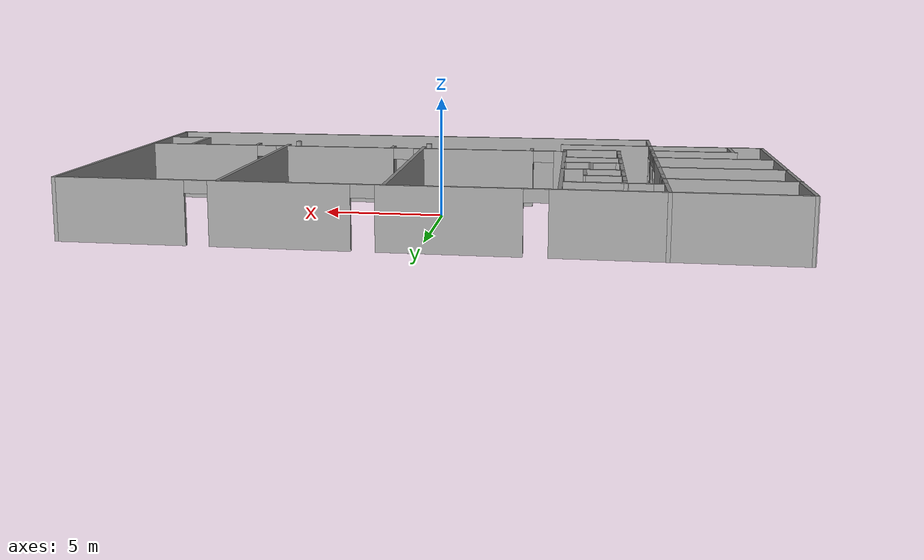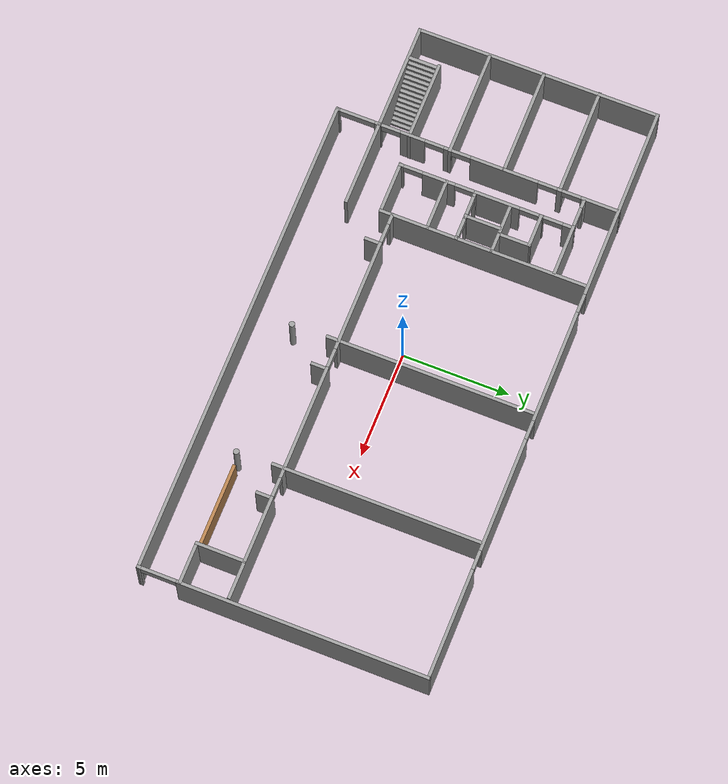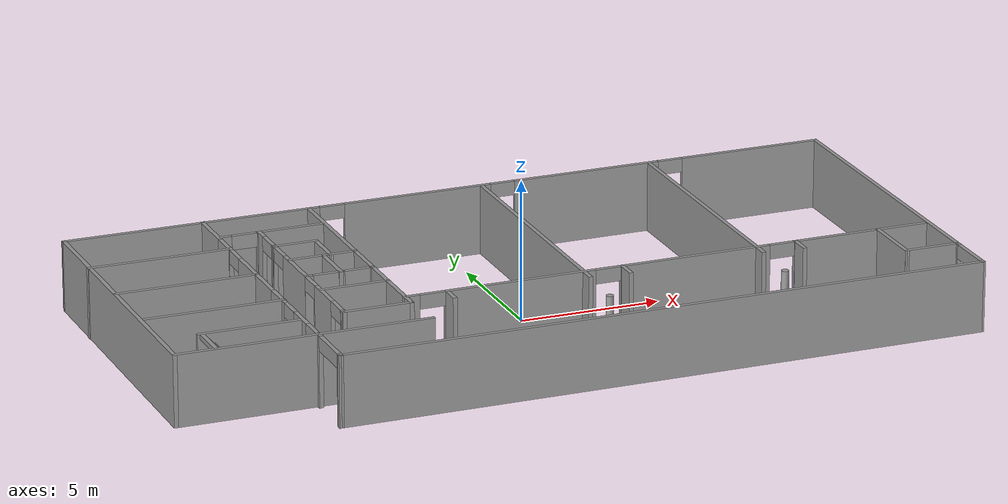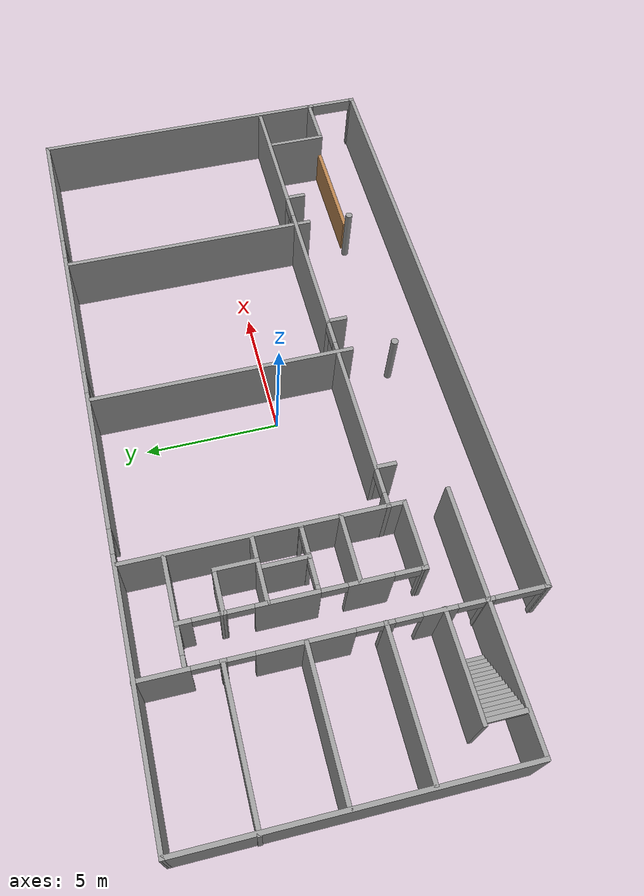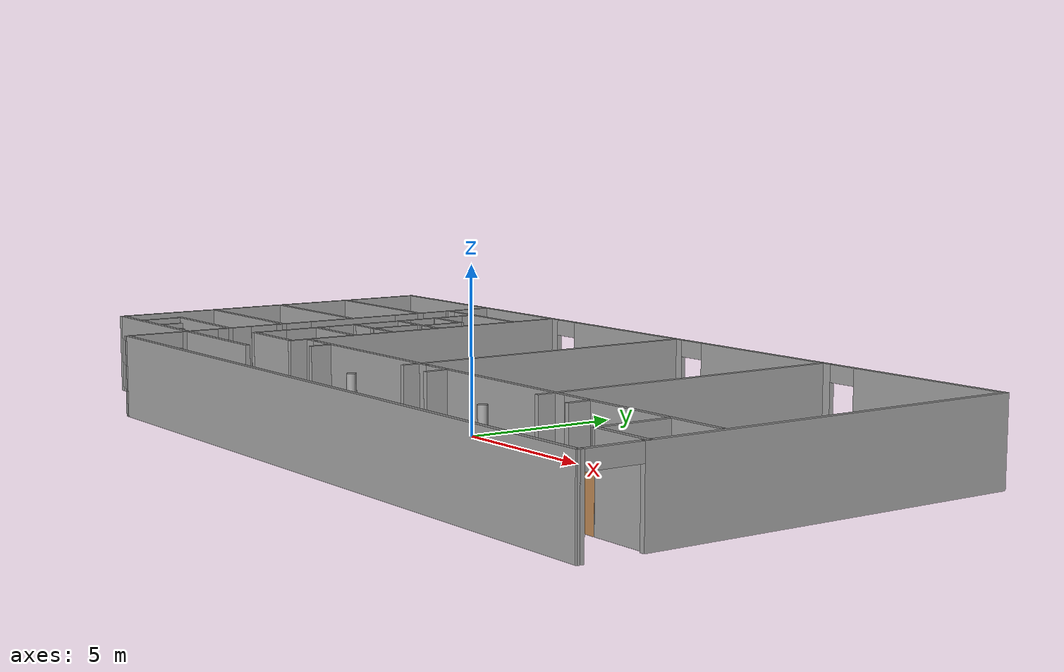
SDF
<?xml version='1.0'?>
<sdf version='1.7'>
  <model name='batimentH'>
    <link name='Stairs_1'>
      <self_collide>0</self_collide>
      <enable_wind>0</enable_wind>
      <kinematic>0</kinematic>
      <pose>0 0 0 0 -0 0</pose>
      <visual name='Stairs_1_Visual_0'>
        <pose>-10.1559 -3.96803 0.083333 0 -0 -1.5708</pose>
        <geometry>
          <box>
            <size>1.32885 0.162742 0.166667</size>
          </box>
        </geometry>
        <material>
          <script>
            <uri>file://media/materials/scripts/gazebo.material</uri>
            <name>Gazebo/Grey</name>
          </script>
          <ambient>1 1 1 1</ambient>
          <shader type='pixel'/>
        </material>
        <meta>
          <layer>0</layer>
        </meta>
        <transparency>0</transparency>
        <cast_shadows>1</cast_shadows>
      </visual>
      <visual name='Stairs_1_Visual_1'>
        <pose>-10.3187 -3.96803 0.25 0 -0 -1.5708</pose>
        <geometry>
          <box>
            <size>1.32885 0.162742 0.166667</size>
          </box>
        </geometry>
        <material>
          <script>
            <uri>file://media/materials/scripts/gazebo.material</uri>
            <name>Gazebo/Grey</name>
          </script>
          <ambient>1 1 1 1</ambient>
          <shader type='pixel'/>
        </material>
        <meta>
          <layer>0</layer>
        </meta>
        <transparency>0</transparency>
        <cast_shadows>1</cast_shadows>
      </visual>
      <visual name='Stairs_1_Visual_2'>
        <pose>-10.4814 -3.96803 0.416667 0 -0 -1.5708</pose>
        <geometry>
          <box>
            <size>1.32885 0.162742 0.166667</size>
          </box>
        </geometry>
        <material>
          <script>
            <uri>file://media/materials/scripts/gazebo.material</uri>
            <name>Gazebo/Grey</name>
          </script>
          <ambient>1 1 1 1</ambient>
          <shader type='pixel'/>
        </material>
        <meta>
          <layer>0</layer>
        </meta>
        <transparency>0</transparency>
        <cast_shadows>1</cast_shadows>
      </visual>
      <visual name='Stairs_1_Visual_3'>
        <pose>-10.6442 -3.96803 0.583333 0 -0 -1.5708</pose>
        <geometry>
          <box>
            <size>1.32885 0.162742 0.166667</size>
          </box>
        </geometry>
        <material>
          <script>
            <uri>file://media/materials/scripts/gazebo.material</uri>
            <name>Gazebo/Grey</name>
          </script>
          <ambient>1 1 1 1</ambient>
          <shader type='pixel'/>
        </material>
        <meta>
          <layer>0</layer>
        </meta>
        <transparency>0</transparency>
        <cast_shadows>1</cast_shadows>
      </visual>
      <visual name='Stairs_1_Visual_4'>
        <pose>-10.8069 -3.96803 0.75 0 -0 -1.5708</pose>
        <geometry>
          <box>
            <size>1.32885 0.162742 0.166667</size>
          </box>
        </geometry>
        <material>
          <script>
            <uri>file://media/materials/scripts/gazebo.material</uri>
            <name>Gazebo/Grey</name>
          </script>
          <ambient>1 1 1 1</ambient>
          <shader type='pixel'/>
        </material>
        <meta>
          <layer>0</layer>
        </meta>
        <transparency>0</transparency>
        <cast_shadows>1</cast_shadows>
      </visual>
      <visual name='Stairs_1_Visual_5'>
        <pose>-10.9697 -3.96803 0.916667 0 -0 -1.5708</pose>
        <geometry>
          <box>
            <size>1.32885 0.162742 0.166667</size>
          </box>
        </geometry>
        <material>
          <script>
            <uri>file://media/materials/scripts/gazebo.material</uri>
            <name>Gazebo/Grey</name>
          </script>
          <ambient>1 1 1 1</ambient>
          <shader type='pixel'/>
        </material>
        <meta>
          <layer>0</layer>
        </meta>
        <transparency>0</transparency>
        <cast_shadows>1</cast_shadows>
      </visual>
      <visual name='Stairs_1_Visual_6'>
        <pose>-11.1324 -3.96803 1.08333 0 -0 -1.5708</pose>
        <geometry>
          <box>
            <size>1.32885 0.162742 0.166667</size>
          </box>
        </geometry>
        <material>
          <script>
            <uri>file://media/materials/scripts/gazebo.material</uri>
            <name>Gazebo/Grey</name>
          </script>
          <ambient>1 1 1 1</ambient>
          <shader type='pixel'/>
        </material>
        <meta>
          <layer>0</layer>
        </meta>
        <transparency>0</transparency>
        <cast_shadows>1</cast_shadows>
      </visual>
      <visual name='Stairs_1_Visual_7'>
        <pose>-11.2951 -3.96803 1.25 0 -0 -1.5708</pose>
        <geometry>
          <box>
            <size>1.32885 0.162742 0.166667</size>
          </box>
        </geometry>
        <material>
          <script>
            <uri>file://media/materials/scripts/gazebo.material</uri>
            <name>Gazebo/Grey</name>
          </script>
          <ambient>1 1 1 1</ambient>
          <shader type='pixel'/>
        </material>
        <meta>
          <layer>0</layer>
        </meta>
        <transparency>0</transparency>
        <cast_shadows>1</cast_shadows>
      </visual>
      <visual name='Stairs_1_Visual_8'>
        <pose>-11.4579 -3.96803 1.41667 0 -0 -1.5708</pose>
        <geometry>
          <box>
            <size>1.32885 0.162742 0.166667</size>
          </box>
        </geometry>
        <material>
          <script>
            <uri>file://media/materials/scripts/gazebo.material</uri>
            <name>Gazebo/Grey</name>
          </script>
          <ambient>1 1 1 1</ambient>
          <shader type='pixel'/>
        </material>
        <meta>
          <layer>0</layer>
        </meta>
        <transparency>0</transparency>
        <cast_shadows>1</cast_shadows>
      </visual>
      <visual name='Stairs_1_Visual_9'>
        <pose>-11.6206 -3.96803 1.58333 0 -0 -1.5708</pose>
        <geometry>
          <box>
            <size>1.32885 0.162742 0.166667</size>
          </box>
        </geometry>
        <material>
          <script>
            <uri>file://media/materials/scripts/gazebo.material</uri>
            <name>Gazebo/Grey</name>
          </script>
          <ambient>1 1 1 1</ambient>
          <shader type='pixel'/>
        </material>
        <meta>
          <layer>0</layer>
        </meta>
        <transparency>0</transparency>
        <cast_shadows>1</cast_shadows>
      </visual>
      <visual name='Stairs_1_Visual_10'>
        <pose>-11.7834 -3.96803 1.75 0 -0 -1.5708</pose>
        <geometry>
          <box>
            <size>1.32885 0.162742 0.166667</size>
          </box>
        </geometry>
        <material>
          <script>
            <uri>file://media/materials/scripts/gazebo.material</uri>
            <name>Gazebo/Grey</name>
          </script>
          <ambient>1 1 1 1</ambient>
          <shader type='pixel'/>
        </material>
        <meta>
          <layer>0</layer>
        </meta>
        <transparency>0</transparency>
        <cast_shadows>1</cast_shadows>
      </visual>
      <visual name='Stairs_1_Visual_11'>
        <pose>-11.9461 -3.96803 1.91667 0 -0 -1.5708</pose>
        <geometry>
          <box>
            <size>1.32885 0.162742 0.166667</size>
          </box>
        </geometry>
        <material>
          <script>
            <uri>file://media/materials/scripts/gazebo.material</uri>
            <name>Gazebo/Grey</name>
          </script>
          <ambient>1 1 1 1</ambient>
          <shader type='pixel'/>
        </material>
        <meta>
          <layer>0</layer>
        </meta>
        <transparency>0</transparency>
        <cast_shadows>1</cast_shadows>
      </visual>
      <visual name='Stairs_1_Visual_12'>
        <pose>-12.1089 -3.96803 2.08333 0 -0 -1.5708</pose>
        <geometry>
          <box>
            <size>1.32885 0.162742 0.166667</size>
          </box>
        </geometry>
        <material>
          <script>
            <uri>file://media/materials/scripts/gazebo.material</uri>
            <name>Gazebo/Grey</name>
          </script>
          <ambient>1 1 1 1</ambient>
          <shader type='pixel'/>
        </material>
        <meta>
          <layer>0</layer>
        </meta>
        <transparency>0</transparency>
        <cast_shadows>1</cast_shadows>
      </visual>
      <visual name='Stairs_1_Visual_13'>
        <pose>-12.2716 -3.96803 2.25 0 -0 -1.5708</pose>
        <geometry>
          <box>
            <size>1.32885 0.162742 0.166667</size>
          </box>
        </geometry>
        <material>
          <script>
            <uri>file://media/materials/scripts/gazebo.material</uri>
            <name>Gazebo/Grey</name>
          </script>
          <ambient>1 1 1 1</ambient>
          <shader type='pixel'/>
        </material>
        <meta>
          <layer>0</layer>
        </meta>
        <transparency>0</transparency>
        <cast_shadows>1</cast_shadows>
      </visual>
      <visual name='Stairs_1_Visual_14'>
        <pose>-12.4343 -3.96803 2.41667 0 -0 -1.5708</pose>
        <geometry>
          <box>
            <size>1.32885 0.162742 0.166667</size>
          </box>
        </geometry>
        <material>
          <script>
            <uri>file://media/materials/scripts/gazebo.material</uri>
            <name>Gazebo/Grey</name>
          </script>
          <ambient>1 1 1 1</ambient>
          <shader type='pixel'/>
        </material>
        <meta>
          <layer>0</layer>
        </meta>
        <transparency>0</transparency>
        <cast_shadows>1</cast_shadows>
      </visual>
      <collision name='Stairs_1_Collision_0'>
        <laser_retro>0</laser_retro>
        <max_contacts>10</max_contacts>
        <pose>-10.1559 -3.96803 0.083333 0 0 -1.5708</pose>
        <geometry>
          <box>
            <size>1.32885 0.162742 0.166667</size>
          </box>
        </geometry>
        <surface>
          <friction>
            <ode>
              <mu>1</mu>
              <mu2>1</mu2>
              <fdir1>0 0 0</fdir1>
              <slip1>0</slip1>
              <slip2>0</slip2>
            </ode>
            <torsional>
              <coefficient>1</coefficient>
              <patch_radius>0</patch_radius>
              <surface_radius>0</surface_radius>
              <use_patch_radius>1</use_patch_radius>
              <ode>
                <slip>0</slip>
              </ode>
            </torsional>
          </friction>
          <bounce>
            <restitution_coefficient>0</restitution_coefficient>
            <threshold>1e+06</threshold>
          </bounce>
          <contact>
            <collide_without_contact>0</collide_without_contact>
            <collide_without_contact_bitmask>1</collide_without_contact_bitmask>
            <collide_bitmask>1</collide_bitmask>
            <ode>
              <soft_cfm>0</soft_cfm>
              <soft_erp>0.2</soft_erp>
              <kp>1e+13</kp>
              <kd>1</kd>
              <max_vel>0.01</max_vel>
              <min_depth>0</min_depth>
            </ode>
            <bullet>
              <split_impulse>1</split_impulse>
              <split_impulse_penetration_threshold>-0.01</split_impulse_penetration_threshold>
              <soft_cfm>0</soft_cfm>
              <soft_erp>0.2</soft_erp>
              <kp>1e+13</kp>
              <kd>1</kd>
            </bullet>
          </contact>
        </surface>
      </collision>
      <collision name='Stairs_1_Collision_1'>
        <laser_retro>0</laser_retro>
        <max_contacts>10</max_contacts>
        <pose>-10.3187 -3.96803 0.25 0 0 -1.5708</pose>
        <geometry>
          <box>
            <size>1.32885 0.162742 0.166667</size>
          </box>
        </geometry>
        <surface>
          <friction>
            <ode>
              <mu>1</mu>
              <mu2>1</mu2>
              <fdir1>0 0 0</fdir1>
              <slip1>0</slip1>
              <slip2>0</slip2>
            </ode>
            <torsional>
              <coefficient>1</coefficient>
              <patch_radius>0</patch_radius>
              <surface_radius>0</surface_radius>
              <use_patch_radius>1</use_patch_radius>
              <ode>
                <slip>0</slip>
              </ode>
            </torsional>
          </friction>
          <bounce>
            <restitution_coefficient>0</restitution_coefficient>
            <threshold>1e+06</threshold>
          </bounce>
          <contact>
            <collide_without_contact>0</collide_without_contact>
            <collide_without_contact_bitmask>1</collide_without_contact_bitmask>
            <collide_bitmask>1</collide_bitmask>
            <ode>
              <soft_cfm>0</soft_cfm>
              <soft_erp>0.2</soft_erp>
              <kp>1e+13</kp>
              <kd>1</kd>
              <max_vel>0.01</max_vel>
              <min_depth>0</min_depth>
            </ode>
            <bullet>
              <split_impulse>1</split_impulse>
              <split_impulse_penetration_threshold>-0.01</split_impulse_penetration_threshold>
              <soft_cfm>0</soft_cfm>
              <soft_erp>0.2</soft_erp>
              <kp>1e+13</kp>
              <kd>1</kd>
            </bullet>
          </contact>
        </surface>
      </collision>
      <collision name='Stairs_1_Collision_2'>
        <laser_retro>0</laser_retro>
        <max_contacts>10</max_contacts>
        <pose>-10.4814 -3.96803 0.416667 0 0 -1.5708</pose>
        <geometry>
          <box>
            <size>1.32885 0.162742 0.166667</size>
          </box>
        </geometry>
        <surface>
          <friction>
            <ode>
              <mu>1</mu>
              <mu2>1</mu2>
              <fdir1>0 0 0</fdir1>
              <slip1>0</slip1>
              <slip2>0</slip2>
            </ode>
            <torsional>
              <coefficient>1</coefficient>
              <patch_radius>0</patch_radius>
              <surface_radius>0</surface_radius>
              <use_patch_radius>1</use_patch_radius>
              <ode>
                <slip>0</slip>
              </ode>
            </torsional>
          </friction>
          <bounce>
            <restitution_coefficient>0</restitution_coefficient>
            <threshold>1e+06</threshold>
          </bounce>
          <contact>
            <collide_without_contact>0</collide_without_contact>
            <collide_without_contact_bitmask>1</collide_without_contact_bitmask>
            <collide_bitmask>1</collide_bitmask>
            <ode>
              <soft_cfm>0</soft_cfm>
              <soft_erp>0.2</soft_erp>
              <kp>1e+13</kp>
              <kd>1</kd>
              <max_vel>0.01</max_vel>
              <min_depth>0</min_depth>
            </ode>
            <bullet>
              <split_impulse>1</split_impulse>
              <split_impulse_penetration_threshold>-0.01</split_impulse_penetration_threshold>
              <soft_cfm>0</soft_cfm>
              <soft_erp>0.2</soft_erp>
              <kp>1e+13</kp>
              <kd>1</kd>
            </bullet>
          </contact>
        </surface>
      </collision>
      <collision name='Stairs_1_Collision_3'>
        <laser_retro>0</laser_retro>
        <max_contacts>10</max_contacts>
        <pose>-10.6442 -3.96803 0.583333 0 0 -1.5708</pose>
        <geometry>
          <box>
            <size>1.32885 0.162742 0.166667</size>
          </box>
        </geometry>
        <surface>
          <friction>
            <ode>
              <mu>1</mu>
              <mu2>1</mu2>
              <fdir1>0 0 0</fdir1>
              <slip1>0</slip1>
              <slip2>0</slip2>
            </ode>
            <torsional>
              <coefficient>1</coefficient>
              <patch_radius>0</patch_radius>
              <surface_radius>0</surface_radius>
              <use_patch_radius>1</use_patch_radius>
              <ode>
                <slip>0</slip>
              </ode>
            </torsional>
          </friction>
          <bounce>
            <restitution_coefficient>0</restitution_coefficient>
            <threshold>1e+06</threshold>
          </bounce>
          <contact>
            <collide_without_contact>0</collide_without_contact>
            <collide_without_contact_bitmask>1</collide_without_contact_bitmask>
            <collide_bitmask>1</collide_bitmask>
            <ode>
              <soft_cfm>0</soft_cfm>
              <soft_erp>0.2</soft_erp>
              <kp>1e+13</kp>
              <kd>1</kd>
              <max_vel>0.01</max_vel>
              <min_depth>0</min_depth>
            </ode>
            <bullet>
              <split_impulse>1</split_impulse>
              <split_impulse_penetration_threshold>-0.01</split_impulse_penetration_threshold>
              <soft_cfm>0</soft_cfm>
              <soft_erp>0.2</soft_erp>
              <kp>1e+13</kp>
              <kd>1</kd>
            </bullet>
          </contact>
        </surface>
      </collision>
      <collision name='Stairs_1_Collision_4'>
        <laser_retro>0</laser_retro>
        <max_contacts>10</max_contacts>
        <pose>-10.8069 -3.96803 0.75 0 0 -1.5708</pose>
        <geometry>
          <box>
            <size>1.32885 0.162742 0.166667</size>
          </box>
        </geometry>
        <surface>
          <friction>
            <ode>
              <mu>1</mu>
              <mu2>1</mu2>
              <fdir1>0 0 0</fdir1>
              <slip1>0</slip1>
              <slip2>0</slip2>
            </ode>
            <torsional>
              <coefficient>1</coefficient>
              <patch_radius>0</patch_radius>
              <surface_radius>0</surface_radius>
              <use_patch_radius>1</use_patch_radius>
              <ode>
                <slip>0</slip>
              </ode>
            </torsional>
          </friction>
          <bounce>
            <restitution_coefficient>0</restitution_coefficient>
            <threshold>1e+06</threshold>
          </bounce>
          <contact>
            <collide_without_contact>0</collide_without_contact>
            <collide_without_contact_bitmask>1</collide_without_contact_bitmask>
            <collide_bitmask>1</collide_bitmask>
            <ode>
              <soft_cfm>0</soft_cfm>
              <soft_erp>0.2</soft_erp>
              <kp>1e+13</kp>
              <kd>1</kd>
              <max_vel>0.01</max_vel>
              <min_depth>0</min_depth>
            </ode>
            <bullet>
              <split_impulse>1</split_impulse>
              <split_impulse_penetration_threshold>-0.01</split_impulse_penetration_threshold>
              <soft_cfm>0</soft_cfm>
              <soft_erp>0.2</soft_erp>
              <kp>1e+13</kp>
              <kd>1</kd>
            </bullet>
          </contact>
        </surface>
      </collision>
      <collision name='Stairs_1_Collision_5'>
        <laser_retro>0</laser_retro>
        <max_contacts>10</max_contacts>
        <pose>-10.9697 -3.96803 0.916667 0 0 -1.5708</pose>
        <geometry>
          <box>
            <size>1.32885 0.162742 0.166667</size>
          </box>
        </geometry>
        <surface>
          <friction>
            <ode>
              <mu>1</mu>
              <mu2>1</mu2>
              <fdir1>0 0 0</fdir1>
              <slip1>0</slip1>
              <slip2>0</slip2>
            </ode>
            <torsional>
              <coefficient>1</coefficient>
              <patch_radius>0</patch_radius>
              <surface_radius>0</surface_radius>
              <use_patch_radius>1</use_patch_radius>
              <ode>
                <slip>0</slip>
              </ode>
            </torsional>
          </friction>
          <bounce>
            <restitution_coefficient>0</restitution_coefficient>
            <threshold>1e+06</threshold>
          </bounce>
          <contact>
            <collide_without_contact>0</collide_without_contact>
            <collide_without_contact_bitmask>1</collide_without_contact_bitmask>
            <collide_bitmask>1</collide_bitmask>
            <ode>
              <soft_cfm>0</soft_cfm>
              <soft_erp>0.2</soft_erp>
              <kp>1e+13</kp>
              <kd>1</kd>
              <max_vel>0.01</max_vel>
              <min_depth>0</min_depth>
            </ode>
            <bullet>
              <split_impulse>1</split_impulse>
              <split_impulse_penetration_threshold>-0.01</split_impulse_penetration_threshold>
              <soft_cfm>0</soft_cfm>
              <soft_erp>0.2</soft_erp>
              <kp>1e+13</kp>
              <kd>1</kd>
            </bullet>
          </contact>
        </surface>
      </collision>
      <collision name='Stairs_1_Collision_6'>
        <laser_retro>0</laser_retro>
        <max_contacts>10</max_contacts>
        <pose>-11.1324 -3.96803 1.08333 0 0 -1.5708</pose>
        <geometry>
          <box>
            <size>1.32885 0.162742 0.166667</size>
          </box>
        </geometry>
        <surface>
          <friction>
            <ode>
              <mu>1</mu>
              <mu2>1</mu2>
              <fdir1>0 0 0</fdir1>
              <slip1>0</slip1>
              <slip2>0</slip2>
            </ode>
            <torsional>
              <coefficient>1</coefficient>
              <patch_radius>0</patch_radius>
              <surface_radius>0</surface_radius>
              <use_patch_radius>1</use_patch_radius>
              <ode>
                <slip>0</slip>
              </ode>
            </torsional>
          </friction>
          <bounce>
            <restitution_coefficient>0</restitution_coefficient>
            <threshold>1e+06</threshold>
          </bounce>
          <contact>
            <collide_without_contact>0</collide_without_contact>
            <collide_without_contact_bitmask>1</collide_without_contact_bitmask>
            <collide_bitmask>1</collide_bitmask>
            <ode>
              <soft_cfm>0</soft_cfm>
              <soft_erp>0.2</soft_erp>
              <kp>1e+13</kp>
              <kd>1</kd>
              <max_vel>0.01</max_vel>
              <min_depth>0</min_depth>
            </ode>
            <bullet>
              <split_impulse>1</split_impulse>
              <split_impulse_penetration_threshold>-0.01</split_impulse_penetration_threshold>
              <soft_cfm>0</soft_cfm>
              <soft_erp>0.2</soft_erp>
              <kp>1e+13</kp>
              <kd>1</kd>
            </bullet>
          </contact>
        </surface>
      </collision>
      <collision name='Stairs_1_Collision_7'>
        <laser_retro>0</laser_retro>
        <max_contacts>10</max_contacts>
        <pose>-11.2951 -3.96803 1.25 0 0 -1.5708</pose>
        <geometry>
          <box>
            <size>1.32885 0.162742 0.166667</size>
          </box>
        </geometry>
        <surface>
          <friction>
            <ode>
              <mu>1</mu>
              <mu2>1</mu2>
              <fdir1>0 0 0</fdir1>
              <slip1>0</slip1>
              <slip2>0</slip2>
            </ode>
            <torsional>
              <coefficient>1</coefficient>
              <patch_radius>0</patch_radius>
              <surface_radius>0</surface_radius>
              <use_patch_radius>1</use_patch_radius>
              <ode>
                <slip>0</slip>
              </ode>
            </torsional>
          </friction>
          <bounce>
            <restitution_coefficient>0</restitution_coefficient>
            <threshold>1e+06</threshold>
          </bounce>
          <contact>
            <collide_without_contact>0</collide_without_contact>
            <collide_without_contact_bitmask>1</collide_without_contact_bitmask>
            <collide_bitmask>1</collide_bitmask>
            <ode>
              <soft_cfm>0</soft_cfm>
              <soft_erp>0.2</soft_erp>
              <kp>1e+13</kp>
              <kd>1</kd>
              <max_vel>0.01</max_vel>
              <min_depth>0</min_depth>
            </ode>
            <bullet>
              <split_impulse>1</split_impulse>
              <split_impulse_penetration_threshold>-0.01</split_impulse_penetration_threshold>
              <soft_cfm>0</soft_cfm>
              <soft_erp>0.2</soft_erp>
              <kp>1e+13</kp>
              <kd>1</kd>
            </bullet>
          </contact>
        </surface>
      </collision>
      <collision name='Stairs_1_Collision_8'>
        <laser_retro>0</laser_retro>
        <max_contacts>10</max_contacts>
        <pose>-11.4579 -3.96803 1.41667 0 0 -1.5708</pose>
        <geometry>
          <box>
            <size>1.32885 0.162742 0.166667</size>
          </box>
        </geometry>
        <surface>
          <friction>
            <ode>
              <mu>1</mu>
              <mu2>1</mu2>
              <fdir1>0 0 0</fdir1>
              <slip1>0</slip1>
              <slip2>0</slip2>
            </ode>
            <torsional>
              <coefficient>1</coefficient>
              <patch_radius>0</patch_radius>
              <surface_radius>0</surface_radius>
              <use_patch_radius>1</use_patch_radius>
              <ode>
                <slip>0</slip>
              </ode>
            </torsional>
          </friction>
          <bounce>
            <restitution_coefficient>0</restitution_coefficient>
            <threshold>1e+06</threshold>
          </bounce>
          <contact>
            <collide_without_contact>0</collide_without_contact>
            <collide_without_contact_bitmask>1</collide_without_contact_bitmask>
            <collide_bitmask>1</collide_bitmask>
            <ode>
              <soft_cfm>0</soft_cfm>
              <soft_erp>0.2</soft_erp>
              <kp>1e+13</kp>
              <kd>1</kd>
              <max_vel>0.01</max_vel>
              <min_depth>0</min_depth>
            </ode>
            <bullet>
              <split_impulse>1</split_impulse>
              <split_impulse_penetration_threshold>-0.01</split_impulse_penetration_threshold>
              <soft_cfm>0</soft_cfm>
              <soft_erp>0.2</soft_erp>
              <kp>1e+13</kp>
              <kd>1</kd>
            </bullet>
          </contact>
        </surface>
      </collision>
      <collision name='Stairs_1_Collision_10'>
        <laser_retro>0</laser_retro>
        <max_contacts>10</max_contacts>
        <pose>-11.7834 -3.96803 1.75 0 0 -1.5708</pose>
        <geometry>
          <box>
            <size>1.32885 0.162742 0.166667</size>
          </box>
        </geometry>
        <surface>
          <friction>
            <ode>
              <mu>1</mu>
              <mu2>1</mu2>
              <fdir1>0 0 0</fdir1>
              <slip1>0</slip1>
              <slip2>0</slip2>
            </ode>
            <torsional>
              <coefficient>1</coefficient>
              <patch_radius>0</patch_radius>
              <surface_radius>0</surface_radius>
              <use_patch_radius>1</use_patch_radius>
              <ode>
                <slip>0</slip>
              </ode>
            </torsional>
          </friction>
          <bounce>
            <restitution_coefficient>0</restitution_coefficient>
            <threshold>1e+06</threshold>
          </bounce>
          <contact>
            <collide_without_contact>0</collide_without_contact>
            <collide_without_contact_bitmask>1</collide_without_contact_bitmask>
            <collide_bitmask>1</collide_bitmask>
            <ode>
              <soft_cfm>0</soft_cfm>
              <soft_erp>0.2</soft_erp>
              <kp>1e+13</kp>
              <kd>1</kd>
              <max_vel>0.01</max_vel>
              <min_depth>0</min_depth>
            </ode>
            <bullet>
              <split_impulse>1</split_impulse>
              <split_impulse_penetration_threshold>-0.01</split_impulse_penetration_threshold>
              <soft_cfm>0</soft_cfm>
              <soft_erp>0.2</soft_erp>
              <kp>1e+13</kp>
              <kd>1</kd>
            </bullet>
          </contact>
        </surface>
      </collision>
      <collision name='Stairs_1_Collision_9'>
        <laser_retro>0</laser_retro>
        <max_contacts>10</max_contacts>
        <pose>-11.6206 -3.96803 1.58333 0 0 -1.5708</pose>
        <geometry>
          <box>
            <size>1.32885 0.162742 0.166667</size>
          </box>
        </geometry>
        <surface>
          <friction>
            <ode>
              <mu>1</mu>
              <mu2>1</mu2>
              <fdir1>0 0 0</fdir1>
              <slip1>0</slip1>
              <slip2>0</slip2>
            </ode>
            <torsional>
              <coefficient>1</coefficient>
              <patch_radius>0</patch_radius>
              <surface_radius>0</surface_radius>
              <use_patch_radius>1</use_patch_radius>
              <ode>
                <slip>0</slip>
              </ode>
            </torsional>
          </friction>
          <bounce>
            <restitution_coefficient>0</restitution_coefficient>
            <threshold>1e+06</threshold>
          </bounce>
          <contact>
            <collide_without_contact>0</collide_without_contact>
            <collide_without_contact_bitmask>1</collide_without_contact_bitmask>
            <collide_bitmask>1</collide_bitmask>
            <ode>
              <soft_cfm>0</soft_cfm>
              <soft_erp>0.2</soft_erp>
              <kp>1e+13</kp>
              <kd>1</kd>
              <max_vel>0.01</max_vel>
              <min_depth>0</min_depth>
            </ode>
            <bullet>
              <split_impulse>1</split_impulse>
              <split_impulse_penetration_threshold>-0.01</split_impulse_penetration_threshold>
              <soft_cfm>0</soft_cfm>
              <soft_erp>0.2</soft_erp>
              <kp>1e+13</kp>
              <kd>1</kd>
            </bullet>
          </contact>
        </surface>
      </collision>
      <collision name='Stairs_1_Collision_11'>
        <laser_retro>0</laser_retro>
        <max_contacts>10</max_contacts>
        <pose>-11.9461 -3.96803 1.91667 0 0 -1.5708</pose>
        <geometry>
          <box>
            <size>1.32885 0.162742 0.166667</size>
          </box>
        </geometry>
        <surface>
          <friction>
            <ode>
              <mu>1</mu>
              <mu2>1</mu2>
              <fdir1>0 0 0</fdir1>
              <slip1>0</slip1>
              <slip2>0</slip2>
            </ode>
            <torsional>
              <coefficient>1</coefficient>
              <patch_radius>0</patch_radius>
              <surface_radius>0</surface_radius>
              <use_patch_radius>1</use_patch_radius>
              <ode>
                <slip>0</slip>
              </ode>
            </torsional>
          </friction>
          <bounce>
            <restitution_coefficient>0</restitution_coefficient>
            <threshold>1e+06</threshold>
          </bounce>
          <contact>
            <collide_without_contact>0</collide_without_contact>
            <collide_without_contact_bitmask>1</collide_without_contact_bitmask>
            <collide_bitmask>1</collide_bitmask>
            <ode>
              <soft_cfm>0</soft_cfm>
              <soft_erp>0.2</soft_erp>
              <kp>1e+13</kp>
              <kd>1</kd>
              <max_vel>0.01</max_vel>
              <min_depth>0</min_depth>
            </ode>
            <bullet>
              <split_impulse>1</split_impulse>
              <split_impulse_penetration_threshold>-0.01</split_impulse_penetration_threshold>
              <soft_cfm>0</soft_cfm>
              <soft_erp>0.2</soft_erp>
              <kp>1e+13</kp>
              <kd>1</kd>
            </bullet>
          </contact>
        </surface>
      </collision>
      <collision name='Stairs_1_Collision_12'>
        <laser_retro>0</laser_retro>
        <max_contacts>10</max_contacts>
        <pose>-12.1089 -3.96803 2.08333 0 0 -1.5708</pose>
        <geometry>
          <box>
            <size>1.32885 0.162742 0.166667</size>
          </box>
        </geometry>
        <surface>
          <friction>
            <ode>
              <mu>1</mu>
              <mu2>1</mu2>
              <fdir1>0 0 0</fdir1>
              <slip1>0</slip1>
              <slip2>0</slip2>
            </ode>
            <torsional>
              <coefficient>1</coefficient>
              <patch_radius>0</patch_radius>
              <surface_radius>0</surface_radius>
              <use_patch_radius>1</use_patch_radius>
              <ode>
                <slip>0</slip>
              </ode>
            </torsional>
          </friction>
          <bounce>
            <restitution_coefficient>0</restitution_coefficient>
            <threshold>1e+06</threshold>
          </bounce>
          <contact>
            <collide_without_contact>0</collide_without_contact>
            <collide_without_contact_bitmask>1</collide_without_contact_bitmask>
            <collide_bitmask>1</collide_bitmask>
            <ode>
              <soft_cfm>0</soft_cfm>
              <soft_erp>0.2</soft_erp>
              <kp>1e+13</kp>
              <kd>1</kd>
              <max_vel>0.01</max_vel>
              <min_depth>0</min_depth>
            </ode>
            <bullet>
              <split_impulse>1</split_impulse>
              <split_impulse_penetration_threshold>-0.01</split_impulse_penetration_threshold>
              <soft_cfm>0</soft_cfm>
              <soft_erp>0.2</soft_erp>
              <kp>1e+13</kp>
              <kd>1</kd>
            </bullet>
          </contact>
        </surface>
      </collision>
      <collision name='Stairs_1_Collision_13'>
        <laser_retro>0</laser_retro>
        <max_contacts>10</max_contacts>
        <pose>-12.2716 -3.96803 2.25 0 0 -1.5708</pose>
        <geometry>
          <box>
            <size>1.32885 0.162742 0.166667</size>
          </box>
        </geometry>
        <surface>
          <friction>
            <ode>
              <mu>1</mu>
              <mu2>1</mu2>
              <fdir1>0 0 0</fdir1>
              <slip1>0</slip1>
              <slip2>0</slip2>
            </ode>
            <torsional>
              <coefficient>1</coefficient>
              <patch_radius>0</patch_radius>
              <surface_radius>0</surface_radius>
              <use_patch_radius>1</use_patch_radius>
              <ode>
                <slip>0</slip>
              </ode>
            </torsional>
          </friction>
          <bounce>
            <restitution_coefficient>0</restitution_coefficient>
            <threshold>1e+06</threshold>
          </bounce>
          <contact>
            <collide_without_contact>0</collide_without_contact>
            <collide_without_contact_bitmask>1</collide_without_contact_bitmask>
            <collide_bitmask>1</collide_bitmask>
            <ode>
              <soft_cfm>0</soft_cfm>
              <soft_erp>0.2</soft_erp>
              <kp>1e+13</kp>
              <kd>1</kd>
              <max_vel>0.01</max_vel>
              <min_depth>0</min_depth>
            </ode>
            <bullet>
              <split_impulse>1</split_impulse>
              <split_impulse_penetration_threshold>-0.01</split_impulse_penetration_threshold>
              <soft_cfm>0</soft_cfm>
              <soft_erp>0.2</soft_erp>
              <kp>1e+13</kp>
              <kd>1</kd>
            </bullet>
          </contact>
        </surface>
      </collision>
      <collision name='Stairs_1_Collision_14'>
        <laser_retro>0</laser_retro>
        <max_contacts>10</max_contacts>
        <pose>-12.4343 -3.96803 2.41667 0 0 -1.5708</pose>
        <geometry>
          <box>
            <size>1.32885 0.162742 0.166667</size>
          </box>
        </geometry>
        <surface>
          <friction>
            <ode>
              <mu>1</mu>
              <mu2>1</mu2>
              <fdir1>0 0 0</fdir1>
              <slip1>0</slip1>
              <slip2>0</slip2>
            </ode>
            <torsional>
              <coefficient>1</coefficient>
              <patch_radius>0</patch_radius>
              <surface_radius>0</surface_radius>
              <use_patch_radius>1</use_patch_radius>
              <ode>
                <slip>0</slip>
              </ode>
            </torsional>
          </friction>
          <bounce>
            <restitution_coefficient>0</restitution_coefficient>
            <threshold>1e+06</threshold>
          </bounce>
          <contact>
            <collide_without_contact>0</collide_without_contact>
            <collide_without_contact_bitmask>1</collide_without_contact_bitmask>
            <collide_bitmask>1</collide_bitmask>
            <ode>
              <soft_cfm>0</soft_cfm>
              <soft_erp>0.2</soft_erp>
              <kp>1e+13</kp>
              <kd>1</kd>
              <max_vel>0.01</max_vel>
              <min_depth>0</min_depth>
            </ode>
            <bullet>
              <split_impulse>1</split_impulse>
              <split_impulse_penetration_threshold>-0.01</split_impulse_penetration_threshold>
              <soft_cfm>0</soft_cfm>
              <soft_erp>0.2</soft_erp>
              <kp>1e+13</kp>
              <kd>1</kd>
            </bullet>
          </contact>
        </surface>
      </collision>
    </link>
    <link name='Wall_0'>
      <pose>0.006105 6.66605 0 0 -0 3.1407</pose>
      <self_collide>0</self_collide>
      <enable_wind>0</enable_wind>
      <kinematic>0</kinematic>
      <visual name='Wall_0_Visual_0'>
        <pose>-11.3504 0 1.25 0 -0 0</pose>
        <geometry>
          <box>
            <size>5.217 0.15 2.5</size>
          </box>
        </geometry>
        <material>
          <script>
            <uri>file://media/materials/scripts/gazebo.material</uri>
            <name>Gazebo/Grey</name>
          </script>
          <ambient>1 1 1 1</ambient>
          <shader type='pixel'/>
        </material>
        <meta>
          <layer>0</layer>
        </meta>
        <transparency>0</transparency>
        <cast_shadows>1</cast_shadows>
      </visual>
      <visual name='Wall_0_Visual_1'>
        <pose>-5.13636 0 1.25 0 -0 0</pose>
        <geometry>
          <box>
            <size>5.41105 0.15 2.5</size>
          </box>
        </geometry>
        <material>
          <script>
            <uri>file://media/materials/scripts/gazebo.material</uri>
            <name>Gazebo/Grey</name>
          </script>
          <ambient>1 1 1 1</ambient>
          <shader type='pixel'/>
        </material>
        <meta>
          <layer>0</layer>
        </meta>
        <transparency>0</transparency>
        <cast_shadows>1</cast_shadows>
      </visual>
      <visual name='Wall_0_Visual_2'>
        <pose>1.1607 0 1.25 0 -0 0</pose>
        <geometry>
          <box>
            <size>5.38305 0.15 2.5</size>
          </box>
        </geometry>
        <material>
          <script>
            <uri>file://media/materials/scripts/gazebo.material</uri>
            <name>Gazebo/Grey</name>
          </script>
          <ambient>1 1 1 1</ambient>
          <shader type='pixel'/>
        </material>
        <meta>
          <layer>0</layer>
        </meta>
        <transparency>0</transparency>
        <cast_shadows>1</cast_shadows>
      </visual>
      <visual name='Wall_0_Visual_3'>
        <pose>9.35555 0 1.25 0 -0 0</pose>
        <geometry>
          <box>
            <size>9.20665 0.15 2.5</size>
          </box>
        </geometry>
        <material>
          <script>
            <uri>file://media/materials/scripts/gazebo.material</uri>
            <name>Gazebo/Grey</name>
          </script>
          <ambient>1 1 1 1</ambient>
          <shader type='pixel'/>
        </material>
        <meta>
          <layer>0</layer>
        </meta>
        <transparency>0</transparency>
        <cast_shadows>1</cast_shadows>
      </visual>
      <visual name='Wall_0_Visual_4'>
        <pose>-8.29188 0 2.25 0 -0 0</pose>
        <geometry>
          <box>
            <size>0.9 0.15 0.5</size>
          </box>
        </geometry>
        <material>
          <script>
            <uri>file://media/materials/scripts/gazebo.material</uri>
            <name>Gazebo/Grey</name>
          </script>
          <ambient>1 1 1 1</ambient>
          <shader type='pixel'/>
        </material>
        <meta>
          <layer>0</layer>
        </meta>
        <transparency>0</transparency>
        <cast_shadows>1</cast_shadows>
      </visual>
      <visual name='Wall_0_Visual_5'>
        <pose>-1.98083 0 2.25 0 -0 0</pose>
        <geometry>
          <box>
            <size>0.9 0.15 0.5</size>
          </box>
        </geometry>
        <material>
          <script>
            <uri>file://media/materials/scripts/gazebo.material</uri>
            <name>Gazebo/Grey</name>
          </script>
          <ambient>1 1 1 1</ambient>
          <shader type='pixel'/>
        </material>
        <meta>
          <layer>0</layer>
        </meta>
        <transparency>0</transparency>
        <cast_shadows>1</cast_shadows>
      </visual>
      <visual name='Wall_0_Visual_6'>
        <pose>4.30223 0 2.25 0 -0 0</pose>
        <geometry>
          <box>
            <size>0.9 0.15 0.5</size>
          </box>
        </geometry>
        <material>
          <script>
            <uri>file://media/materials/scripts/gazebo.material</uri>
            <name>Gazebo/Grey</name>
          </script>
          <ambient>1 1 1 1</ambient>
          <shader type='pixel'/>
        </material>
        <meta>
          <layer>0</layer>
        </meta>
        <transparency>0</transparency>
        <cast_shadows>1</cast_shadows>
      </visual>
      <collision name='Wall_0_Collision_0'>
        <laser_retro>0</laser_retro>
        <max_contacts>10</max_contacts>
        <pose>-11.3504 0 1.25 0 -0 0</pose>
        <geometry>
          <box>
            <size>5.217 0.15 2.5</size>
          </box>
        </geometry>
        <surface>
          <friction>
            <ode>
              <mu>1</mu>
              <mu2>1</mu2>
              <fdir1>0 0 0</fdir1>
              <slip1>0</slip1>
              <slip2>0</slip2>
            </ode>
            <torsional>
              <coefficient>1</coefficient>
              <patch_radius>0</patch_radius>
              <surface_radius>0</surface_radius>
              <use_patch_radius>1</use_patch_radius>
              <ode>
                <slip>0</slip>
              </ode>
            </torsional>
          </friction>
          <bounce>
            <restitution_coefficient>0</restitution_coefficient>
            <threshold>1e+06</threshold>
          </bounce>
          <contact>
            <collide_without_contact>0</collide_without_contact>
            <collide_without_contact_bitmask>1</collide_without_contact_bitmask>
            <collide_bitmask>1</collide_bitmask>
            <ode>
              <soft_cfm>0</soft_cfm>
              <soft_erp>0.2</soft_erp>
              <kp>1e+13</kp>
              <kd>1</kd>
              <max_vel>0.01</max_vel>
              <min_depth>0</min_depth>
            </ode>
            <bullet>
              <split_impulse>1</split_impulse>
              <split_impulse_penetration_threshold>-0.01</split_impulse_penetration_threshold>
              <soft_cfm>0</soft_cfm>
              <soft_erp>0.2</soft_erp>
              <kp>1e+13</kp>
              <kd>1</kd>
            </bullet>
          </contact>
        </surface>
      </collision>
      <collision name='Wall_0_Collision_1'>
        <laser_retro>0</laser_retro>
        <max_contacts>10</max_contacts>
        <pose>-5.13636 0 1.25 0 -0 0</pose>
        <geometry>
          <box>
            <size>5.41105 0.15 2.5</size>
          </box>
        </geometry>
        <surface>
          <friction>
            <ode>
              <mu>1</mu>
              <mu2>1</mu2>
              <fdir1>0 0 0</fdir1>
              <slip1>0</slip1>
              <slip2>0</slip2>
            </ode>
            <torsional>
              <coefficient>1</coefficient>
              <patch_radius>0</patch_radius>
              <surface_radius>0</surface_radius>
              <use_patch_radius>1</use_patch_radius>
              <ode>
                <slip>0</slip>
              </ode>
            </torsional>
          </friction>
          <bounce>
            <restitution_coefficient>0</restitution_coefficient>
            <threshold>1e+06</threshold>
          </bounce>
          <contact>
            <collide_without_contact>0</collide_without_contact>
            <collide_without_contact_bitmask>1</collide_without_contact_bitmask>
            <collide_bitmask>1</collide_bitmask>
            <ode>
              <soft_cfm>0</soft_cfm>
              <soft_erp>0.2</soft_erp>
              <kp>1e+13</kp>
              <kd>1</kd>
              <max_vel>0.01</max_vel>
              <min_depth>0</min_depth>
            </ode>
            <bullet>
              <split_impulse>1</split_impulse>
              <split_impulse_penetration_threshold>-0.01</split_impulse_penetration_threshold>
              <soft_cfm>0</soft_cfm>
              <soft_erp>0.2</soft_erp>
              <kp>1e+13</kp>
              <kd>1</kd>
            </bullet>
          </contact>
        </surface>
      </collision>
      <collision name='Wall_0_Collision_2'>
        <laser_retro>0</laser_retro>
        <max_contacts>10</max_contacts>
        <pose>1.1607 0 1.25 0 -0 0</pose>
        <geometry>
          <box>
            <size>5.38305 0.15 2.5</size>
          </box>
        </geometry>
        <surface>
          <friction>
            <ode>
              <mu>1</mu>
              <mu2>1</mu2>
              <fdir1>0 0 0</fdir1>
              <slip1>0</slip1>
              <slip2>0</slip2>
            </ode>
            <torsional>
              <coefficient>1</coefficient>
              <patch_radius>0</patch_radius>
              <surface_radius>0</surface_radius>
              <use_patch_radius>1</use_patch_radius>
              <ode>
                <slip>0</slip>
              </ode>
            </torsional>
          </friction>
          <bounce>
            <restitution_coefficient>0</restitution_coefficient>
            <threshold>1e+06</threshold>
          </bounce>
          <contact>
            <collide_without_contact>0</collide_without_contact>
            <collide_without_contact_bitmask>1</collide_without_contact_bitmask>
            <collide_bitmask>1</collide_bitmask>
            <ode>
              <soft_cfm>0</soft_cfm>
              <soft_erp>0.2</soft_erp>
              <kp>1e+13</kp>
              <kd>1</kd>
              <max_vel>0.01</max_vel>
              <min_depth>0</min_depth>
            </ode>
            <bullet>
              <split_impulse>1</split_impulse>
              <split_impulse_penetration_threshold>-0.01</split_impulse_penetration_threshold>
              <soft_cfm>0</soft_cfm>
              <soft_erp>0.2</soft_erp>
              <kp>1e+13</kp>
              <kd>1</kd>
            </bullet>
          </contact>
        </surface>
      </collision>
      <collision name='Wall_0_Collision_3'>
        <laser_retro>0</laser_retro>
        <max_contacts>10</max_contacts>
        <pose>9.35555 0 1.25 0 -0 0</pose>
        <geometry>
          <box>
            <size>9.20665 0.15 2.5</size>
          </box>
        </geometry>
        <surface>
          <friction>
            <ode>
              <mu>1</mu>
              <mu2>1</mu2>
              <fdir1>0 0 0</fdir1>
              <slip1>0</slip1>
              <slip2>0</slip2>
            </ode>
            <torsional>
              <coefficient>1</coefficient>
              <patch_radius>0</patch_radius>
              <surface_radius>0</surface_radius>
              <use_patch_radius>1</use_patch_radius>
              <ode>
                <slip>0</slip>
              </ode>
            </torsional>
          </friction>
          <bounce>
            <restitution_coefficient>0</restitution_coefficient>
            <threshold>1e+06</threshold>
          </bounce>
          <contact>
            <collide_without_contact>0</collide_without_contact>
            <collide_without_contact_bitmask>1</collide_without_contact_bitmask>
            <collide_bitmask>1</collide_bitmask>
            <ode>
              <soft_cfm>0</soft_cfm>
              <soft_erp>0.2</soft_erp>
              <kp>1e+13</kp>
              <kd>1</kd>
              <max_vel>0.01</max_vel>
              <min_depth>0</min_depth>
            </ode>
            <bullet>
              <split_impulse>1</split_impulse>
              <split_impulse_penetration_threshold>-0.01</split_impulse_penetration_threshold>
              <soft_cfm>0</soft_cfm>
              <soft_erp>0.2</soft_erp>
              <kp>1e+13</kp>
              <kd>1</kd>
            </bullet>
          </contact>
        </surface>
      </collision>
      <collision name='Wall_0_Collision_4'>
        <laser_retro>0</laser_retro>
        <max_contacts>10</max_contacts>
        <pose>-8.29188 0 2.25 0 -0 0</pose>
        <geometry>
          <box>
            <size>0.9 0.15 0.5</size>
          </box>
        </geometry>
        <surface>
          <friction>
            <ode>
              <mu>1</mu>
              <mu2>1</mu2>
              <fdir1>0 0 0</fdir1>
              <slip1>0</slip1>
              <slip2>0</slip2>
            </ode>
            <torsional>
              <coefficient>1</coefficient>
              <patch_radius>0</patch_radius>
              <surface_radius>0</surface_radius>
              <use_patch_radius>1</use_patch_radius>
              <ode>
                <slip>0</slip>
              </ode>
            </torsional>
          </friction>
          <bounce>
            <restitution_coefficient>0</restitution_coefficient>
            <threshold>1e+06</threshold>
          </bounce>
          <contact>
            <collide_without_contact>0</collide_without_contact>
            <collide_without_contact_bitmask>1</collide_without_contact_bitmask>
            <collide_bitmask>1</collide_bitmask>
            <ode>
              <soft_cfm>0</soft_cfm>
              <soft_erp>0.2</soft_erp>
              <kp>1e+13</kp>
              <kd>1</kd>
              <max_vel>0.01</max_vel>
              <min_depth>0</min_depth>
            </ode>
            <bullet>
              <split_impulse>1</split_impulse>
              <split_impulse_penetration_threshold>-0.01</split_impulse_penetration_threshold>
              <soft_cfm>0</soft_cfm>
              <soft_erp>0.2</soft_erp>
              <kp>1e+13</kp>
              <kd>1</kd>
            </bullet>
          </contact>
        </surface>
      </collision>
      <collision name='Wall_0_Collision_5'>
        <laser_retro>0</laser_retro>
        <max_contacts>10</max_contacts>
        <pose>-1.98083 0 2.25 0 -0 0</pose>
        <geometry>
          <box>
            <size>0.9 0.15 0.5</size>
          </box>
        </geometry>
        <surface>
          <friction>
            <ode>
              <mu>1</mu>
              <mu2>1</mu2>
              <fdir1>0 0 0</fdir1>
              <slip1>0</slip1>
              <slip2>0</slip2>
            </ode>
            <torsional>
              <coefficient>1</coefficient>
              <patch_radius>0</patch_radius>
              <surface_radius>0</surface_radius>
              <use_patch_radius>1</use_patch_radius>
              <ode>
                <slip>0</slip>
              </ode>
            </torsional>
          </friction>
          <bounce>
            <restitution_coefficient>0</restitution_coefficient>
            <threshold>1e+06</threshold>
          </bounce>
          <contact>
            <collide_without_contact>0</collide_without_contact>
            <collide_without_contact_bitmask>1</collide_without_contact_bitmask>
            <collide_bitmask>1</collide_bitmask>
            <ode>
              <soft_cfm>0</soft_cfm>
              <soft_erp>0.2</soft_erp>
              <kp>1e+13</kp>
              <kd>1</kd>
              <max_vel>0.01</max_vel>
              <min_depth>0</min_depth>
            </ode>
            <bullet>
              <split_impulse>1</split_impulse>
              <split_impulse_penetration_threshold>-0.01</split_impulse_penetration_threshold>
              <soft_cfm>0</soft_cfm>
              <soft_erp>0.2</soft_erp>
              <kp>1e+13</kp>
              <kd>1</kd>
            </bullet>
          </contact>
        </surface>
      </collision>
      <collision name='Wall_0_Collision_6'>
        <laser_retro>0</laser_retro>
        <max_contacts>10</max_contacts>
        <pose>4.30223 0 2.25 0 -0 0</pose>
        <geometry>
          <box>
            <size>0.9 0.15 0.5</size>
          </box>
        </geometry>
        <surface>
          <friction>
            <ode>
              <mu>1</mu>
              <mu2>1</mu2>
              <fdir1>0 0 0</fdir1>
              <slip1>0</slip1>
              <slip2>0</slip2>
            </ode>
            <torsional>
              <coefficient>1</coefficient>
              <patch_radius>0</patch_radius>
              <surface_radius>0</surface_radius>
              <use_patch_radius>1</use_patch_radius>
              <ode>
                <slip>0</slip>
              </ode>
            </torsional>
          </friction>
          <bounce>
            <restitution_coefficient>0</restitution_coefficient>
            <threshold>1e+06</threshold>
          </bounce>
          <contact>
            <collide_without_contact>0</collide_without_contact>
            <collide_without_contact_bitmask>1</collide_without_contact_bitmask>
            <collide_bitmask>1</collide_bitmask>
            <ode>
              <soft_cfm>0</soft_cfm>
              <soft_erp>0.2</soft_erp>
              <kp>1e+13</kp>
              <kd>1</kd>
              <max_vel>0.01</max_vel>
              <min_depth>0</min_depth>
            </ode>
            <bullet>
              <split_impulse>1</split_impulse>
              <split_impulse_penetration_threshold>-0.01</split_impulse_penetration_threshold>
              <soft_cfm>0</soft_cfm>
              <soft_erp>0.2</soft_erp>
              <kp>1e+13</kp>
              <kd>1</kd>
            </bullet>
          </contact>
        </surface>
      </collision>
    </link>
    <link name='Wall_1'>
      <pose>-13.8701 1.00339 0 0 0 -1.56945</pose>
      <self_collide>0</self_collide>
      <enable_wind>0</enable_wind>
      <kinematic>0</kinematic>
      <visual name='Wall_1_Visual'>
        <pose>0 0 1.25 0 -0 0</pose>
        <geometry>
          <box>
            <size>11.5003 0.15 2.5</size>
          </box>
        </geometry>
        <material>
          <script>
            <uri>file://media/materials/scripts/gazebo.material</uri>
            <name>Gazebo/Grey</name>
          </script>
          <ambient>1 1 1 1</ambient>
          <shader type='pixel'/>
        </material>
        <meta>
          <layer>0</layer>
        </meta>
        <transparency>0</transparency>
        <cast_shadows>1</cast_shadows>
      </visual>
      <collision name='Wall_1_Collision'>
        <laser_retro>0</laser_retro>
        <max_contacts>10</max_contacts>
        <pose>0 0 1.25 0 -0 0</pose>
        <geometry>
          <box>
            <size>11.5003 0.15 2.5</size>
          </box>
        </geometry>
        <surface>
          <friction>
            <ode>
              <mu>1</mu>
              <mu2>1</mu2>
              <fdir1>0 0 0</fdir1>
              <slip1>0</slip1>
              <slip2>0</slip2>
            </ode>
            <torsional>
              <coefficient>1</coefficient>
              <patch_radius>0</patch_radius>
              <surface_radius>0</surface_radius>
              <use_patch_radius>1</use_patch_radius>
              <ode>
                <slip>0</slip>
              </ode>
            </torsional>
          </friction>
          <bounce>
            <restitution_coefficient>0</restitution_coefficient>
            <threshold>1e+06</threshold>
          </bounce>
          <contact>
            <collide_without_contact>0</collide_without_contact>
            <collide_without_contact_bitmask>1</collide_without_contact_bitmask>
            <collide_bitmask>1</collide_bitmask>
            <ode>
              <soft_cfm>0</soft_cfm>
              <soft_erp>0.2</soft_erp>
              <kp>1e+13</kp>
              <kd>1</kd>
              <max_vel>0.01</max_vel>
              <min_depth>0</min_depth>
            </ode>
            <bullet>
              <split_impulse>1</split_impulse>
              <split_impulse_penetration_threshold>-0.01</split_impulse_penetration_threshold>
              <soft_cfm>0</soft_cfm>
              <soft_erp>0.2</soft_erp>
              <kp>1e+13</kp>
              <kd>1</kd>
            </bullet>
          </contact>
        </surface>
      </collision>
    </link>
    <link name='Wall_10'>
      <pose>-11.4774 3.90885 0 0 -0 0</pose>
      <self_collide>0</self_collide>
      <enable_wind>0</enable_wind>
      <kinematic>0</kinematic>
      <visual name='Wall_10_Visual'>
        <pose>0 0 1.25 0 -0 0</pose>
        <geometry>
          <box>
            <size>5 0.15 2.5</size>
          </box>
        </geometry>
        <material>
          <script>
            <uri>file://media/materials/scripts/gazebo.material</uri>
            <name>Gazebo/Grey</name>
          </script>
          <ambient>1 1 1 1</ambient>
          <shader type='pixel'/>
        </material>
        <meta>
          <layer>0</layer>
        </meta>
        <transparency>0</transparency>
        <cast_shadows>1</cast_shadows>
      </visual>
      <collision name='Wall_10_Collision'>
        <laser_retro>0</laser_retro>
        <max_contacts>10</max_contacts>
        <pose>0 0 1.25 0 -0 0</pose>
        <geometry>
          <box>
            <size>5 0.15 2.5</size>
          </box>
        </geometry>
        <surface>
          <friction>
            <ode>
              <mu>1</mu>
              <mu2>1</mu2>
              <fdir1>0 0 0</fdir1>
              <slip1>0</slip1>
              <slip2>0</slip2>
            </ode>
            <torsional>
              <coefficient>1</coefficient>
              <patch_radius>0</patch_radius>
              <surface_radius>0</surface_radius>
              <use_patch_radius>1</use_patch_radius>
              <ode>
                <slip>0</slip>
              </ode>
            </torsional>
          </friction>
          <bounce>
            <restitution_coefficient>0</restitution_coefficient>
            <threshold>1e+06</threshold>
          </bounce>
          <contact>
            <collide_without_contact>0</collide_without_contact>
            <collide_without_contact_bitmask>1</collide_without_contact_bitmask>
            <collide_bitmask>1</collide_bitmask>
            <ode>
              <soft_cfm>0</soft_cfm>
              <soft_erp>0.2</soft_erp>
              <kp>1e+13</kp>
              <kd>1</kd>
              <max_vel>0.01</max_vel>
              <min_depth>0</min_depth>
            </ode>
            <bullet>
              <split_impulse>1</split_impulse>
              <split_impulse_penetration_threshold>-0.01</split_impulse_penetration_threshold>
              <soft_cfm>0</soft_cfm>
              <soft_erp>0.2</soft_erp>
              <kp>1e+13</kp>
              <kd>1</kd>
            </bullet>
          </contact>
        </surface>
      </collision>
    </link>
    <link name='Wall_12'>
      <pose>-7.02318 5.08516 0 0 -0 0</pose>
      <self_collide>0</self_collide>
      <enable_wind>0</enable_wind>
      <kinematic>0</kinematic>
      <visual name='Wall_12_Visual_0'>
        <pose>-1.67123 0 1.25 0 -0 0</pose>
        <geometry>
          <box>
            <size>0.40754 0.15 2.5</size>
          </box>
        </geometry>
        <material>
          <script>
            <uri>file://media/materials/scripts/gazebo.material</uri>
            <name>Gazebo/Grey</name>
          </script>
          <ambient>1 1 1 1</ambient>
          <shader type='pixel'/>
        </material>
        <meta>
          <layer>0</layer>
        </meta>
        <transparency>0</transparency>
        <cast_shadows>1</cast_shadows>
      </visual>
      <visual name='Wall_12_Visual_1'>
        <pose>0.65377 0 1.25 0 -0 0</pose>
        <geometry>
          <box>
            <size>2.44246 0.15 2.5</size>
          </box>
        </geometry>
        <material>
          <script>
            <uri>file://media/materials/scripts/gazebo.material</uri>
            <name>Gazebo/Grey</name>
          </script>
          <ambient>1 1 1 1</ambient>
          <shader type='pixel'/>
        </material>
        <meta>
          <layer>0</layer>
        </meta>
        <transparency>0</transparency>
        <cast_shadows>1</cast_shadows>
      </visual>
      <visual name='Wall_12_Visual_2'>
        <pose>-1.01746 0 2.25 0 -0 0</pose>
        <geometry>
          <box>
            <size>0.9 0.15 0.5</size>
          </box>
        </geometry>
        <material>
          <script>
            <uri>file://media/materials/scripts/gazebo.material</uri>
            <name>Gazebo/Grey</name>
          </script>
          <ambient>1 1 1 1</ambient>
          <shader type='pixel'/>
        </material>
        <meta>
          <layer>0</layer>
        </meta>
        <transparency>0</transparency>
        <cast_shadows>1</cast_shadows>
      </visual>
      <collision name='Wall_12_Collision_0'>
        <laser_retro>0</laser_retro>
        <max_contacts>10</max_contacts>
        <pose>-1.67123 0 1.25 0 -0 0</pose>
        <geometry>
          <box>
            <size>0.40754 0.15 2.5</size>
          </box>
        </geometry>
        <surface>
          <friction>
            <ode>
              <mu>1</mu>
              <mu2>1</mu2>
              <fdir1>0 0 0</fdir1>
              <slip1>0</slip1>
              <slip2>0</slip2>
            </ode>
            <torsional>
              <coefficient>1</coefficient>
              <patch_radius>0</patch_radius>
              <surface_radius>0</surface_radius>
              <use_patch_radius>1</use_patch_radius>
              <ode>
                <slip>0</slip>
              </ode>
            </torsional>
          </friction>
          <bounce>
            <restitution_coefficient>0</restitution_coefficient>
            <threshold>1e+06</threshold>
          </bounce>
          <contact>
            <collide_without_contact>0</collide_without_contact>
            <collide_without_contact_bitmask>1</collide_without_contact_bitmask>
            <collide_bitmask>1</collide_bitmask>
            <ode>
              <soft_cfm>0</soft_cfm>
              <soft_erp>0.2</soft_erp>
              <kp>1e+13</kp>
              <kd>1</kd>
              <max_vel>0.01</max_vel>
              <min_depth>0</min_depth>
            </ode>
            <bullet>
              <split_impulse>1</split_impulse>
              <split_impulse_penetration_threshold>-0.01</split_impulse_penetration_threshold>
              <soft_cfm>0</soft_cfm>
              <soft_erp>0.2</soft_erp>
              <kp>1e+13</kp>
              <kd>1</kd>
            </bullet>
          </contact>
        </surface>
      </collision>
      <collision name='Wall_12_Collision_1'>
        <laser_retro>0</laser_retro>
        <max_contacts>10</max_contacts>
        <pose>0.65377 0 1.25 0 -0 0</pose>
        <geometry>
          <box>
            <size>2.44246 0.15 2.5</size>
          </box>
        </geometry>
        <surface>
          <friction>
            <ode>
              <mu>1</mu>
              <mu2>1</mu2>
              <fdir1>0 0 0</fdir1>
              <slip1>0</slip1>
              <slip2>0</slip2>
            </ode>
            <torsional>
              <coefficient>1</coefficient>
              <patch_radius>0</patch_radius>
              <surface_radius>0</surface_radius>
              <use_patch_radius>1</use_patch_radius>
              <ode>
                <slip>0</slip>
              </ode>
            </torsional>
          </friction>
          <bounce>
            <restitution_coefficient>0</restitution_coefficient>
            <threshold>1e+06</threshold>
          </bounce>
          <contact>
            <collide_without_contact>0</collide_without_contact>
            <collide_without_contact_bitmask>1</collide_without_contact_bitmask>
            <collide_bitmask>1</collide_bitmask>
            <ode>
              <soft_cfm>0</soft_cfm>
              <soft_erp>0.2</soft_erp>
              <kp>1e+13</kp>
              <kd>1</kd>
              <max_vel>0.01</max_vel>
              <min_depth>0</min_depth>
            </ode>
            <bullet>
              <split_impulse>1</split_impulse>
              <split_impulse_penetration_threshold>-0.01</split_impulse_penetration_threshold>
              <soft_cfm>0</soft_cfm>
              <soft_erp>0.2</soft_erp>
              <kp>1e+13</kp>
              <kd>1</kd>
            </bullet>
          </contact>
        </surface>
      </collision>
      <collision name='Wall_12_Collision_2'>
        <laser_retro>0</laser_retro>
        <max_contacts>10</max_contacts>
        <pose>-1.01746 0 2.25 0 -0 0</pose>
        <geometry>
          <box>
            <size>0.9 0.15 0.5</size>
          </box>
        </geometry>
        <surface>
          <friction>
            <ode>
              <mu>1</mu>
              <mu2>1</mu2>
              <fdir1>0 0 0</fdir1>
              <slip1>0</slip1>
              <slip2>0</slip2>
            </ode>
            <torsional>
              <coefficient>1</coefficient>
              <patch_radius>0</patch_radius>
              <surface_radius>0</surface_radius>
              <use_patch_radius>1</use_patch_radius>
              <ode>
                <slip>0</slip>
              </ode>
            </torsional>
          </friction>
          <bounce>
            <restitution_coefficient>0</restitution_coefficient>
            <threshold>1e+06</threshold>
          </bounce>
          <contact>
            <collide_without_contact>0</collide_without_contact>
            <collide_without_contact_bitmask>1</collide_without_contact_bitmask>
            <collide_bitmask>1</collide_bitmask>
            <ode>
              <soft_cfm>0</soft_cfm>
              <soft_erp>0.2</soft_erp>
              <kp>1e+13</kp>
              <kd>1</kd>
              <max_vel>0.01</max_vel>
              <min_depth>0</min_depth>
            </ode>
            <bullet>
              <split_impulse>1</split_impulse>
              <split_impulse_penetration_threshold>-0.01</split_impulse_penetration_threshold>
              <soft_cfm>0</soft_cfm>
              <soft_erp>0.2</soft_erp>
              <kp>1e+13</kp>
              <kd>1</kd>
            </bullet>
          </contact>
        </surface>
      </collision>
    </link>
    <link name='Wall_14'>
      <pose>-7.47746 0.99768 0 0 0 -1.5708</pose>
      <self_collide>0</self_collide>
      <enable_wind>0</enable_wind>
      <kinematic>0</kinematic>
      <visual name='Wall_14_Visual_0'>
        <pose>-3.88396 0 1.25 0 -0 0</pose>
        <geometry>
          <box>
            <size>0.55862 0.15 2.5</size>
          </box>
        </geometry>
        <material>
          <script>
            <uri>file://media/materials/scripts/gazebo.material</uri>
            <name>Gazebo/Grey</name>
          </script>
          <ambient>1 1 1 1</ambient>
          <shader type='pixel'/>
        </material>
        <meta>
          <layer>0</layer>
        </meta>
        <transparency>0</transparency>
        <cast_shadows>1</cast_shadows>
      </visual>
      <visual name='Wall_14_Visual_1'>
        <pose>-2.59002 0 1.25 0 -0 0</pose>
        <geometry>
          <box>
            <size>0.22926 0.15 2.5</size>
          </box>
        </geometry>
        <material>
          <script>
            <uri>file://media/materials/scripts/gazebo.material</uri>
            <name>Gazebo/Grey</name>
          </script>
          <ambient>1 1 1 1</ambient>
          <shader type='pixel'/>
        </material>
        <meta>
          <layer>0</layer>
        </meta>
        <transparency>0</transparency>
        <cast_shadows>1</cast_shadows>
      </visual>
      <visual name='Wall_14_Visual_2'>
        <pose>-0.49809 0 1.25 0 -0 0</pose>
        <geometry>
          <box>
            <size>2.15459 0.15 2.5</size>
          </box>
        </geometry>
        <material>
          <script>
            <uri>file://media/materials/scripts/gazebo.material</uri>
            <name>Gazebo/Grey</name>
          </script>
          <ambient>1 1 1 1</ambient>
          <shader type='pixel'/>
        </material>
        <meta>
          <layer>0</layer>
        </meta>
        <transparency>0</transparency>
        <cast_shadows>1</cast_shadows>
      </visual>
      <visual name='Wall_14_Visual_3'>
        <pose>2.25155 0 1.25 0 -0 0</pose>
        <geometry>
          <box>
            <size>1.54468 0.15 2.5</size>
          </box>
        </geometry>
        <material>
          <script>
            <uri>file://media/materials/scripts/gazebo.material</uri>
            <name>Gazebo/Grey</name>
          </script>
          <ambient>1 1 1 1</ambient>
          <shader type='pixel'/>
        </material>
        <meta>
          <layer>0</layer>
        </meta>
        <transparency>0</transparency>
        <cast_shadows>1</cast_shadows>
      </visual>
      <visual name='Wall_14_Visual_4'>
        <pose>4.04358 0 1.25 0 -0 0</pose>
        <geometry>
          <box>
            <size>0.239381 0.15 2.5</size>
          </box>
        </geometry>
        <material>
          <script>
            <uri>file://media/materials/scripts/gazebo.material</uri>
            <name>Gazebo/Grey</name>
          </script>
          <ambient>1 1 1 1</ambient>
          <shader type='pixel'/>
        </material>
        <meta>
          <layer>0</layer>
        </meta>
        <transparency>0</transparency>
        <cast_shadows>1</cast_shadows>
      </visual>
      <visual name='Wall_14_Visual_5'>
        <pose>-3.15465 0 2.25 0 -0 0</pose>
        <geometry>
          <box>
            <size>0.9 0.15 0.5</size>
          </box>
        </geometry>
        <material>
          <script>
            <uri>file://media/materials/scripts/gazebo.material</uri>
            <name>Gazebo/Grey</name>
          </script>
          <ambient>1 1 1 1</ambient>
          <shader type='pixel'/>
        </material>
        <meta>
          <layer>0</layer>
        </meta>
        <transparency>0</transparency>
        <cast_shadows>1</cast_shadows>
      </visual>
      <visual name='Wall_14_Visual_6'>
        <pose>-2.02539 0 2.25 0 -0 0</pose>
        <geometry>
          <box>
            <size>0.9 0.15 0.5</size>
          </box>
        </geometry>
        <material>
          <script>
            <uri>file://media/materials/scripts/gazebo.material</uri>
            <name>Gazebo/Grey</name>
          </script>
          <ambient>1 1 1 1</ambient>
          <shader type='pixel'/>
        </material>
        <meta>
          <layer>0</layer>
        </meta>
        <transparency>0</transparency>
        <cast_shadows>1</cast_shadows>
      </visual>
      <visual name='Wall_14_Visual_7'>
        <pose>1.02921 0 2.25 0 -0 0</pose>
        <geometry>
          <box>
            <size>0.9 0.15 0.5</size>
          </box>
        </geometry>
        <material>
          <script>
            <uri>file://media/materials/scripts/gazebo.material</uri>
            <name>Gazebo/Grey</name>
          </script>
          <ambient>1 1 1 1</ambient>
          <shader type='pixel'/>
        </material>
        <meta>
          <layer>0</layer>
        </meta>
        <transparency>0</transparency>
        <cast_shadows>1</cast_shadows>
      </visual>
      <visual name='Wall_14_Visual_8'>
        <pose>3.47389 0 2.25 0 -0 0</pose>
        <geometry>
          <box>
            <size>0.9 0.15 0.5</size>
          </box>
        </geometry>
        <material>
          <script>
            <uri>file://media/materials/scripts/gazebo.material</uri>
            <name>Gazebo/Grey</name>
          </script>
          <ambient>1 1 1 1</ambient>
          <shader type='pixel'/>
        </material>
        <meta>
          <layer>0</layer>
        </meta>
        <transparency>0</transparency>
        <cast_shadows>1</cast_shadows>
      </visual>
      <collision name='Wall_14_Collision_0'>
        <laser_retro>0</laser_retro>
        <max_contacts>10</max_contacts>
        <pose>-3.88396 0 1.25 0 -0 0</pose>
        <geometry>
          <box>
            <size>0.55862 0.15 2.5</size>
          </box>
        </geometry>
        <surface>
          <friction>
            <ode>
              <mu>1</mu>
              <mu2>1</mu2>
              <fdir1>0 0 0</fdir1>
              <slip1>0</slip1>
              <slip2>0</slip2>
            </ode>
            <torsional>
              <coefficient>1</coefficient>
              <patch_radius>0</patch_radius>
              <surface_radius>0</surface_radius>
              <use_patch_radius>1</use_patch_radius>
              <ode>
                <slip>0</slip>
              </ode>
            </torsional>
          </friction>
          <bounce>
            <restitution_coefficient>0</restitution_coefficient>
            <threshold>1e+06</threshold>
          </bounce>
          <contact>
            <collide_without_contact>0</collide_without_contact>
            <collide_without_contact_bitmask>1</collide_without_contact_bitmask>
            <collide_bitmask>1</collide_bitmask>
            <ode>
              <soft_cfm>0</soft_cfm>
              <soft_erp>0.2</soft_erp>
              <kp>1e+13</kp>
              <kd>1</kd>
              <max_vel>0.01</max_vel>
              <min_depth>0</min_depth>
            </ode>
            <bullet>
              <split_impulse>1</split_impulse>
              <split_impulse_penetration_threshold>-0.01</split_impulse_penetration_threshold>
              <soft_cfm>0</soft_cfm>
              <soft_erp>0.2</soft_erp>
              <kp>1e+13</kp>
              <kd>1</kd>
            </bullet>
          </contact>
        </surface>
      </collision>
      <collision name='Wall_14_Collision_1'>
        <laser_retro>0</laser_retro>
        <max_contacts>10</max_contacts>
        <pose>-2.59002 0 1.25 0 -0 0</pose>
        <geometry>
          <box>
            <size>0.22926 0.15 2.5</size>
          </box>
        </geometry>
        <surface>
          <friction>
            <ode>
              <mu>1</mu>
              <mu2>1</mu2>
              <fdir1>0 0 0</fdir1>
              <slip1>0</slip1>
              <slip2>0</slip2>
            </ode>
            <torsional>
              <coefficient>1</coefficient>
              <patch_radius>0</patch_radius>
              <surface_radius>0</surface_radius>
              <use_patch_radius>1</use_patch_radius>
              <ode>
                <slip>0</slip>
              </ode>
            </torsional>
          </friction>
          <bounce>
            <restitution_coefficient>0</restitution_coefficient>
            <threshold>1e+06</threshold>
          </bounce>
          <contact>
            <collide_without_contact>0</collide_without_contact>
            <collide_without_contact_bitmask>1</collide_without_contact_bitmask>
            <collide_bitmask>1</collide_bitmask>
            <ode>
              <soft_cfm>0</soft_cfm>
              <soft_erp>0.2</soft_erp>
              <kp>1e+13</kp>
              <kd>1</kd>
              <max_vel>0.01</max_vel>
              <min_depth>0</min_depth>
            </ode>
            <bullet>
              <split_impulse>1</split_impulse>
              <split_impulse_penetration_threshold>-0.01</split_impulse_penetration_threshold>
              <soft_cfm>0</soft_cfm>
              <soft_erp>0.2</soft_erp>
              <kp>1e+13</kp>
              <kd>1</kd>
            </bullet>
          </contact>
        </surface>
      </collision>
      <collision name='Wall_14_Collision_2'>
        <laser_retro>0</laser_retro>
        <max_contacts>10</max_contacts>
        <pose>-0.49809 0 1.25 0 -0 0</pose>
        <geometry>
          <box>
            <size>2.15459 0.15 2.5</size>
          </box>
        </geometry>
        <surface>
          <friction>
            <ode>
              <mu>1</mu>
              <mu2>1</mu2>
              <fdir1>0 0 0</fdir1>
              <slip1>0</slip1>
              <slip2>0</slip2>
            </ode>
            <torsional>
              <coefficient>1</coefficient>
              <patch_radius>0</patch_radius>
              <surface_radius>0</surface_radius>
              <use_patch_radius>1</use_patch_radius>
              <ode>
                <slip>0</slip>
              </ode>
            </torsional>
          </friction>
          <bounce>
            <restitution_coefficient>0</restitution_coefficient>
            <threshold>1e+06</threshold>
          </bounce>
          <contact>
            <collide_without_contact>0</collide_without_contact>
            <collide_without_contact_bitmask>1</collide_without_contact_bitmask>
            <collide_bitmask>1</collide_bitmask>
            <ode>
              <soft_cfm>0</soft_cfm>
              <soft_erp>0.2</soft_erp>
              <kp>1e+13</kp>
              <kd>1</kd>
              <max_vel>0.01</max_vel>
              <min_depth>0</min_depth>
            </ode>
            <bullet>
              <split_impulse>1</split_impulse>
              <split_impulse_penetration_threshold>-0.01</split_impulse_penetration_threshold>
              <soft_cfm>0</soft_cfm>
              <soft_erp>0.2</soft_erp>
              <kp>1e+13</kp>
              <kd>1</kd>
            </bullet>
          </contact>
        </surface>
      </collision>
      <collision name='Wall_14_Collision_3'>
        <laser_retro>0</laser_retro>
        <max_contacts>10</max_contacts>
        <pose>2.25155 0 1.25 0 -0 0</pose>
        <geometry>
          <box>
            <size>1.54468 0.15 2.5</size>
          </box>
        </geometry>
        <surface>
          <friction>
            <ode>
              <mu>1</mu>
              <mu2>1</mu2>
              <fdir1>0 0 0</fdir1>
              <slip1>0</slip1>
              <slip2>0</slip2>
            </ode>
            <torsional>
              <coefficient>1</coefficient>
              <patch_radius>0</patch_radius>
              <surface_radius>0</surface_radius>
              <use_patch_radius>1</use_patch_radius>
              <ode>
                <slip>0</slip>
              </ode>
            </torsional>
          </friction>
          <bounce>
            <restitution_coefficient>0</restitution_coefficient>
            <threshold>1e+06</threshold>
          </bounce>
          <contact>
            <collide_without_contact>0</collide_without_contact>
            <collide_without_contact_bitmask>1</collide_without_contact_bitmask>
            <collide_bitmask>1</collide_bitmask>
            <ode>
              <soft_cfm>0</soft_cfm>
              <soft_erp>0.2</soft_erp>
              <kp>1e+13</kp>
              <kd>1</kd>
              <max_vel>0.01</max_vel>
              <min_depth>0</min_depth>
            </ode>
            <bullet>
              <split_impulse>1</split_impulse>
              <split_impulse_penetration_threshold>-0.01</split_impulse_penetration_threshold>
              <soft_cfm>0</soft_cfm>
              <soft_erp>0.2</soft_erp>
              <kp>1e+13</kp>
              <kd>1</kd>
            </bullet>
          </contact>
        </surface>
      </collision>
      <collision name='Wall_14_Collision_4'>
        <laser_retro>0</laser_retro>
        <max_contacts>10</max_contacts>
        <pose>4.04358 0 1.25 0 -0 0</pose>
        <geometry>
          <box>
            <size>0.239381 0.15 2.5</size>
          </box>
        </geometry>
        <surface>
          <friction>
            <ode>
              <mu>1</mu>
              <mu2>1</mu2>
              <fdir1>0 0 0</fdir1>
              <slip1>0</slip1>
              <slip2>0</slip2>
            </ode>
            <torsional>
              <coefficient>1</coefficient>
              <patch_radius>0</patch_radius>
              <surface_radius>0</surface_radius>
              <use_patch_radius>1</use_patch_radius>
              <ode>
                <slip>0</slip>
              </ode>
            </torsional>
          </friction>
          <bounce>
            <restitution_coefficient>0</restitution_coefficient>
            <threshold>1e+06</threshold>
          </bounce>
          <contact>
            <collide_without_contact>0</collide_without_contact>
            <collide_without_contact_bitmask>1</collide_without_contact_bitmask>
            <collide_bitmask>1</collide_bitmask>
            <ode>
              <soft_cfm>0</soft_cfm>
              <soft_erp>0.2</soft_erp>
              <kp>1e+13</kp>
              <kd>1</kd>
              <max_vel>0.01</max_vel>
              <min_depth>0</min_depth>
            </ode>
            <bullet>
              <split_impulse>1</split_impulse>
              <split_impulse_penetration_threshold>-0.01</split_impulse_penetration_threshold>
              <soft_cfm>0</soft_cfm>
              <soft_erp>0.2</soft_erp>
              <kp>1e+13</kp>
              <kd>1</kd>
            </bullet>
          </contact>
        </surface>
      </collision>
      <collision name='Wall_14_Collision_5'>
        <laser_retro>0</laser_retro>
        <max_contacts>10</max_contacts>
        <pose>-3.15465 0 2.25 0 -0 0</pose>
        <geometry>
          <box>
            <size>0.9 0.15 0.5</size>
          </box>
        </geometry>
        <surface>
          <friction>
            <ode>
              <mu>1</mu>
              <mu2>1</mu2>
              <fdir1>0 0 0</fdir1>
              <slip1>0</slip1>
              <slip2>0</slip2>
            </ode>
            <torsional>
              <coefficient>1</coefficient>
              <patch_radius>0</patch_radius>
              <surface_radius>0</surface_radius>
              <use_patch_radius>1</use_patch_radius>
              <ode>
                <slip>0</slip>
              </ode>
            </torsional>
          </friction>
          <bounce>
            <restitution_coefficient>0</restitution_coefficient>
            <threshold>1e+06</threshold>
          </bounce>
          <contact>
            <collide_without_contact>0</collide_without_contact>
            <collide_without_contact_bitmask>1</collide_without_contact_bitmask>
            <collide_bitmask>1</collide_bitmask>
            <ode>
              <soft_cfm>0</soft_cfm>
              <soft_erp>0.2</soft_erp>
              <kp>1e+13</kp>
              <kd>1</kd>
              <max_vel>0.01</max_vel>
              <min_depth>0</min_depth>
            </ode>
            <bullet>
              <split_impulse>1</split_impulse>
              <split_impulse_penetration_threshold>-0.01</split_impulse_penetration_threshold>
              <soft_cfm>0</soft_cfm>
              <soft_erp>0.2</soft_erp>
              <kp>1e+13</kp>
              <kd>1</kd>
            </bullet>
          </contact>
        </surface>
      </collision>
      <collision name='Wall_14_Collision_6'>
        <laser_retro>0</laser_retro>
        <max_contacts>10</max_contacts>
        <pose>-2.02539 0 2.25 0 -0 0</pose>
        <geometry>
          <box>
            <size>0.9 0.15 0.5</size>
          </box>
        </geometry>
        <surface>
          <friction>
            <ode>
              <mu>1</mu>
              <mu2>1</mu2>
              <fdir1>0 0 0</fdir1>
              <slip1>0</slip1>
              <slip2>0</slip2>
            </ode>
            <torsional>
              <coefficient>1</coefficient>
              <patch_radius>0</patch_radius>
              <surface_radius>0</surface_radius>
              <use_patch_radius>1</use_patch_radius>
              <ode>
                <slip>0</slip>
              </ode>
            </torsional>
          </friction>
          <bounce>
            <restitution_coefficient>0</restitution_coefficient>
            <threshold>1e+06</threshold>
          </bounce>
          <contact>
            <collide_without_contact>0</collide_without_contact>
            <collide_without_contact_bitmask>1</collide_without_contact_bitmask>
            <collide_bitmask>1</collide_bitmask>
            <ode>
              <soft_cfm>0</soft_cfm>
              <soft_erp>0.2</soft_erp>
              <kp>1e+13</kp>
              <kd>1</kd>
              <max_vel>0.01</max_vel>
              <min_depth>0</min_depth>
            </ode>
            <bullet>
              <split_impulse>1</split_impulse>
              <split_impulse_penetration_threshold>-0.01</split_impulse_penetration_threshold>
              <soft_cfm>0</soft_cfm>
              <soft_erp>0.2</soft_erp>
              <kp>1e+13</kp>
              <kd>1</kd>
            </bullet>
          </contact>
        </surface>
      </collision>
      <collision name='Wall_14_Collision_7'>
        <laser_retro>0</laser_retro>
        <max_contacts>10</max_contacts>
        <pose>1.02921 0 2.25 0 -0 0</pose>
        <geometry>
          <box>
            <size>0.9 0.15 0.5</size>
          </box>
        </geometry>
        <surface>
          <friction>
            <ode>
              <mu>1</mu>
              <mu2>1</mu2>
              <fdir1>0 0 0</fdir1>
              <slip1>0</slip1>
              <slip2>0</slip2>
            </ode>
            <torsional>
              <coefficient>1</coefficient>
              <patch_radius>0</patch_radius>
              <surface_radius>0</surface_radius>
              <use_patch_radius>1</use_patch_radius>
              <ode>
                <slip>0</slip>
              </ode>
            </torsional>
          </friction>
          <bounce>
            <restitution_coefficient>0</restitution_coefficient>
            <threshold>1e+06</threshold>
          </bounce>
          <contact>
            <collide_without_contact>0</collide_without_contact>
            <collide_without_contact_bitmask>1</collide_without_contact_bitmask>
            <collide_bitmask>1</collide_bitmask>
            <ode>
              <soft_cfm>0</soft_cfm>
              <soft_erp>0.2</soft_erp>
              <kp>1e+13</kp>
              <kd>1</kd>
              <max_vel>0.01</max_vel>
              <min_depth>0</min_depth>
            </ode>
            <bullet>
              <split_impulse>1</split_impulse>
              <split_impulse_penetration_threshold>-0.01</split_impulse_penetration_threshold>
              <soft_cfm>0</soft_cfm>
              <soft_erp>0.2</soft_erp>
              <kp>1e+13</kp>
              <kd>1</kd>
            </bullet>
          </contact>
        </surface>
      </collision>
      <collision name='Wall_14_Collision_8'>
        <laser_retro>0</laser_retro>
        <max_contacts>10</max_contacts>
        <pose>3.47389 0 2.25 0 -0 0</pose>
        <geometry>
          <box>
            <size>0.9 0.15 0.5</size>
          </box>
        </geometry>
        <surface>
          <friction>
            <ode>
              <mu>1</mu>
              <mu2>1</mu2>
              <fdir1>0 0 0</fdir1>
              <slip1>0</slip1>
              <slip2>0</slip2>
            </ode>
            <torsional>
              <coefficient>1</coefficient>
              <patch_radius>0</patch_radius>
              <surface_radius>0</surface_radius>
              <use_patch_radius>1</use_patch_radius>
              <ode>
                <slip>0</slip>
              </ode>
            </torsional>
          </friction>
          <bounce>
            <restitution_coefficient>0</restitution_coefficient>
            <threshold>1e+06</threshold>
          </bounce>
          <contact>
            <collide_without_contact>0</collide_without_contact>
            <collide_without_contact_bitmask>1</collide_without_contact_bitmask>
            <collide_bitmask>1</collide_bitmask>
            <ode>
              <soft_cfm>0</soft_cfm>
              <soft_erp>0.2</soft_erp>
              <kp>1e+13</kp>
              <kd>1</kd>
              <max_vel>0.01</max_vel>
              <min_depth>0</min_depth>
            </ode>
            <bullet>
              <split_impulse>1</split_impulse>
              <split_impulse_penetration_threshold>-0.01</split_impulse_penetration_threshold>
              <soft_cfm>0</soft_cfm>
              <soft_erp>0.2</soft_erp>
              <kp>1e+13</kp>
              <kd>1</kd>
            </bullet>
          </contact>
        </surface>
      </collision>
    </link>
    <link name='Wall_15'>
      <pose>-6.31775 -3.09056 0 0 -0 0</pose>
      <self_collide>0</self_collide>
      <enable_wind>0</enable_wind>
      <kinematic>0</kinematic>
      <visual name='Wall_15_Visual'>
        <pose>0 0 1.25 0 -0 0</pose>
        <geometry>
          <box>
            <size>2.5 0.15 2.5</size>
          </box>
        </geometry>
        <material>
          <script>
            <uri>file://media/materials/scripts/gazebo.material</uri>
            <name>Gazebo/Grey</name>
          </script>
          <ambient>1 1 1 1</ambient>
          <shader type='pixel'/>
        </material>
        <meta>
          <layer>0</layer>
        </meta>
        <transparency>0</transparency>
        <cast_shadows>1</cast_shadows>
      </visual>
      <collision name='Wall_15_Collision'>
        <laser_retro>0</laser_retro>
        <max_contacts>10</max_contacts>
        <pose>0 0 1.25 0 -0 0</pose>
        <geometry>
          <box>
            <size>2.5 0.15 2.5</size>
          </box>
        </geometry>
        <surface>
          <friction>
            <ode>
              <mu>1</mu>
              <mu2>1</mu2>
              <fdir1>0 0 0</fdir1>
              <slip1>0</slip1>
              <slip2>0</slip2>
            </ode>
            <torsional>
              <coefficient>1</coefficient>
              <patch_radius>0</patch_radius>
              <surface_radius>0</surface_radius>
              <use_patch_radius>1</use_patch_radius>
              <ode>
                <slip>0</slip>
              </ode>
            </torsional>
          </friction>
          <bounce>
            <restitution_coefficient>0</restitution_coefficient>
            <threshold>1e+06</threshold>
          </bounce>
          <contact>
            <collide_without_contact>0</collide_without_contact>
            <collide_without_contact_bitmask>1</collide_without_contact_bitmask>
            <collide_bitmask>1</collide_bitmask>
            <ode>
              <soft_cfm>0</soft_cfm>
              <soft_erp>0.2</soft_erp>
              <kp>1e+13</kp>
              <kd>1</kd>
              <max_vel>0.01</max_vel>
              <min_depth>0</min_depth>
            </ode>
            <bullet>
              <split_impulse>1</split_impulse>
              <split_impulse_penetration_threshold>-0.01</split_impulse_penetration_threshold>
              <soft_cfm>0</soft_cfm>
              <soft_erp>0.2</soft_erp>
              <kp>1e+13</kp>
              <kd>1</kd>
            </bullet>
          </contact>
        </surface>
      </collision>
    </link>
    <link name='Wall_16'>
      <pose>-5.12746 1.74768 0 0 -0 1.5708</pose>
      <self_collide>0</self_collide>
      <enable_wind>0</enable_wind>
      <kinematic>0</kinematic>
      <visual name='Wall_16_Visual'>
        <pose>0 0 1.25 0 -0 0</pose>
        <geometry>
          <box>
            <size>9.82652 0.15 2.5</size>
          </box>
        </geometry>
        <material>
          <script>
            <uri>file://media/materials/scripts/gazebo.material</uri>
            <name>Gazebo/Grey</name>
          </script>
          <ambient>1 1 1 1</ambient>
          <shader type='pixel'/>
        </material>
        <meta>
          <layer>0</layer>
        </meta>
        <transparency>0</transparency>
        <cast_shadows>1</cast_shadows>
      </visual>
      <collision name='Wall_16_Collision'>
        <laser_retro>0</laser_retro>
        <max_contacts>10</max_contacts>
        <pose>0 0 1.25 0 -0 0</pose>
        <geometry>
          <box>
            <size>9.82652 0.15 2.5</size>
          </box>
        </geometry>
        <surface>
          <friction>
            <ode>
              <mu>1</mu>
              <mu2>1</mu2>
              <fdir1>0 0 0</fdir1>
              <slip1>0</slip1>
              <slip2>0</slip2>
            </ode>
            <torsional>
              <coefficient>1</coefficient>
              <patch_radius>0</patch_radius>
              <surface_radius>0</surface_radius>
              <use_patch_radius>1</use_patch_radius>
              <ode>
                <slip>0</slip>
              </ode>
            </torsional>
          </friction>
          <bounce>
            <restitution_coefficient>0</restitution_coefficient>
            <threshold>1e+06</threshold>
          </bounce>
          <contact>
            <collide_without_contact>0</collide_without_contact>
            <collide_without_contact_bitmask>1</collide_without_contact_bitmask>
            <collide_bitmask>1</collide_bitmask>
            <ode>
              <soft_cfm>0</soft_cfm>
              <soft_erp>0.2</soft_erp>
              <kp>1e+13</kp>
              <kd>1</kd>
              <max_vel>0.01</max_vel>
              <min_depth>0</min_depth>
            </ode>
            <bullet>
              <split_impulse>1</split_impulse>
              <split_impulse_penetration_threshold>-0.01</split_impulse_penetration_threshold>
              <soft_cfm>0</soft_cfm>
              <soft_erp>0.2</soft_erp>
              <kp>1e+13</kp>
              <kd>1</kd>
            </bullet>
          </contact>
        </surface>
      </collision>
    </link>
    <link name='Wall_18'>
      <pose>-6.30246 -0.894472 0 0 -0 0</pose>
      <self_collide>0</self_collide>
      <enable_wind>0</enable_wind>
      <kinematic>0</kinematic>
      <visual name='Wall_18_Visual'>
        <pose>0 0 1.25 0 -0 0</pose>
        <geometry>
          <box>
            <size>2.5 0.15 2.5</size>
          </box>
        </geometry>
        <material>
          <script>
            <uri>file://media/materials/scripts/gazebo.material</uri>
            <name>Gazebo/Grey</name>
          </script>
          <ambient>1 1 1 1</ambient>
          <shader type='pixel'/>
        </material>
        <meta>
          <layer>0</layer>
        </meta>
        <transparency>0</transparency>
        <cast_shadows>1</cast_shadows>
      </visual>
      <collision name='Wall_18_Collision'>
        <laser_retro>0</laser_retro>
        <max_contacts>10</max_contacts>
        <pose>0 0 1.25 0 -0 0</pose>
        <geometry>
          <box>
            <size>2.5 0.15 2.5</size>
          </box>
        </geometry>
        <surface>
          <friction>
            <ode>
              <mu>1</mu>
              <mu2>1</mu2>
              <fdir1>0 0 0</fdir1>
              <slip1>0</slip1>
              <slip2>0</slip2>
            </ode>
            <torsional>
              <coefficient>1</coefficient>
              <patch_radius>0</patch_radius>
              <surface_radius>0</surface_radius>
              <use_patch_radius>1</use_patch_radius>
              <ode>
                <slip>0</slip>
              </ode>
            </torsional>
          </friction>
          <bounce>
            <restitution_coefficient>0</restitution_coefficient>
            <threshold>1e+06</threshold>
          </bounce>
          <contact>
            <collide_without_contact>0</collide_without_contact>
            <collide_without_contact_bitmask>1</collide_without_contact_bitmask>
            <collide_bitmask>1</collide_bitmask>
            <ode>
              <soft_cfm>0</soft_cfm>
              <soft_erp>0.2</soft_erp>
              <kp>1e+13</kp>
              <kd>1</kd>
              <max_vel>0.01</max_vel>
              <min_depth>0</min_depth>
            </ode>
            <bullet>
              <split_impulse>1</split_impulse>
              <split_impulse_penetration_threshold>-0.01</split_impulse_penetration_threshold>
              <soft_cfm>0</soft_cfm>
              <soft_erp>0.2</soft_erp>
              <kp>1e+13</kp>
              <kd>1</kd>
            </bullet>
          </contact>
        </surface>
      </collision>
    </link>
    <link name='Wall_2'>
      <pose>-9.42218 -4.67161 0 0 -0 0</pose>
      <self_collide>0</self_collide>
      <enable_wind>0</enable_wind>
      <kinematic>0</kinematic>
      <visual name='Wall_2_Visual'>
        <pose>0 0 1.25 0 -0 0</pose>
        <geometry>
          <box>
            <size>9 0.15 2.5</size>
          </box>
        </geometry>
        <material>
          <script>
            <uri>file://media/materials/scripts/gazebo.material</uri>
            <name>Gazebo/Grey</name>
          </script>
          <ambient>1 1 1 1</ambient>
          <shader type='pixel'/>
        </material>
        <meta>
          <layer>0</layer>
        </meta>
        <transparency>0</transparency>
        <cast_shadows>1</cast_shadows>
      </visual>
      <collision name='Wall_2_Collision'>
        <laser_retro>0</laser_retro>
        <max_contacts>10</max_contacts>
        <pose>0 0 1.25 0 -0 0</pose>
        <geometry>
          <box>
            <size>9 0.15 2.5</size>
          </box>
        </geometry>
        <surface>
          <friction>
            <ode>
              <mu>1</mu>
              <mu2>1</mu2>
              <fdir1>0 0 0</fdir1>
              <slip1>0</slip1>
              <slip2>0</slip2>
            </ode>
            <torsional>
              <coefficient>1</coefficient>
              <patch_radius>0</patch_radius>
              <surface_radius>0</surface_radius>
              <use_patch_radius>1</use_patch_radius>
              <ode>
                <slip>0</slip>
              </ode>
            </torsional>
          </friction>
          <bounce>
            <restitution_coefficient>0</restitution_coefficient>
            <threshold>1e+06</threshold>
          </bounce>
          <contact>
            <collide_without_contact>0</collide_without_contact>
            <collide_without_contact_bitmask>1</collide_without_contact_bitmask>
            <collide_bitmask>1</collide_bitmask>
            <ode>
              <soft_cfm>0</soft_cfm>
              <soft_erp>0.2</soft_erp>
              <kp>1e+13</kp>
              <kd>1</kd>
              <max_vel>0.01</max_vel>
              <min_depth>0</min_depth>
            </ode>
            <bullet>
              <split_impulse>1</split_impulse>
              <split_impulse_penetration_threshold>-0.01</split_impulse_penetration_threshold>
              <soft_cfm>0</soft_cfm>
              <soft_erp>0.2</soft_erp>
              <kp>1e+13</kp>
              <kd>1</kd>
            </bullet>
          </contact>
        </surface>
      </collision>
    </link>
    <link name='Wall_20'>
      <pose>-6.74218 3.58667 0 0 0 -0.000439</pose>
      <self_collide>0</self_collide>
      <enable_wind>0</enable_wind>
      <kinematic>0</kinematic>
      <visual name='Wall_20_Visual'>
        <pose>0 0 1.25 0 -0 0</pose>
        <geometry>
          <box>
            <size>1.62056 0.15 2.5</size>
          </box>
        </geometry>
        <material>
          <script>
            <uri>file://media/materials/scripts/gazebo.material</uri>
            <name>Gazebo/Grey</name>
          </script>
          <ambient>1 1 1 1</ambient>
          <shader type='pixel'/>
        </material>
        <meta>
          <layer>0</layer>
        </meta>
        <transparency>0</transparency>
        <cast_shadows>1</cast_shadows>
      </visual>
      <collision name='Wall_20_Collision'>
        <laser_retro>0</laser_retro>
        <max_contacts>10</max_contacts>
        <pose>0 0 1.25 0 -0 0</pose>
        <geometry>
          <box>
            <size>1.62056 0.15 2.5</size>
          </box>
        </geometry>
        <surface>
          <friction>
            <ode>
              <mu>1</mu>
              <mu2>1</mu2>
              <fdir1>0 0 0</fdir1>
              <slip1>0</slip1>
              <slip2>0</slip2>
            </ode>
            <torsional>
              <coefficient>1</coefficient>
              <patch_radius>0</patch_radius>
              <surface_radius>0</surface_radius>
              <use_patch_radius>1</use_patch_radius>
              <ode>
                <slip>0</slip>
              </ode>
            </torsional>
          </friction>
          <bounce>
            <restitution_coefficient>0</restitution_coefficient>
            <threshold>1e+06</threshold>
          </bounce>
          <contact>
            <collide_without_contact>0</collide_without_contact>
            <collide_without_contact_bitmask>1</collide_without_contact_bitmask>
            <collide_bitmask>1</collide_bitmask>
            <ode>
              <soft_cfm>0</soft_cfm>
              <soft_erp>0.2</soft_erp>
              <kp>1e+13</kp>
              <kd>1</kd>
              <max_vel>0.01</max_vel>
              <min_depth>0</min_depth>
            </ode>
            <bullet>
              <split_impulse>1</split_impulse>
              <split_impulse_penetration_threshold>-0.01</split_impulse_penetration_threshold>
              <soft_cfm>0</soft_cfm>
              <soft_erp>0.2</soft_erp>
              <kp>1e+13</kp>
              <kd>1</kd>
            </bullet>
          </contact>
        </surface>
      </collision>
    </link>
    <link name='Wall_21'>
      <pose>-6.0069 2.86964 0 0 0 -1.5708</pose>
      <self_collide>0</self_collide>
      <enable_wind>0</enable_wind>
      <kinematic>0</kinematic>
      <visual name='Wall_21_Visual'>
        <pose>0 0 1.25 0 -0 0</pose>
        <geometry>
          <box>
            <size>1.58344 0.15 2.5</size>
          </box>
        </geometry>
        <material>
          <script>
            <uri>file://media/materials/scripts/gazebo.material</uri>
            <name>Gazebo/Grey</name>
          </script>
          <ambient>1 1 1 1</ambient>
          <shader type='pixel'/>
        </material>
        <meta>
          <layer>0</layer>
        </meta>
        <transparency>0</transparency>
        <cast_shadows>1</cast_shadows>
      </visual>
      <collision name='Wall_21_Collision'>
        <laser_retro>0</laser_retro>
        <max_contacts>10</max_contacts>
        <pose>0 0 1.25 0 -0 0</pose>
        <geometry>
          <box>
            <size>1.58344 0.15 2.5</size>
          </box>
        </geometry>
        <surface>
          <friction>
            <ode>
              <mu>1</mu>
              <mu2>1</mu2>
              <fdir1>0 0 0</fdir1>
              <slip1>0</slip1>
              <slip2>0</slip2>
            </ode>
            <torsional>
              <coefficient>1</coefficient>
              <patch_radius>0</patch_radius>
              <surface_radius>0</surface_radius>
              <use_patch_radius>1</use_patch_radius>
              <ode>
                <slip>0</slip>
              </ode>
            </torsional>
          </friction>
          <bounce>
            <restitution_coefficient>0</restitution_coefficient>
            <threshold>1e+06</threshold>
          </bounce>
          <contact>
            <collide_without_contact>0</collide_without_contact>
            <collide_without_contact_bitmask>1</collide_without_contact_bitmask>
            <collide_bitmask>1</collide_bitmask>
            <ode>
              <soft_cfm>0</soft_cfm>
              <soft_erp>0.2</soft_erp>
              <kp>1e+13</kp>
              <kd>1</kd>
              <max_vel>0.01</max_vel>
              <min_depth>0</min_depth>
            </ode>
            <bullet>
              <split_impulse>1</split_impulse>
              <split_impulse_penetration_threshold>-0.01</split_impulse_penetration_threshold>
              <soft_cfm>0</soft_cfm>
              <soft_erp>0.2</soft_erp>
              <kp>1e+13</kp>
              <kd>1</kd>
            </bullet>
          </contact>
        </surface>
      </collision>
    </link>
    <link name='Wall_22'>
      <pose>-6.72679 2.15312 0 0 -0 3.14132</pose>
      <self_collide>0</self_collide>
      <enable_wind>0</enable_wind>
      <kinematic>0</kinematic>
      <visual name='Wall_22_Visual'>
        <pose>0 0 1.25 0 -0 0</pose>
        <geometry>
          <box>
            <size>1.58979 0.15 2.5</size>
          </box>
        </geometry>
        <material>
          <script>
            <uri>file://media/materials/scripts/gazebo.material</uri>
            <name>Gazebo/Grey</name>
          </script>
          <ambient>1 1 1 1</ambient>
          <shader type='pixel'/>
        </material>
        <meta>
          <layer>0</layer>
        </meta>
        <transparency>0</transparency>
        <cast_shadows>1</cast_shadows>
      </visual>
      <collision name='Wall_22_Collision'>
        <laser_retro>0</laser_retro>
        <max_contacts>10</max_contacts>
        <pose>0 0 1.25 0 -0 0</pose>
        <geometry>
          <box>
            <size>1.58979 0.15 2.5</size>
          </box>
        </geometry>
        <surface>
          <friction>
            <ode>
              <mu>1</mu>
              <mu2>1</mu2>
              <fdir1>0 0 0</fdir1>
              <slip1>0</slip1>
              <slip2>0</slip2>
            </ode>
            <torsional>
              <coefficient>1</coefficient>
              <patch_radius>0</patch_radius>
              <surface_radius>0</surface_radius>
              <use_patch_radius>1</use_patch_radius>
              <ode>
                <slip>0</slip>
              </ode>
            </torsional>
          </friction>
          <bounce>
            <restitution_coefficient>0</restitution_coefficient>
            <threshold>1e+06</threshold>
          </bounce>
          <contact>
            <collide_without_contact>0</collide_without_contact>
            <collide_without_contact_bitmask>1</collide_without_contact_bitmask>
            <collide_bitmask>1</collide_bitmask>
            <ode>
              <soft_cfm>0</soft_cfm>
              <soft_erp>0.2</soft_erp>
              <kp>1e+13</kp>
              <kd>1</kd>
              <max_vel>0.01</max_vel>
              <min_depth>0</min_depth>
            </ode>
            <bullet>
              <split_impulse>1</split_impulse>
              <split_impulse_penetration_threshold>-0.01</split_impulse_penetration_threshold>
              <soft_cfm>0</soft_cfm>
              <soft_erp>0.2</soft_erp>
              <kp>1e+13</kp>
              <kd>1</kd>
            </bullet>
          </contact>
        </surface>
      </collision>
    </link>
    <link name='Wall_24'>
      <pose>-6.30874 0.487126 0 0 -0 7.8e-05</pose>
      <self_collide>0</self_collide>
      <enable_wind>0</enable_wind>
      <kinematic>0</kinematic>
      <visual name='Wall_24_Visual_0'>
        <pose>-1.09192 0 1.25 0 -0 0</pose>
        <geometry>
          <box>
            <size>0.294914 0.15 2.5</size>
          </box>
        </geometry>
        <material>
          <script>
            <uri>file://media/materials/scripts/gazebo.material</uri>
            <name>Gazebo/Grey</name>
          </script>
          <ambient>1 1 1 1</ambient>
          <shader type='pixel'/>
        </material>
        <meta>
          <layer>0</layer>
        </meta>
        <transparency>0</transparency>
        <cast_shadows>1</cast_shadows>
      </visual>
      <visual name='Wall_24_Visual_1'>
        <pose>0.061146 0 1.25 0 -0 0</pose>
        <geometry>
          <box>
            <size>0.211218 0.15 2.5</size>
          </box>
        </geometry>
        <material>
          <script>
            <uri>file://media/materials/scripts/gazebo.material</uri>
            <name>Gazebo/Grey</name>
          </script>
          <ambient>1 1 1 1</ambient>
          <shader type='pixel'/>
        </material>
        <meta>
          <layer>0</layer>
        </meta>
        <transparency>0</transparency>
        <cast_shadows>1</cast_shadows>
      </visual>
      <visual name='Wall_24_Visual_2'>
        <pose>1.15307 0 1.25 0 -0 0</pose>
        <geometry>
          <box>
            <size>0.172622 0.15 2.5</size>
          </box>
        </geometry>
        <material>
          <script>
            <uri>file://media/materials/scripts/gazebo.material</uri>
            <name>Gazebo/Grey</name>
          </script>
          <ambient>1 1 1 1</ambient>
          <shader type='pixel'/>
        </material>
        <meta>
          <layer>0</layer>
        </meta>
        <transparency>0</transparency>
        <cast_shadows>1</cast_shadows>
      </visual>
      <visual name='Wall_24_Visual_3'>
        <pose>-0.494463 0 2.25 0 -0 0</pose>
        <geometry>
          <box>
            <size>0.9 0.15 0.5</size>
          </box>
        </geometry>
        <material>
          <script>
            <uri>file://media/materials/scripts/gazebo.material</uri>
            <name>Gazebo/Grey</name>
          </script>
          <ambient>1 1 1 1</ambient>
          <shader type='pixel'/>
        </material>
        <meta>
          <layer>0</layer>
        </meta>
        <transparency>0</transparency>
        <cast_shadows>1</cast_shadows>
      </visual>
      <visual name='Wall_24_Visual_4'>
        <pose>0.616755 0 2.25 0 -0 0</pose>
        <geometry>
          <box>
            <size>0.9 0.15 0.5</size>
          </box>
        </geometry>
        <material>
          <script>
            <uri>file://media/materials/scripts/gazebo.material</uri>
            <name>Gazebo/Grey</name>
          </script>
          <ambient>1 1 1 1</ambient>
          <shader type='pixel'/>
        </material>
        <meta>
          <layer>0</layer>
        </meta>
        <transparency>0</transparency>
        <cast_shadows>1</cast_shadows>
      </visual>
      <collision name='Wall_24_Collision_0'>
        <laser_retro>0</laser_retro>
        <max_contacts>10</max_contacts>
        <pose>-1.09192 0 1.25 0 -0 0</pose>
        <geometry>
          <box>
            <size>0.294914 0.15 2.5</size>
          </box>
        </geometry>
        <surface>
          <friction>
            <ode>
              <mu>1</mu>
              <mu2>1</mu2>
              <fdir1>0 0 0</fdir1>
              <slip1>0</slip1>
              <slip2>0</slip2>
            </ode>
            <torsional>
              <coefficient>1</coefficient>
              <patch_radius>0</patch_radius>
              <surface_radius>0</surface_radius>
              <use_patch_radius>1</use_patch_radius>
              <ode>
                <slip>0</slip>
              </ode>
            </torsional>
          </friction>
          <bounce>
            <restitution_coefficient>0</restitution_coefficient>
            <threshold>1e+06</threshold>
          </bounce>
          <contact>
            <collide_without_contact>0</collide_without_contact>
            <collide_without_contact_bitmask>1</collide_without_contact_bitmask>
            <collide_bitmask>1</collide_bitmask>
            <ode>
              <soft_cfm>0</soft_cfm>
              <soft_erp>0.2</soft_erp>
              <kp>1e+13</kp>
              <kd>1</kd>
              <max_vel>0.01</max_vel>
              <min_depth>0</min_depth>
            </ode>
            <bullet>
              <split_impulse>1</split_impulse>
              <split_impulse_penetration_threshold>-0.01</split_impulse_penetration_threshold>
              <soft_cfm>0</soft_cfm>
              <soft_erp>0.2</soft_erp>
              <kp>1e+13</kp>
              <kd>1</kd>
            </bullet>
          </contact>
        </surface>
      </collision>
      <collision name='Wall_24_Collision_2'>
        <laser_retro>0</laser_retro>
        <max_contacts>10</max_contacts>
        <pose>1.15307 0 1.25 0 -0 0</pose>
        <geometry>
          <box>
            <size>0.172622 0.15 2.5</size>
          </box>
        </geometry>
        <surface>
          <friction>
            <ode>
              <mu>1</mu>
              <mu2>1</mu2>
              <fdir1>0 0 0</fdir1>
              <slip1>0</slip1>
              <slip2>0</slip2>
            </ode>
            <torsional>
              <coefficient>1</coefficient>
              <patch_radius>0</patch_radius>
              <surface_radius>0</surface_radius>
              <use_patch_radius>1</use_patch_radius>
              <ode>
                <slip>0</slip>
              </ode>
            </torsional>
          </friction>
          <bounce>
            <restitution_coefficient>0</restitution_coefficient>
            <threshold>1e+06</threshold>
          </bounce>
          <contact>
            <collide_without_contact>0</collide_without_contact>
            <collide_without_contact_bitmask>1</collide_without_contact_bitmask>
            <collide_bitmask>1</collide_bitmask>
            <ode>
              <soft_cfm>0</soft_cfm>
              <soft_erp>0.2</soft_erp>
              <kp>1e+13</kp>
              <kd>1</kd>
              <max_vel>0.01</max_vel>
              <min_depth>0</min_depth>
            </ode>
            <bullet>
              <split_impulse>1</split_impulse>
              <split_impulse_penetration_threshold>-0.01</split_impulse_penetration_threshold>
              <soft_cfm>0</soft_cfm>
              <soft_erp>0.2</soft_erp>
              <kp>1e+13</kp>
              <kd>1</kd>
            </bullet>
          </contact>
        </surface>
      </collision>
      <collision name='Wall_24_Collision_1'>
        <laser_retro>0</laser_retro>
        <max_contacts>10</max_contacts>
        <pose>0.061146 0 1.25 0 -0 0</pose>
        <geometry>
          <box>
            <size>0.211218 0.15 2.5</size>
          </box>
        </geometry>
        <surface>
          <friction>
            <ode>
              <mu>1</mu>
              <mu2>1</mu2>
              <fdir1>0 0 0</fdir1>
              <slip1>0</slip1>
              <slip2>0</slip2>
            </ode>
            <torsional>
              <coefficient>1</coefficient>
              <patch_radius>0</patch_radius>
              <surface_radius>0</surface_radius>
              <use_patch_radius>1</use_patch_radius>
              <ode>
                <slip>0</slip>
              </ode>
            </torsional>
          </friction>
          <bounce>
            <restitution_coefficient>0</restitution_coefficient>
            <threshold>1e+06</threshold>
          </bounce>
          <contact>
            <collide_without_contact>0</collide_without_contact>
            <collide_without_contact_bitmask>1</collide_without_contact_bitmask>
            <collide_bitmask>1</collide_bitmask>
            <ode>
              <soft_cfm>0</soft_cfm>
              <soft_erp>0.2</soft_erp>
              <kp>1e+13</kp>
              <kd>1</kd>
              <max_vel>0.01</max_vel>
              <min_depth>0</min_depth>
            </ode>
            <bullet>
              <split_impulse>1</split_impulse>
              <split_impulse_penetration_threshold>-0.01</split_impulse_penetration_threshold>
              <soft_cfm>0</soft_cfm>
              <soft_erp>0.2</soft_erp>
              <kp>1e+13</kp>
              <kd>1</kd>
            </bullet>
          </contact>
        </surface>
      </collision>
      <collision name='Wall_24_Collision_3'>
        <laser_retro>0</laser_retro>
        <max_contacts>10</max_contacts>
        <pose>-0.494463 0 2.25 0 -0 0</pose>
        <geometry>
          <box>
            <size>0.9 0.15 0.5</size>
          </box>
        </geometry>
        <surface>
          <friction>
            <ode>
              <mu>1</mu>
              <mu2>1</mu2>
              <fdir1>0 0 0</fdir1>
              <slip1>0</slip1>
              <slip2>0</slip2>
            </ode>
            <torsional>
              <coefficient>1</coefficient>
              <patch_radius>0</patch_radius>
              <surface_radius>0</surface_radius>
              <use_patch_radius>1</use_patch_radius>
              <ode>
                <slip>0</slip>
              </ode>
            </torsional>
          </friction>
          <bounce>
            <restitution_coefficient>0</restitution_coefficient>
            <threshold>1e+06</threshold>
          </bounce>
          <contact>
            <collide_without_contact>0</collide_without_contact>
            <collide_without_contact_bitmask>1</collide_without_contact_bitmask>
            <collide_bitmask>1</collide_bitmask>
            <ode>
              <soft_cfm>0</soft_cfm>
              <soft_erp>0.2</soft_erp>
              <kp>1e+13</kp>
              <kd>1</kd>
              <max_vel>0.01</max_vel>
              <min_depth>0</min_depth>
            </ode>
            <bullet>
              <split_impulse>1</split_impulse>
              <split_impulse_penetration_threshold>-0.01</split_impulse_penetration_threshold>
              <soft_cfm>0</soft_cfm>
              <soft_erp>0.2</soft_erp>
              <kp>1e+13</kp>
              <kd>1</kd>
            </bullet>
          </contact>
        </surface>
      </collision>
      <collision name='Wall_24_Collision_4'>
        <laser_retro>0</laser_retro>
        <max_contacts>10</max_contacts>
        <pose>0.616755 0 2.25 0 -0 0</pose>
        <geometry>
          <box>
            <size>0.9 0.15 0.5</size>
          </box>
        </geometry>
        <surface>
          <friction>
            <ode>
              <mu>1</mu>
              <mu2>1</mu2>
              <fdir1>0 0 0</fdir1>
              <slip1>0</slip1>
              <slip2>0</slip2>
            </ode>
            <torsional>
              <coefficient>1</coefficient>
              <patch_radius>0</patch_radius>
              <surface_radius>0</surface_radius>
              <use_patch_radius>1</use_patch_radius>
              <ode>
                <slip>0</slip>
              </ode>
            </torsional>
          </friction>
          <bounce>
            <restitution_coefficient>0</restitution_coefficient>
            <threshold>1e+06</threshold>
          </bounce>
          <contact>
            <collide_without_contact>0</collide_without_contact>
            <collide_without_contact_bitmask>1</collide_without_contact_bitmask>
            <collide_bitmask>1</collide_bitmask>
            <ode>
              <soft_cfm>0</soft_cfm>
              <soft_erp>0.2</soft_erp>
              <kp>1e+13</kp>
              <kd>1</kd>
              <max_vel>0.01</max_vel>
              <min_depth>0</min_depth>
            </ode>
            <bullet>
              <split_impulse>1</split_impulse>
              <split_impulse_penetration_threshold>-0.01</split_impulse_penetration_threshold>
              <soft_cfm>0</soft_cfm>
              <soft_erp>0.2</soft_erp>
              <kp>1e+13</kp>
              <kd>1</kd>
            </bullet>
          </contact>
        </surface>
      </collision>
    </link>
    <link name='Wall_26'>
      <pose>-11.3608 -1.29937 0 0 -0 3.14159</pose>
      <self_collide>0</self_collide>
      <enable_wind>0</enable_wind>
      <kinematic>0</kinematic>
      <visual name='Wall_26_Visual'>
        <pose>0 0 1.25 0 -0 0</pose>
        <geometry>
          <box>
            <size>5 0.15 2.5</size>
          </box>
        </geometry>
        <material>
          <script>
            <uri>file://media/materials/scripts/gazebo.material</uri>
            <name>Gazebo/Grey</name>
          </script>
          <ambient>1 1 1 1</ambient>
          <shader type='pixel'/>
        </material>
        <meta>
          <layer>0</layer>
        </meta>
        <transparency>0</transparency>
        <cast_shadows>1</cast_shadows>
      </visual>
      <collision name='Wall_26_Collision'>
        <laser_retro>0</laser_retro>
        <max_contacts>10</max_contacts>
        <pose>0 0 1.25 0 -0 0</pose>
        <geometry>
          <box>
            <size>5 0.15 2.5</size>
          </box>
        </geometry>
        <surface>
          <friction>
            <ode>
              <mu>1</mu>
              <mu2>1</mu2>
              <fdir1>0 0 0</fdir1>
              <slip1>0</slip1>
              <slip2>0</slip2>
            </ode>
            <torsional>
              <coefficient>1</coefficient>
              <patch_radius>0</patch_radius>
              <surface_radius>0</surface_radius>
              <use_patch_radius>1</use_patch_radius>
              <ode>
                <slip>0</slip>
              </ode>
            </torsional>
          </friction>
          <bounce>
            <restitution_coefficient>0</restitution_coefficient>
            <threshold>1e+06</threshold>
          </bounce>
          <contact>
            <collide_without_contact>0</collide_without_contact>
            <collide_without_contact_bitmask>1</collide_without_contact_bitmask>
            <collide_bitmask>1</collide_bitmask>
            <ode>
              <soft_cfm>0</soft_cfm>
              <soft_erp>0.2</soft_erp>
              <kp>1e+13</kp>
              <kd>1</kd>
              <max_vel>0.01</max_vel>
              <min_depth>0</min_depth>
            </ode>
            <bullet>
              <split_impulse>1</split_impulse>
              <split_impulse_penetration_threshold>-0.01</split_impulse_penetration_threshold>
              <soft_cfm>0</soft_cfm>
              <soft_erp>0.2</soft_erp>
              <kp>1e+13</kp>
              <kd>1</kd>
            </bullet>
          </contact>
        </surface>
      </collision>
    </link>
    <link name='Wall_28'>
      <pose>-10.7271 -3.23202 0 0 -0 3.14159</pose>
      <self_collide>0</self_collide>
      <enable_wind>0</enable_wind>
      <kinematic>0</kinematic>
      <visual name='Wall_28_Visual'>
        <pose>0 0 1.25 0 -0 0</pose>
        <geometry>
          <box>
            <size>3.75 0.15 2.5</size>
          </box>
        </geometry>
        <material>
          <script>
            <uri>file://media/materials/scripts/gazebo.material</uri>
            <name>Gazebo/Grey</name>
          </script>
          <ambient>1 1 1 1</ambient>
          <shader type='pixel'/>
        </material>
        <meta>
          <layer>0</layer>
        </meta>
        <transparency>0</transparency>
        <cast_shadows>1</cast_shadows>
      </visual>
      <collision name='Wall_28_Collision'>
        <laser_retro>0</laser_retro>
        <max_contacts>10</max_contacts>
        <pose>0 0 1.25 0 -0 0</pose>
        <geometry>
          <box>
            <size>3.75 0.15 2.5</size>
          </box>
        </geometry>
        <surface>
          <friction>
            <ode>
              <mu>1</mu>
              <mu2>1</mu2>
              <fdir1>0 0 0</fdir1>
              <slip1>0</slip1>
              <slip2>0</slip2>
            </ode>
            <torsional>
              <coefficient>1</coefficient>
              <patch_radius>0</patch_radius>
              <surface_radius>0</surface_radius>
              <use_patch_radius>1</use_patch_radius>
              <ode>
                <slip>0</slip>
              </ode>
            </torsional>
          </friction>
          <bounce>
            <restitution_coefficient>0</restitution_coefficient>
            <threshold>1e+06</threshold>
          </bounce>
          <contact>
            <collide_without_contact>0</collide_without_contact>
            <collide_without_contact_bitmask>1</collide_without_contact_bitmask>
            <collide_bitmask>1</collide_bitmask>
            <ode>
              <soft_cfm>0</soft_cfm>
              <soft_erp>0.2</soft_erp>
              <kp>1e+13</kp>
              <kd>1</kd>
              <max_vel>0.01</max_vel>
              <min_depth>0</min_depth>
            </ode>
            <bullet>
              <split_impulse>1</split_impulse>
              <split_impulse_penetration_threshold>-0.01</split_impulse_penetration_threshold>
              <soft_cfm>0</soft_cfm>
              <soft_erp>0.2</soft_erp>
              <kp>1e+13</kp>
              <kd>1</kd>
            </bullet>
          </contact>
        </surface>
      </collision>
    </link>
    <link name='Wall_31'>
      <pose>-5.5819 2.15293 0 0 -0 0</pose>
      <self_collide>0</self_collide>
      <enable_wind>0</enable_wind>
      <kinematic>0</kinematic>
      <visual name='Wall_31_Visual'>
        <pose>0 0 1.25 0 -0 0</pose>
        <geometry>
          <box>
            <size>1 0.15 2.5</size>
          </box>
        </geometry>
        <material>
          <script>
            <uri>file://media/materials/scripts/gazebo.material</uri>
            <name>Gazebo/Grey</name>
          </script>
          <ambient>1 1 1 1</ambient>
          <shader type='pixel'/>
        </material>
        <meta>
          <layer>0</layer>
        </meta>
        <transparency>0</transparency>
        <cast_shadows>1</cast_shadows>
      </visual>
      <collision name='Wall_31_Collision'>
        <laser_retro>0</laser_retro>
        <max_contacts>10</max_contacts>
        <pose>0 0 1.25 0 -0 0</pose>
        <geometry>
          <box>
            <size>1 0.15 2.5</size>
          </box>
        </geometry>
        <surface>
          <friction>
            <ode>
              <mu>1</mu>
              <mu2>1</mu2>
              <fdir1>0 0 0</fdir1>
              <slip1>0</slip1>
              <slip2>0</slip2>
            </ode>
            <torsional>
              <coefficient>1</coefficient>
              <patch_radius>0</patch_radius>
              <surface_radius>0</surface_radius>
              <use_patch_radius>1</use_patch_radius>
              <ode>
                <slip>0</slip>
              </ode>
            </torsional>
          </friction>
          <bounce>
            <restitution_coefficient>0</restitution_coefficient>
            <threshold>1e+06</threshold>
          </bounce>
          <contact>
            <collide_without_contact>0</collide_without_contact>
            <collide_without_contact_bitmask>1</collide_without_contact_bitmask>
            <collide_bitmask>1</collide_bitmask>
            <ode>
              <soft_cfm>0</soft_cfm>
              <soft_erp>0.2</soft_erp>
              <kp>1e+13</kp>
              <kd>1</kd>
              <max_vel>0.01</max_vel>
              <min_depth>0</min_depth>
            </ode>
            <bullet>
              <split_impulse>1</split_impulse>
              <split_impulse_penetration_threshold>-0.01</split_impulse_penetration_threshold>
              <soft_cfm>0</soft_cfm>
              <soft_erp>0.2</soft_erp>
              <kp>1e+13</kp>
              <kd>1</kd>
            </bullet>
          </contact>
        </surface>
      </collision>
    </link>
    <link name='Wall_33'>
      <pose>-6.26514 1.28314 0 0 -0 1.5708</pose>
      <self_collide>0</self_collide>
      <enable_wind>0</enable_wind>
      <kinematic>0</kinematic>
      <visual name='Wall_33_Visual'>
        <pose>0 0 1.25 0 -0 0</pose>
        <geometry>
          <box>
            <size>1.75 0.15 2.5</size>
          </box>
        </geometry>
        <material>
          <script>
            <uri>file://media/materials/scripts/gazebo.material</uri>
            <name>Gazebo/Grey</name>
          </script>
          <ambient>1 1 1 1</ambient>
          <shader type='pixel'/>
        </material>
        <meta>
          <layer>0</layer>
        </meta>
        <transparency>0</transparency>
        <cast_shadows>1</cast_shadows>
      </visual>
      <collision name='Wall_33_Collision'>
        <laser_retro>0</laser_retro>
        <max_contacts>10</max_contacts>
        <pose>0 0 1.25 0 -0 0</pose>
        <geometry>
          <box>
            <size>1.75 0.15 2.5</size>
          </box>
        </geometry>
        <surface>
          <friction>
            <ode>
              <mu>1</mu>
              <mu2>1</mu2>
              <fdir1>0 0 0</fdir1>
              <slip1>0</slip1>
              <slip2>0</slip2>
            </ode>
            <torsional>
              <coefficient>1</coefficient>
              <patch_radius>0</patch_radius>
              <surface_radius>0</surface_radius>
              <use_patch_radius>1</use_patch_radius>
              <ode>
                <slip>0</slip>
              </ode>
            </torsional>
          </friction>
          <bounce>
            <restitution_coefficient>0</restitution_coefficient>
            <threshold>1e+06</threshold>
          </bounce>
          <contact>
            <collide_without_contact>0</collide_without_contact>
            <collide_without_contact_bitmask>1</collide_without_contact_bitmask>
            <collide_bitmask>1</collide_bitmask>
            <ode>
              <soft_cfm>0</soft_cfm>
              <soft_erp>0.2</soft_erp>
              <kp>1e+13</kp>
              <kd>1</kd>
              <max_vel>0.01</max_vel>
              <min_depth>0</min_depth>
            </ode>
            <bullet>
              <split_impulse>1</split_impulse>
              <split_impulse_penetration_threshold>-0.01</split_impulse_penetration_threshold>
              <soft_cfm>0</soft_cfm>
              <soft_erp>0.2</soft_erp>
              <kp>1e+13</kp>
              <kd>1</kd>
            </bullet>
          </contact>
        </surface>
      </collision>
    </link>
    <link name='Wall_35'>
      <pose>1.21538 1.74857 0 0 0 -1.5708</pose>
      <self_collide>0</self_collide>
      <enable_wind>0</enable_wind>
      <kinematic>0</kinematic>
      <visual name='Wall_35_Visual'>
        <pose>0 0 1.25 0 -0 0</pose>
        <geometry>
          <box>
            <size>9.75 0.15 2.5</size>
          </box>
        </geometry>
        <material>
          <script>
            <uri>file://media/materials/scripts/gazebo.material</uri>
            <name>Gazebo/Grey</name>
          </script>
          <ambient>1 1 1 1</ambient>
          <shader type='pixel'/>
        </material>
        <meta>
          <layer>0</layer>
        </meta>
        <transparency>0</transparency>
        <cast_shadows>1</cast_shadows>
      </visual>
      <collision name='Wall_35_Collision'>
        <laser_retro>0</laser_retro>
        <max_contacts>10</max_contacts>
        <pose>0 0 1.25 0 -0 0</pose>
        <geometry>
          <box>
            <size>9.75 0.15 2.5</size>
          </box>
        </geometry>
        <surface>
          <friction>
            <ode>
              <mu>1</mu>
              <mu2>1</mu2>
              <fdir1>0 0 0</fdir1>
              <slip1>0</slip1>
              <slip2>0</slip2>
            </ode>
            <torsional>
              <coefficient>1</coefficient>
              <patch_radius>0</patch_radius>
              <surface_radius>0</surface_radius>
              <use_patch_radius>1</use_patch_radius>
              <ode>
                <slip>0</slip>
              </ode>
            </torsional>
          </friction>
          <bounce>
            <restitution_coefficient>0</restitution_coefficient>
            <threshold>1e+06</threshold>
          </bounce>
          <contact>
            <collide_without_contact>0</collide_without_contact>
            <collide_without_contact_bitmask>1</collide_without_contact_bitmask>
            <collide_bitmask>1</collide_bitmask>
            <ode>
              <soft_cfm>0</soft_cfm>
              <soft_erp>0.2</soft_erp>
              <kp>1e+13</kp>
              <kd>1</kd>
              <max_vel>0.01</max_vel>
              <min_depth>0</min_depth>
            </ode>
            <bullet>
              <split_impulse>1</split_impulse>
              <split_impulse_penetration_threshold>-0.01</split_impulse_penetration_threshold>
              <soft_cfm>0</soft_cfm>
              <soft_erp>0.2</soft_erp>
              <kp>1e+13</kp>
              <kd>1</kd>
            </bullet>
          </contact>
        </surface>
      </collision>
    </link>
    <link name='Wall_37'>
      <pose>7.50318 1.74251 0 0 0 -1.5708</pose>
      <self_collide>0</self_collide>
      <enable_wind>0</enable_wind>
      <kinematic>0</kinematic>
      <visual name='Wall_37_Visual'>
        <pose>0 0 1.25 0 -0 0</pose>
        <geometry>
          <box>
            <size>9.75 0.15 2.5</size>
          </box>
        </geometry>
        <material>
          <script>
            <uri>file://media/materials/scripts/gazebo.material</uri>
            <name>Gazebo/Grey</name>
          </script>
          <ambient>1 1 1 1</ambient>
          <shader type='pixel'/>
        </material>
        <meta>
          <layer>0</layer>
        </meta>
        <transparency>0</transparency>
        <cast_shadows>1</cast_shadows>
      </visual>
      <collision name='Wall_37_Collision'>
        <laser_retro>0</laser_retro>
        <max_contacts>10</max_contacts>
        <pose>0 0 1.25 0 -0 0</pose>
        <geometry>
          <box>
            <size>9.75 0.15 2.5</size>
          </box>
        </geometry>
        <surface>
          <friction>
            <ode>
              <mu>1</mu>
              <mu2>1</mu2>
              <fdir1>0 0 0</fdir1>
              <slip1>0</slip1>
              <slip2>0</slip2>
            </ode>
            <torsional>
              <coefficient>1</coefficient>
              <patch_radius>0</patch_radius>
              <surface_radius>0</surface_radius>
              <use_patch_radius>1</use_patch_radius>
              <ode>
                <slip>0</slip>
              </ode>
            </torsional>
          </friction>
          <bounce>
            <restitution_coefficient>0</restitution_coefficient>
            <threshold>1e+06</threshold>
          </bounce>
          <contact>
            <collide_without_contact>0</collide_without_contact>
            <collide_without_contact_bitmask>1</collide_without_contact_bitmask>
            <collide_bitmask>1</collide_bitmask>
            <ode>
              <soft_cfm>0</soft_cfm>
              <soft_erp>0.2</soft_erp>
              <kp>1e+13</kp>
              <kd>1</kd>
              <max_vel>0.01</max_vel>
              <min_depth>0</min_depth>
            </ode>
            <bullet>
              <split_impulse>1</split_impulse>
              <split_impulse_penetration_threshold>-0.01</split_impulse_penetration_threshold>
              <soft_cfm>0</soft_cfm>
              <soft_erp>0.2</soft_erp>
              <kp>1e+13</kp>
              <kd>1</kd>
            </bullet>
          </contact>
        </surface>
      </collision>
    </link>
    <link name='Wall_39'>
      <pose>4.29019 -2.53685 0 0 -0 0</pose>
      <self_collide>0</self_collide>
      <enable_wind>0</enable_wind>
      <kinematic>0</kinematic>
      <visual name='Wall_39_Visual_0'>
        <pose>-9.21688 0 1.25 0 -0 0</pose>
        <geometry>
          <box>
            <size>0.566242 0.15 2.5</size>
          </box>
        </geometry>
        <material>
          <script>
            <uri>file://media/materials/scripts/gazebo.material</uri>
            <name>Gazebo/Grey</name>
          </script>
          <ambient>1 1 1 1</ambient>
          <shader type='pixel'/>
        </material>
        <meta>
          <layer>0</layer>
        </meta>
        <transparency>0</transparency>
        <cast_shadows>1</cast_shadows>
      </visual>
      <visual name='Wall_39_Visual_1'>
        <pose>-5.3521 0 1.25 0 -0 0</pose>
        <geometry>
          <box>
            <size>5.36332 0.15 2.5</size>
          </box>
        </geometry>
        <material>
          <script>
            <uri>file://media/materials/scripts/gazebo.material</uri>
            <name>Gazebo/Grey</name>
          </script>
          <ambient>1 1 1 1</ambient>
          <shader type='pixel'/>
        </material>
        <meta>
          <layer>0</layer>
        </meta>
        <transparency>0</transparency>
        <cast_shadows>1</cast_shadows>
      </visual>
      <visual name='Wall_39_Visual_2'>
        <pose>0.951247 0 1.25 0 -0 0</pose>
        <geometry>
          <box>
            <size>5.44336 0.15 2.5</size>
          </box>
        </geometry>
        <material>
          <script>
            <uri>file://media/materials/scripts/gazebo.material</uri>
            <name>Gazebo/Grey</name>
          </script>
          <ambient>1 1 1 1</ambient>
          <shader type='pixel'/>
        </material>
        <meta>
          <layer>0</layer>
        </meta>
        <transparency>0</transparency>
        <cast_shadows>1</cast_shadows>
      </visual>
      <visual name='Wall_39_Visual_3'>
        <pose>7.03646 0 1.25 0 -0 0</pose>
        <geometry>
          <box>
            <size>4.92707 0.15 2.5</size>
          </box>
        </geometry>
        <material>
          <script>
            <uri>file://media/materials/scripts/gazebo.material</uri>
            <name>Gazebo/Grey</name>
          </script>
          <ambient>1 1 1 1</ambient>
          <shader type='pixel'/>
        </material>
        <meta>
          <layer>0</layer>
        </meta>
        <transparency>0</transparency>
        <cast_shadows>1</cast_shadows>
      </visual>
      <visual name='Wall_39_Visual_4'>
        <pose>-8.48376 0 2.25 0 -0 0</pose>
        <geometry>
          <box>
            <size>0.9 0.15 0.5</size>
          </box>
        </geometry>
        <material>
          <script>
            <uri>file://media/materials/scripts/gazebo.material</uri>
            <name>Gazebo/Grey</name>
          </script>
          <ambient>1 1 1 1</ambient>
          <shader type='pixel'/>
        </material>
        <meta>
          <layer>0</layer>
        </meta>
        <transparency>0</transparency>
        <cast_shadows>1</cast_shadows>
      </visual>
      <visual name='Wall_39_Visual_5'>
        <pose>-2.22043 0 2.25 0 -0 0</pose>
        <geometry>
          <box>
            <size>0.9 0.15 0.5</size>
          </box>
        </geometry>
        <material>
          <script>
            <uri>file://media/materials/scripts/gazebo.material</uri>
            <name>Gazebo/Grey</name>
          </script>
          <ambient>1 1 1 1</ambient>
          <shader type='pixel'/>
        </material>
        <meta>
          <layer>0</layer>
        </meta>
        <transparency>0</transparency>
        <cast_shadows>1</cast_shadows>
      </visual>
      <visual name='Wall_39_Visual_6'>
        <pose>4.12293 0 2.25 0 -0 0</pose>
        <geometry>
          <box>
            <size>0.9 0.15 0.5</size>
          </box>
        </geometry>
        <material>
          <script>
            <uri>file://media/materials/scripts/gazebo.material</uri>
            <name>Gazebo/Grey</name>
          </script>
          <ambient>1 1 1 1</ambient>
          <shader type='pixel'/>
        </material>
        <meta>
          <layer>0</layer>
        </meta>
        <transparency>0</transparency>
        <cast_shadows>1</cast_shadows>
      </visual>
      <collision name='Wall_39_Collision_0'>
        <laser_retro>0</laser_retro>
        <max_contacts>10</max_contacts>
        <pose>-9.21688 0 1.25 0 -0 0</pose>
        <geometry>
          <box>
            <size>0.566242 0.15 2.5</size>
          </box>
        </geometry>
        <surface>
          <friction>
            <ode>
              <mu>1</mu>
              <mu2>1</mu2>
              <fdir1>0 0 0</fdir1>
              <slip1>0</slip1>
              <slip2>0</slip2>
            </ode>
            <torsional>
              <coefficient>1</coefficient>
              <patch_radius>0</patch_radius>
              <surface_radius>0</surface_radius>
              <use_patch_radius>1</use_patch_radius>
              <ode>
                <slip>0</slip>
              </ode>
            </torsional>
          </friction>
          <bounce>
            <restitution_coefficient>0</restitution_coefficient>
            <threshold>1e+06</threshold>
          </bounce>
          <contact>
            <collide_without_contact>0</collide_without_contact>
            <collide_without_contact_bitmask>1</collide_without_contact_bitmask>
            <collide_bitmask>1</collide_bitmask>
            <ode>
              <soft_cfm>0</soft_cfm>
              <soft_erp>0.2</soft_erp>
              <kp>1e+13</kp>
              <kd>1</kd>
              <max_vel>0.01</max_vel>
              <min_depth>0</min_depth>
            </ode>
            <bullet>
              <split_impulse>1</split_impulse>
              <split_impulse_penetration_threshold>-0.01</split_impulse_penetration_threshold>
              <soft_cfm>0</soft_cfm>
              <soft_erp>0.2</soft_erp>
              <kp>1e+13</kp>
              <kd>1</kd>
            </bullet>
          </contact>
        </surface>
      </collision>
      <collision name='Wall_39_Collision_2'>
        <laser_retro>0</laser_retro>
        <max_contacts>10</max_contacts>
        <pose>0.951247 0 1.25 0 -0 0</pose>
        <geometry>
          <box>
            <size>5.44336 0.15 2.5</size>
          </box>
        </geometry>
        <surface>
          <friction>
            <ode>
              <mu>1</mu>
              <mu2>1</mu2>
              <fdir1>0 0 0</fdir1>
              <slip1>0</slip1>
              <slip2>0</slip2>
            </ode>
            <torsional>
              <coefficient>1</coefficient>
              <patch_radius>0</patch_radius>
              <surface_radius>0</surface_radius>
              <use_patch_radius>1</use_patch_radius>
              <ode>
                <slip>0</slip>
              </ode>
            </torsional>
          </friction>
          <bounce>
            <restitution_coefficient>0</restitution_coefficient>
            <threshold>1e+06</threshold>
          </bounce>
          <contact>
            <collide_without_contact>0</collide_without_contact>
            <collide_without_contact_bitmask>1</collide_without_contact_bitmask>
            <collide_bitmask>1</collide_bitmask>
            <ode>
              <soft_cfm>0</soft_cfm>
              <soft_erp>0.2</soft_erp>
              <kp>1e+13</kp>
              <kd>1</kd>
              <max_vel>0.01</max_vel>
              <min_depth>0</min_depth>
            </ode>
            <bullet>
              <split_impulse>1</split_impulse>
              <split_impulse_penetration_threshold>-0.01</split_impulse_penetration_threshold>
              <soft_cfm>0</soft_cfm>
              <soft_erp>0.2</soft_erp>
              <kp>1e+13</kp>
              <kd>1</kd>
            </bullet>
          </contact>
        </surface>
      </collision>
      <collision name='Wall_39_Collision_1'>
        <laser_retro>0</laser_retro>
        <max_contacts>10</max_contacts>
        <pose>-5.3521 0 1.25 0 -0 0</pose>
        <geometry>
          <box>
            <size>5.36332 0.15 2.5</size>
          </box>
        </geometry>
        <surface>
          <friction>
            <ode>
              <mu>1</mu>
              <mu2>1</mu2>
              <fdir1>0 0 0</fdir1>
              <slip1>0</slip1>
              <slip2>0</slip2>
            </ode>
            <torsional>
              <coefficient>1</coefficient>
              <patch_radius>0</patch_radius>
              <surface_radius>0</surface_radius>
              <use_patch_radius>1</use_patch_radius>
              <ode>
                <slip>0</slip>
              </ode>
            </torsional>
          </friction>
          <bounce>
            <restitution_coefficient>0</restitution_coefficient>
            <threshold>1e+06</threshold>
          </bounce>
          <contact>
            <collide_without_contact>0</collide_without_contact>
            <collide_without_contact_bitmask>1</collide_without_contact_bitmask>
            <collide_bitmask>1</collide_bitmask>
            <ode>
              <soft_cfm>0</soft_cfm>
              <soft_erp>0.2</soft_erp>
              <kp>1e+13</kp>
              <kd>1</kd>
              <max_vel>0.01</max_vel>
              <min_depth>0</min_depth>
            </ode>
            <bullet>
              <split_impulse>1</split_impulse>
              <split_impulse_penetration_threshold>-0.01</split_impulse_penetration_threshold>
              <soft_cfm>0</soft_cfm>
              <soft_erp>0.2</soft_erp>
              <kp>1e+13</kp>
              <kd>1</kd>
            </bullet>
          </contact>
        </surface>
      </collision>
      <collision name='Wall_39_Collision_3'>
        <laser_retro>0</laser_retro>
        <max_contacts>10</max_contacts>
        <pose>7.03646 0 1.25 0 -0 0</pose>
        <geometry>
          <box>
            <size>4.92707 0.15 2.5</size>
          </box>
        </geometry>
        <surface>
          <friction>
            <ode>
              <mu>1</mu>
              <mu2>1</mu2>
              <fdir1>0 0 0</fdir1>
              <slip1>0</slip1>
              <slip2>0</slip2>
            </ode>
            <torsional>
              <coefficient>1</coefficient>
              <patch_radius>0</patch_radius>
              <surface_radius>0</surface_radius>
              <use_patch_radius>1</use_patch_radius>
              <ode>
                <slip>0</slip>
              </ode>
            </torsional>
          </friction>
          <bounce>
            <restitution_coefficient>0</restitution_coefficient>
            <threshold>1e+06</threshold>
          </bounce>
          <contact>
            <collide_without_contact>0</collide_without_contact>
            <collide_without_contact_bitmask>1</collide_without_contact_bitmask>
            <collide_bitmask>1</collide_bitmask>
            <ode>
              <soft_cfm>0</soft_cfm>
              <soft_erp>0.2</soft_erp>
              <kp>1e+13</kp>
              <kd>1</kd>
              <max_vel>0.01</max_vel>
              <min_depth>0</min_depth>
            </ode>
            <bullet>
              <split_impulse>1</split_impulse>
              <split_impulse_penetration_threshold>-0.01</split_impulse_penetration_threshold>
              <soft_cfm>0</soft_cfm>
              <soft_erp>0.2</soft_erp>
              <kp>1e+13</kp>
              <kd>1</kd>
            </bullet>
          </contact>
        </surface>
      </collision>
      <collision name='Wall_39_Collision_4'>
        <laser_retro>0</laser_retro>
        <max_contacts>10</max_contacts>
        <pose>-8.48376 0 2.25 0 -0 0</pose>
        <geometry>
          <box>
            <size>0.9 0.15 0.5</size>
          </box>
        </geometry>
        <surface>
          <friction>
            <ode>
              <mu>1</mu>
              <mu2>1</mu2>
              <fdir1>0 0 0</fdir1>
              <slip1>0</slip1>
              <slip2>0</slip2>
            </ode>
            <torsional>
              <coefficient>1</coefficient>
              <patch_radius>0</patch_radius>
              <surface_radius>0</surface_radius>
              <use_patch_radius>1</use_patch_radius>
              <ode>
                <slip>0</slip>
              </ode>
            </torsional>
          </friction>
          <bounce>
            <restitution_coefficient>0</restitution_coefficient>
            <threshold>1e+06</threshold>
          </bounce>
          <contact>
            <collide_without_contact>0</collide_without_contact>
            <collide_without_contact_bitmask>1</collide_without_contact_bitmask>
            <collide_bitmask>1</collide_bitmask>
            <ode>
              <soft_cfm>0</soft_cfm>
              <soft_erp>0.2</soft_erp>
              <kp>1e+13</kp>
              <kd>1</kd>
              <max_vel>0.01</max_vel>
              <min_depth>0</min_depth>
            </ode>
            <bullet>
              <split_impulse>1</split_impulse>
              <split_impulse_penetration_threshold>-0.01</split_impulse_penetration_threshold>
              <soft_cfm>0</soft_cfm>
              <soft_erp>0.2</soft_erp>
              <kp>1e+13</kp>
              <kd>1</kd>
            </bullet>
          </contact>
        </surface>
      </collision>
      <collision name='Wall_39_Collision_5'>
        <laser_retro>0</laser_retro>
        <max_contacts>10</max_contacts>
        <pose>-2.22043 0 2.25 0 -0 0</pose>
        <geometry>
          <box>
            <size>0.9 0.15 0.5</size>
          </box>
        </geometry>
        <surface>
          <friction>
            <ode>
              <mu>1</mu>
              <mu2>1</mu2>
              <fdir1>0 0 0</fdir1>
              <slip1>0</slip1>
              <slip2>0</slip2>
            </ode>
            <torsional>
              <coefficient>1</coefficient>
              <patch_radius>0</patch_radius>
              <surface_radius>0</surface_radius>
              <use_patch_radius>1</use_patch_radius>
              <ode>
                <slip>0</slip>
              </ode>
            </torsional>
          </friction>
          <bounce>
            <restitution_coefficient>0</restitution_coefficient>
            <threshold>1e+06</threshold>
          </bounce>
          <contact>
            <collide_without_contact>0</collide_without_contact>
            <collide_without_contact_bitmask>1</collide_without_contact_bitmask>
            <collide_bitmask>1</collide_bitmask>
            <ode>
              <soft_cfm>0</soft_cfm>
              <soft_erp>0.2</soft_erp>
              <kp>1e+13</kp>
              <kd>1</kd>
              <max_vel>0.01</max_vel>
              <min_depth>0</min_depth>
            </ode>
            <bullet>
              <split_impulse>1</split_impulse>
              <split_impulse_penetration_threshold>-0.01</split_impulse_penetration_threshold>
              <soft_cfm>0</soft_cfm>
              <soft_erp>0.2</soft_erp>
              <kp>1e+13</kp>
              <kd>1</kd>
            </bullet>
          </contact>
        </surface>
      </collision>
      <collision name='Wall_39_Collision_6'>
        <laser_retro>0</laser_retro>
        <max_contacts>10</max_contacts>
        <pose>4.12293 0 2.25 0 -0 0</pose>
        <geometry>
          <box>
            <size>0.9 0.15 0.5</size>
          </box>
        </geometry>
        <surface>
          <friction>
            <ode>
              <mu>1</mu>
              <mu2>1</mu2>
              <fdir1>0 0 0</fdir1>
              <slip1>0</slip1>
              <slip2>0</slip2>
            </ode>
            <torsional>
              <coefficient>1</coefficient>
              <patch_radius>0</patch_radius>
              <surface_radius>0</surface_radius>
              <use_patch_radius>1</use_patch_radius>
              <ode>
                <slip>0</slip>
              </ode>
            </torsional>
          </friction>
          <bounce>
            <restitution_coefficient>0</restitution_coefficient>
            <threshold>1e+06</threshold>
          </bounce>
          <contact>
            <collide_without_contact>0</collide_without_contact>
            <collide_without_contact_bitmask>1</collide_without_contact_bitmask>
            <collide_bitmask>1</collide_bitmask>
            <ode>
              <soft_cfm>0</soft_cfm>
              <soft_erp>0.2</soft_erp>
              <kp>1e+13</kp>
              <kd>1</kd>
              <max_vel>0.01</max_vel>
              <min_depth>0</min_depth>
            </ode>
            <bullet>
              <split_impulse>1</split_impulse>
              <split_impulse_penetration_threshold>-0.01</split_impulse_penetration_threshold>
              <soft_cfm>0</soft_cfm>
              <soft_erp>0.2</soft_erp>
              <kp>1e+13</kp>
              <kd>1</kd>
            </bullet>
          </contact>
        </surface>
      </collision>
    </link>
    <link name='Wall_42'>
      <pose>2.61433 -2.89979 0 0 0 -1.5708</pose>
      <self_collide>0</self_collide>
      <enable_wind>0</enable_wind>
      <kinematic>0</kinematic>
      <visual name='Wall_42_Visual'>
        <pose>0 0 1.25 0 -0 0</pose>
        <geometry>
          <box>
            <size>0.75 0.15 2.5</size>
          </box>
        </geometry>
        <material>
          <script>
            <uri>file://media/materials/scripts/gazebo.material</uri>
            <name>Gazebo/Grey</name>
          </script>
          <ambient>1 1 1 1</ambient>
          <shader type='pixel'/>
        </material>
        <meta>
          <layer>0</layer>
        </meta>
        <transparency>0</transparency>
        <cast_shadows>1</cast_shadows>
      </visual>
      <collision name='Wall_42_Collision'>
        <laser_retro>0</laser_retro>
        <max_contacts>10</max_contacts>
        <pose>0 0 1.25 0 -0 0</pose>
        <geometry>
          <box>
            <size>0.75 0.15 2.5</size>
          </box>
        </geometry>
        <surface>
          <friction>
            <ode>
              <mu>1</mu>
              <mu2>1</mu2>
              <fdir1>0 0 0</fdir1>
              <slip1>0</slip1>
              <slip2>0</slip2>
            </ode>
            <torsional>
              <coefficient>1</coefficient>
              <patch_radius>0</patch_radius>
              <surface_radius>0</surface_radius>
              <use_patch_radius>1</use_patch_radius>
              <ode>
                <slip>0</slip>
              </ode>
            </torsional>
          </friction>
          <bounce>
            <restitution_coefficient>0</restitution_coefficient>
            <threshold>1e+06</threshold>
          </bounce>
          <contact>
            <collide_without_contact>0</collide_without_contact>
            <collide_without_contact_bitmask>1</collide_without_contact_bitmask>
            <collide_bitmask>1</collide_bitmask>
            <ode>
              <soft_cfm>0</soft_cfm>
              <soft_erp>0.2</soft_erp>
              <kp>1e+13</kp>
              <kd>1</kd>
              <max_vel>0.01</max_vel>
              <min_depth>0</min_depth>
            </ode>
            <bullet>
              <split_impulse>1</split_impulse>
              <split_impulse_penetration_threshold>-0.01</split_impulse_penetration_threshold>
              <soft_cfm>0</soft_cfm>
              <soft_erp>0.2</soft_erp>
              <kp>1e+13</kp>
              <kd>1</kd>
            </bullet>
          </contact>
        </surface>
      </collision>
    </link>
    <link name='Wall_44'>
      <pose>-3.66203 -2.89817 0 0 -0 1.5708</pose>
      <self_collide>0</self_collide>
      <enable_wind>0</enable_wind>
      <kinematic>0</kinematic>
      <visual name='Wall_44_Visual'>
        <pose>0 0 1.25 0 -0 0</pose>
        <geometry>
          <box>
            <size>0.75 0.15 2.5</size>
          </box>
        </geometry>
        <material>
          <script>
            <uri>file://media/materials/scripts/gazebo.material</uri>
            <name>Gazebo/Grey</name>
          </script>
          <ambient>1 1 1 1</ambient>
          <shader type='pixel'/>
        </material>
        <meta>
          <layer>0</layer>
        </meta>
        <transparency>0</transparency>
        <cast_shadows>1</cast_shadows>
      </visual>
      <collision name='Wall_44_Collision'>
        <laser_retro>0</laser_retro>
        <max_contacts>10</max_contacts>
        <pose>0 0 1.25 0 -0 0</pose>
        <geometry>
          <box>
            <size>0.75 0.15 2.5</size>
          </box>
        </geometry>
        <surface>
          <friction>
            <ode>
              <mu>1</mu>
              <mu2>1</mu2>
              <fdir1>0 0 0</fdir1>
              <slip1>0</slip1>
              <slip2>0</slip2>
            </ode>
            <torsional>
              <coefficient>1</coefficient>
              <patch_radius>0</patch_radius>
              <surface_radius>0</surface_radius>
              <use_patch_radius>1</use_patch_radius>
              <ode>
                <slip>0</slip>
              </ode>
            </torsional>
          </friction>
          <bounce>
            <restitution_coefficient>0</restitution_coefficient>
            <threshold>1e+06</threshold>
          </bounce>
          <contact>
            <collide_without_contact>0</collide_without_contact>
            <collide_without_contact_bitmask>1</collide_without_contact_bitmask>
            <collide_bitmask>1</collide_bitmask>
            <ode>
              <soft_cfm>0</soft_cfm>
              <soft_erp>0.2</soft_erp>
              <kp>1e+13</kp>
              <kd>1</kd>
              <max_vel>0.01</max_vel>
              <min_depth>0</min_depth>
            </ode>
            <bullet>
              <split_impulse>1</split_impulse>
              <split_impulse_penetration_threshold>-0.01</split_impulse_penetration_threshold>
              <soft_cfm>0</soft_cfm>
              <soft_erp>0.2</soft_erp>
              <kp>1e+13</kp>
              <kd>1</kd>
            </bullet>
          </contact>
        </surface>
      </collision>
    </link>
    <link name='Wall_46'>
      <pose>8.94655 -2.90008 0 0 0 -1.5708</pose>
      <self_collide>0</self_collide>
      <enable_wind>0</enable_wind>
      <kinematic>0</kinematic>
      <visual name='Wall_46_Visual'>
        <pose>0 0 1.25 0 -0 0</pose>
        <geometry>
          <box>
            <size>0.75 0.15 2.5</size>
          </box>
        </geometry>
        <material>
          <script>
            <uri>file://media/materials/scripts/gazebo.material</uri>
            <name>Gazebo/Grey</name>
          </script>
          <ambient>1 1 1 1</ambient>
          <shader type='pixel'/>
        </material>
        <meta>
          <layer>0</layer>
        </meta>
        <transparency>0</transparency>
        <cast_shadows>1</cast_shadows>
      </visual>
      <collision name='Wall_46_Collision'>
        <laser_retro>0</laser_retro>
        <max_contacts>10</max_contacts>
        <pose>0 0 1.25 0 -0 0</pose>
        <geometry>
          <box>
            <size>0.75 0.15 2.5</size>
          </box>
        </geometry>
        <surface>
          <friction>
            <ode>
              <mu>1</mu>
              <mu2>1</mu2>
              <fdir1>0 0 0</fdir1>
              <slip1>0</slip1>
              <slip2>0</slip2>
            </ode>
            <torsional>
              <coefficient>1</coefficient>
              <patch_radius>0</patch_radius>
              <surface_radius>0</surface_radius>
              <use_patch_radius>1</use_patch_radius>
              <ode>
                <slip>0</slip>
              </ode>
            </torsional>
          </friction>
          <bounce>
            <restitution_coefficient>0</restitution_coefficient>
            <threshold>1e+06</threshold>
          </bounce>
          <contact>
            <collide_without_contact>0</collide_without_contact>
            <collide_without_contact_bitmask>1</collide_without_contact_bitmask>
            <collide_bitmask>1</collide_bitmask>
            <ode>
              <soft_cfm>0</soft_cfm>
              <soft_erp>0.2</soft_erp>
              <kp>1e+13</kp>
              <kd>1</kd>
              <max_vel>0.01</max_vel>
              <min_depth>0</min_depth>
            </ode>
            <bullet>
              <split_impulse>1</split_impulse>
              <split_impulse_penetration_threshold>-0.01</split_impulse_penetration_threshold>
              <soft_cfm>0</soft_cfm>
              <soft_erp>0.2</soft_erp>
              <kp>1e+13</kp>
              <kd>1</kd>
            </bullet>
          </contact>
        </surface>
      </collision>
    </link>
    <link name='Wall_48'>
      <pose>-8.94417 -5.67498 0 0 0 -1.5708</pose>
      <self_collide>0</self_collide>
      <enable_wind>0</enable_wind>
      <kinematic>0</kinematic>
      <visual name='Wall_48_Visual_0'>
        <pose>-0.940335 0 1.25 0 -0 0</pose>
        <geometry>
          <box>
            <size>0.295144 0.15 2.5</size>
          </box>
        </geometry>
        <material>
          <script>
            <uri>file://media/materials/scripts/gazebo.material</uri>
            <name>Gazebo/Grey</name>
          </script>
          <ambient>1 1 1 1</ambient>
          <shader type='pixel'/>
        </material>
        <meta>
          <layer>0</layer>
        </meta>
        <transparency>0</transparency>
        <cast_shadows>1</cast_shadows>
      </visual>
      <visual name='Wall_48_Visual_1'>
        <pose>0.981555 0 1.25 0 -0 0</pose>
        <geometry>
          <box>
            <size>0.212704 0.15 2.5</size>
          </box>
        </geometry>
        <material>
          <script>
            <uri>file://media/materials/scripts/gazebo.material</uri>
            <name>Gazebo/Grey</name>
          </script>
          <ambient>1 1 1 1</ambient>
          <shader type='pixel'/>
        </material>
        <meta>
          <layer>0</layer>
        </meta>
        <transparency>0</transparency>
        <cast_shadows>1</cast_shadows>
      </visual>
      <visual name='Wall_48_Visual_2'>
        <pose>0.04122 0 2.25 0 -0 0</pose>
        <geometry>
          <box>
            <size>1.66797 0.15 0.5</size>
          </box>
        </geometry>
        <material>
          <script>
            <uri>file://media/materials/scripts/gazebo.material</uri>
            <name>Gazebo/Grey</name>
          </script>
          <ambient>1 1 1 1</ambient>
          <shader type='pixel'/>
        </material>
        <meta>
          <layer>0</layer>
        </meta>
        <transparency>0</transparency>
        <cast_shadows>1</cast_shadows>
      </visual>
      <collision name='Wall_48_Collision_0'>
        <laser_retro>0</laser_retro>
        <max_contacts>10</max_contacts>
        <pose>-0.940335 0 1.25 0 -0 0</pose>
        <geometry>
          <box>
            <size>0.295144 0.15 2.5</size>
          </box>
        </geometry>
        <surface>
          <friction>
            <ode>
              <mu>1</mu>
              <mu2>1</mu2>
              <fdir1>0 0 0</fdir1>
              <slip1>0</slip1>
              <slip2>0</slip2>
            </ode>
            <torsional>
              <coefficient>1</coefficient>
              <patch_radius>0</patch_radius>
              <surface_radius>0</surface_radius>
              <use_patch_radius>1</use_patch_radius>
              <ode>
                <slip>0</slip>
              </ode>
            </torsional>
          </friction>
          <bounce>
            <restitution_coefficient>0</restitution_coefficient>
            <threshold>1e+06</threshold>
          </bounce>
          <contact>
            <collide_without_contact>0</collide_without_contact>
            <collide_without_contact_bitmask>1</collide_without_contact_bitmask>
            <collide_bitmask>1</collide_bitmask>
            <ode>
              <soft_cfm>0</soft_cfm>
              <soft_erp>0.2</soft_erp>
              <kp>1e+13</kp>
              <kd>1</kd>
              <max_vel>0.01</max_vel>
              <min_depth>0</min_depth>
            </ode>
            <bullet>
              <split_impulse>1</split_impulse>
              <split_impulse_penetration_threshold>-0.01</split_impulse_penetration_threshold>
              <soft_cfm>0</soft_cfm>
              <soft_erp>0.2</soft_erp>
              <kp>1e+13</kp>
              <kd>1</kd>
            </bullet>
          </contact>
        </surface>
      </collision>
      <collision name='Wall_48_Collision_1'>
        <laser_retro>0</laser_retro>
        <max_contacts>10</max_contacts>
        <pose>0.981555 0 1.25 0 -0 0</pose>
        <geometry>
          <box>
            <size>0.212704 0.15 2.5</size>
          </box>
        </geometry>
        <surface>
          <friction>
            <ode>
              <mu>1</mu>
              <mu2>1</mu2>
              <fdir1>0 0 0</fdir1>
              <slip1>0</slip1>
              <slip2>0</slip2>
            </ode>
            <torsional>
              <coefficient>1</coefficient>
              <patch_radius>0</patch_radius>
              <surface_radius>0</surface_radius>
              <use_patch_radius>1</use_patch_radius>
              <ode>
                <slip>0</slip>
              </ode>
            </torsional>
          </friction>
          <bounce>
            <restitution_coefficient>0</restitution_coefficient>
            <threshold>1e+06</threshold>
          </bounce>
          <contact>
            <collide_without_contact>0</collide_without_contact>
            <collide_without_contact_bitmask>1</collide_without_contact_bitmask>
            <collide_bitmask>1</collide_bitmask>
            <ode>
              <soft_cfm>0</soft_cfm>
              <soft_erp>0.2</soft_erp>
              <kp>1e+13</kp>
              <kd>1</kd>
              <max_vel>0.01</max_vel>
              <min_depth>0</min_depth>
            </ode>
            <bullet>
              <split_impulse>1</split_impulse>
              <split_impulse_penetration_threshold>-0.01</split_impulse_penetration_threshold>
              <soft_cfm>0</soft_cfm>
              <soft_erp>0.2</soft_erp>
              <kp>1e+13</kp>
              <kd>1</kd>
            </bullet>
          </contact>
        </surface>
      </collision>
      <collision name='Wall_48_Collision_2'>
        <laser_retro>0</laser_retro>
        <max_contacts>10</max_contacts>
        <pose>0.04122 0 2.25 0 -0 0</pose>
        <geometry>
          <box>
            <size>1.66797 0.15 0.5</size>
          </box>
        </geometry>
        <surface>
          <friction>
            <ode>
              <mu>1</mu>
              <mu2>1</mu2>
              <fdir1>0 0 0</fdir1>
              <slip1>0</slip1>
              <slip2>0</slip2>
            </ode>
            <torsional>
              <coefficient>1</coefficient>
              <patch_radius>0</patch_radius>
              <surface_radius>0</surface_radius>
              <use_patch_radius>1</use_patch_radius>
              <ode>
                <slip>0</slip>
              </ode>
            </torsional>
          </friction>
          <bounce>
            <restitution_coefficient>0</restitution_coefficient>
            <threshold>1e+06</threshold>
          </bounce>
          <contact>
            <collide_without_contact>0</collide_without_contact>
            <collide_without_contact_bitmask>1</collide_without_contact_bitmask>
            <collide_bitmask>1</collide_bitmask>
            <ode>
              <soft_cfm>0</soft_cfm>
              <soft_erp>0.2</soft_erp>
              <kp>1e+13</kp>
              <kd>1</kd>
              <max_vel>0.01</max_vel>
              <min_depth>0</min_depth>
            </ode>
            <bullet>
              <split_impulse>1</split_impulse>
              <split_impulse_penetration_threshold>-0.01</split_impulse_penetration_threshold>
              <soft_cfm>0</soft_cfm>
              <soft_erp>0.2</soft_erp>
              <kp>1e+13</kp>
              <kd>1</kd>
            </bullet>
          </contact>
        </surface>
      </collision>
    </link>
    <link name='Wall_52'>
      <pose>2.47315 -6.68173 0 0 -0 0.000539</pose>
      <self_collide>0</self_collide>
      <enable_wind>0</enable_wind>
      <kinematic>0</kinematic>
      <visual name='Wall_52_Visual'>
        <pose>0 0 1.25 0 -0 0</pose>
        <geometry>
          <box>
            <size>22.9929 0.15 2.5</size>
          </box>
        </geometry>
        <material>
          <script>
            <uri>file://media/materials/scripts/gazebo.material</uri>
            <name>Gazebo/Grey</name>
          </script>
          <ambient>1 1 1 1</ambient>
          <shader type='pixel'/>
        </material>
        <meta>
          <layer>0</layer>
        </meta>
        <transparency>0</transparency>
        <cast_shadows>1</cast_shadows>
      </visual>
      <collision name='Wall_52_Collision'>
        <laser_retro>0</laser_retro>
        <max_contacts>10</max_contacts>
        <pose>0 0 1.25 0 -0 0</pose>
        <geometry>
          <box>
            <size>22.9929 0.15 2.5</size>
          </box>
        </geometry>
        <surface>
          <friction>
            <ode>
              <mu>1</mu>
              <mu2>1</mu2>
              <fdir1>0 0 0</fdir1>
              <slip1>0</slip1>
              <slip2>0</slip2>
            </ode>
            <torsional>
              <coefficient>1</coefficient>
              <patch_radius>0</patch_radius>
              <surface_radius>0</surface_radius>
              <use_patch_radius>1</use_patch_radius>
              <ode>
                <slip>0</slip>
              </ode>
            </torsional>
          </friction>
          <bounce>
            <restitution_coefficient>0</restitution_coefficient>
            <threshold>1e+06</threshold>
          </bounce>
          <contact>
            <collide_without_contact>0</collide_without_contact>
            <collide_without_contact_bitmask>1</collide_without_contact_bitmask>
            <collide_bitmask>1</collide_bitmask>
            <ode>
              <soft_cfm>0</soft_cfm>
              <soft_erp>0.2</soft_erp>
              <kp>1e+13</kp>
              <kd>1</kd>
              <max_vel>0.01</max_vel>
              <min_depth>0</min_depth>
            </ode>
            <bullet>
              <split_impulse>1</split_impulse>
              <split_impulse_penetration_threshold>-0.01</split_impulse_penetration_threshold>
              <soft_cfm>0</soft_cfm>
              <soft_erp>0.2</soft_erp>
              <kp>1e+13</kp>
              <kd>1</kd>
            </bullet>
          </contact>
        </surface>
      </collision>
    </link>
    <link name='Wall_53'>
      <pose>13.8985 -0.010927 0 0 -0 1.57021</pose>
      <self_collide>0</self_collide>
      <enable_wind>0</enable_wind>
      <kinematic>0</kinematic>
      <visual name='Wall_53_Visual_0'>
        <pose>-6.63903 0 1.25 0 -0 0</pose>
        <geometry>
          <box>
            <size>0.201223 0.15 2.5</size>
          </box>
        </geometry>
        <material>
          <script>
            <uri>file://media/materials/scripts/gazebo.material</uri>
            <name>Gazebo/Grey</name>
          </script>
          <ambient>1 1 1 1</ambient>
          <shader type='pixel'/>
        </material>
        <meta>
          <layer>0</layer>
        </meta>
        <transparency>0</transparency>
        <cast_shadows>1</cast_shadows>
      </visual>
      <visual name='Wall_53_Visual_1'>
        <pose>0.916637 0 1.25 0 -0 0</pose>
        <geometry>
          <box>
            <size>11.646 0.15 2.5</size>
          </box>
        </geometry>
        <material>
          <script>
            <uri>file://media/materials/scripts/gazebo.material</uri>
            <name>Gazebo/Grey</name>
          </script>
          <ambient>1 1 1 1</ambient>
          <shader type='pixel'/>
        </material>
        <meta>
          <layer>0</layer>
        </meta>
        <transparency>0</transparency>
        <cast_shadows>1</cast_shadows>
      </visual>
      <visual name='Wall_53_Visual_2'>
        <pose>-5.72239 0 2.25 0 -0 0</pose>
        <geometry>
          <box>
            <size>1.63205 0.15 0.5</size>
          </box>
        </geometry>
        <material>
          <script>
            <uri>file://media/materials/scripts/gazebo.material</uri>
            <name>Gazebo/Grey</name>
          </script>
          <ambient>1 1 1 1</ambient>
          <shader type='pixel'/>
        </material>
        <meta>
          <layer>0</layer>
        </meta>
        <transparency>0</transparency>
        <cast_shadows>1</cast_shadows>
      </visual>
      <collision name='Wall_53_Collision_0'>
        <laser_retro>0</laser_retro>
        <max_contacts>10</max_contacts>
        <pose>-6.63903 0 1.25 0 -0 0</pose>
        <geometry>
          <box>
            <size>0.201223 0.15 2.5</size>
          </box>
        </geometry>
        <surface>
          <friction>
            <ode>
              <mu>1</mu>
              <mu2>1</mu2>
              <fdir1>0 0 0</fdir1>
              <slip1>0</slip1>
              <slip2>0</slip2>
            </ode>
            <torsional>
              <coefficient>1</coefficient>
              <patch_radius>0</patch_radius>
              <surface_radius>0</surface_radius>
              <use_patch_radius>1</use_patch_radius>
              <ode>
                <slip>0</slip>
              </ode>
            </torsional>
          </friction>
          <bounce>
            <restitution_coefficient>0</restitution_coefficient>
            <threshold>1e+06</threshold>
          </bounce>
          <contact>
            <collide_without_contact>0</collide_without_contact>
            <collide_without_contact_bitmask>1</collide_without_contact_bitmask>
            <collide_bitmask>1</collide_bitmask>
            <ode>
              <soft_cfm>0</soft_cfm>
              <soft_erp>0.2</soft_erp>
              <kp>1e+13</kp>
              <kd>1</kd>
              <max_vel>0.01</max_vel>
              <min_depth>0</min_depth>
            </ode>
            <bullet>
              <split_impulse>1</split_impulse>
              <split_impulse_penetration_threshold>-0.01</split_impulse_penetration_threshold>
              <soft_cfm>0</soft_cfm>
              <soft_erp>0.2</soft_erp>
              <kp>1e+13</kp>
              <kd>1</kd>
            </bullet>
          </contact>
        </surface>
      </collision>
      <collision name='Wall_53_Collision_1'>
        <laser_retro>0</laser_retro>
        <max_contacts>10</max_contacts>
        <pose>0.916637 0 1.25 0 -0 0</pose>
        <geometry>
          <box>
            <size>11.646 0.15 2.5</size>
          </box>
        </geometry>
        <surface>
          <friction>
            <ode>
              <mu>1</mu>
              <mu2>1</mu2>
              <fdir1>0 0 0</fdir1>
              <slip1>0</slip1>
              <slip2>0</slip2>
            </ode>
            <torsional>
              <coefficient>1</coefficient>
              <patch_radius>0</patch_radius>
              <surface_radius>0</surface_radius>
              <use_patch_radius>1</use_patch_radius>
              <ode>
                <slip>0</slip>
              </ode>
            </torsional>
          </friction>
          <bounce>
            <restitution_coefficient>0</restitution_coefficient>
            <threshold>1e+06</threshold>
          </bounce>
          <contact>
            <collide_without_contact>0</collide_without_contact>
            <collide_without_contact_bitmask>1</collide_without_contact_bitmask>
            <collide_bitmask>1</collide_bitmask>
            <ode>
              <soft_cfm>0</soft_cfm>
              <soft_erp>0.2</soft_erp>
              <kp>1e+13</kp>
              <kd>1</kd>
              <max_vel>0.01</max_vel>
              <min_depth>0</min_depth>
            </ode>
            <bullet>
              <split_impulse>1</split_impulse>
              <split_impulse_penetration_threshold>-0.01</split_impulse_penetration_threshold>
              <soft_cfm>0</soft_cfm>
              <soft_erp>0.2</soft_erp>
              <kp>1e+13</kp>
              <kd>1</kd>
            </bullet>
          </contact>
        </surface>
      </collision>
      <collision name='Wall_53_Collision_2'>
        <laser_retro>0</laser_retro>
        <max_contacts>10</max_contacts>
        <pose>-5.72239 0 2.25 0 -0 0</pose>
        <geometry>
          <box>
            <size>1.63205 0.15 0.5</size>
          </box>
        </geometry>
        <surface>
          <friction>
            <ode>
              <mu>1</mu>
              <mu2>1</mu2>
              <fdir1>0 0 0</fdir1>
              <slip1>0</slip1>
              <slip2>0</slip2>
            </ode>
            <torsional>
              <coefficient>1</coefficient>
              <patch_radius>0</patch_radius>
              <surface_radius>0</surface_radius>
              <use_patch_radius>1</use_patch_radius>
              <ode>
                <slip>0</slip>
              </ode>
            </torsional>
          </friction>
          <bounce>
            <restitution_coefficient>0</restitution_coefficient>
            <threshold>1e+06</threshold>
          </bounce>
          <contact>
            <collide_without_contact>0</collide_without_contact>
            <collide_without_contact_bitmask>1</collide_without_contact_bitmask>
            <collide_bitmask>1</collide_bitmask>
            <ode>
              <soft_cfm>0</soft_cfm>
              <soft_erp>0.2</soft_erp>
              <kp>1e+13</kp>
              <kd>1</kd>
              <max_vel>0.01</max_vel>
              <min_depth>0</min_depth>
            </ode>
            <bullet>
              <split_impulse>1</split_impulse>
              <split_impulse_penetration_threshold>-0.01</split_impulse_penetration_threshold>
              <soft_cfm>0</soft_cfm>
              <soft_erp>0.2</soft_erp>
              <kp>1e+13</kp>
              <kd>1</kd>
            </bullet>
          </contact>
        </surface>
      </collision>
    </link>
    <link name='Wall_55'>
      <pose>9.9687 -4.75165 0 0 -0 3.14093</pose>
      <self_collide>0</self_collide>
      <enable_wind>0</enable_wind>
      <kinematic>0</kinematic>
      <visual name='Wall_55_Visual'>
        <pose>0 0 0.75 0 -0 0</pose>
        <geometry>
          <box>
            <size>4.21151 0.15 1.5</size>
          </box>
        </geometry>
        <material>
          <script>
            <uri>file://media/materials/scripts/gazebo.material</uri>
            <name>Gazebo/Wood</name>
          </script>
          <ambient>1 1 1 1</ambient>
          <shader type='pixel'/>
        </material>
        <meta>
          <layer>0</layer>
        </meta>
        <transparency>0</transparency>
        <cast_shadows>1</cast_shadows>
      </visual>
      <collision name='Wall_55_Collision'>
        <laser_retro>0</laser_retro>
        <max_contacts>10</max_contacts>
        <pose>0 0 0.75 0 -0 0</pose>
        <geometry>
          <box>
            <size>4.21151 0.15 1.5</size>
          </box>
        </geometry>
        <surface>
          <friction>
            <ode>
              <mu>1</mu>
              <mu2>1</mu2>
              <fdir1>0 0 0</fdir1>
              <slip1>0</slip1>
              <slip2>0</slip2>
            </ode>
            <torsional>
              <coefficient>1</coefficient>
              <patch_radius>0</patch_radius>
              <surface_radius>0</surface_radius>
              <use_patch_radius>1</use_patch_radius>
              <ode>
                <slip>0</slip>
              </ode>
            </torsional>
          </friction>
          <bounce>
            <restitution_coefficient>0</restitution_coefficient>
            <threshold>1e+06</threshold>
          </bounce>
          <contact>
            <collide_without_contact>0</collide_without_contact>
            <collide_without_contact_bitmask>1</collide_without_contact_bitmask>
            <collide_bitmask>1</collide_bitmask>
            <ode>
              <soft_cfm>0</soft_cfm>
              <soft_erp>0.2</soft_erp>
              <kp>1e+13</kp>
              <kd>1</kd>
              <max_vel>0.01</max_vel>
              <min_depth>0</min_depth>
            </ode>
            <bullet>
              <split_impulse>1</split_impulse>
              <split_impulse_penetration_threshold>-0.01</split_impulse_penetration_threshold>
              <soft_cfm>0</soft_cfm>
              <soft_erp>0.2</soft_erp>
              <kp>1e+13</kp>
              <kd>1</kd>
            </bullet>
          </contact>
        </surface>
      </collision>
    </link>
    <link name='Wall_57'>
      <pose>12.0044 -3.65982 0 0 0 -1.57287</pose>
      <self_collide>0</self_collide>
      <enable_wind>0</enable_wind>
      <kinematic>0</kinematic>
      <visual name='Wall_57_Visual'>
        <pose>0 0 1.25 0 -0 0</pose>
        <geometry>
          <box>
            <size>2.33135 0.15 2.5</size>
          </box>
        </geometry>
        <material>
          <script>
            <uri>file://media/materials/scripts/gazebo.material</uri>
            <name>Gazebo/Grey</name>
          </script>
          <ambient>1 1 1 1</ambient>
          <shader type='pixel'/>
        </material>
        <meta>
          <layer>0</layer>
        </meta>
        <transparency>0</transparency>
        <cast_shadows>1</cast_shadows>
      </visual>
      <collision name='Wall_57_Collision'>
        <laser_retro>0</laser_retro>
        <max_contacts>10</max_contacts>
        <pose>0 0 1.25 0 -0 0</pose>
        <geometry>
          <box>
            <size>2.33135 0.15 2.5</size>
          </box>
        </geometry>
        <surface>
          <friction>
            <ode>
              <mu>1</mu>
              <mu2>1</mu2>
              <fdir1>0 0 0</fdir1>
              <slip1>0</slip1>
              <slip2>0</slip2>
            </ode>
            <torsional>
              <coefficient>1</coefficient>
              <patch_radius>0</patch_radius>
              <surface_radius>0</surface_radius>
              <use_patch_radius>1</use_patch_radius>
              <ode>
                <slip>0</slip>
              </ode>
            </torsional>
          </friction>
          <bounce>
            <restitution_coefficient>0</restitution_coefficient>
            <threshold>1e+06</threshold>
          </bounce>
          <contact>
            <collide_without_contact>0</collide_without_contact>
            <collide_without_contact_bitmask>1</collide_without_contact_bitmask>
            <collide_bitmask>1</collide_bitmask>
            <ode>
              <soft_cfm>0</soft_cfm>
              <soft_erp>0.2</soft_erp>
              <kp>1e+13</kp>
              <kd>1</kd>
              <max_vel>0.01</max_vel>
              <min_depth>0</min_depth>
            </ode>
            <bullet>
              <split_impulse>1</split_impulse>
              <split_impulse_penetration_threshold>-0.01</split_impulse_penetration_threshold>
              <soft_cfm>0</soft_cfm>
              <soft_erp>0.2</soft_erp>
              <kp>1e+13</kp>
              <kd>1</kd>
            </bullet>
          </contact>
        </surface>
      </collision>
    </link>
    <link name='Wall_59'>
      <pose>12.9316 -4.75048 0 0 -0 0</pose>
      <self_collide>0</self_collide>
      <enable_wind>0</enable_wind>
      <kinematic>0</kinematic>
      <visual name='Wall_59_Visual'>
        <pose>0 0 1.25 0 -0 0</pose>
        <geometry>
          <box>
            <size>2 0.15 2.5</size>
          </box>
        </geometry>
        <material>
          <script>
            <uri>file://media/materials/scripts/gazebo.material</uri>
            <name>Gazebo/Grey</name>
          </script>
          <ambient>1 1 1 1</ambient>
          <shader type='pixel'/>
        </material>
        <meta>
          <layer>0</layer>
        </meta>
        <transparency>0</transparency>
        <cast_shadows>1</cast_shadows>
      </visual>
      <collision name='Wall_59_Collision'>
        <laser_retro>0</laser_retro>
        <max_contacts>10</max_contacts>
        <pose>0 0 1.25 0 -0 0</pose>
        <geometry>
          <box>
            <size>2 0.15 2.5</size>
          </box>
        </geometry>
        <surface>
          <friction>
            <ode>
              <mu>1</mu>
              <mu2>1</mu2>
              <fdir1>0 0 0</fdir1>
              <slip1>0</slip1>
              <slip2>0</slip2>
            </ode>
            <torsional>
              <coefficient>1</coefficient>
              <patch_radius>0</patch_radius>
              <surface_radius>0</surface_radius>
              <use_patch_radius>1</use_patch_radius>
              <ode>
                <slip>0</slip>
              </ode>
            </torsional>
          </friction>
          <bounce>
            <restitution_coefficient>0</restitution_coefficient>
            <threshold>1e+06</threshold>
          </bounce>
          <contact>
            <collide_without_contact>0</collide_without_contact>
            <collide_without_contact_bitmask>1</collide_without_contact_bitmask>
            <collide_bitmask>1</collide_bitmask>
            <ode>
              <soft_cfm>0</soft_cfm>
              <soft_erp>0.2</soft_erp>
              <kp>1e+13</kp>
              <kd>1</kd>
              <max_vel>0.01</max_vel>
              <min_depth>0</min_depth>
            </ode>
            <bullet>
              <split_impulse>1</split_impulse>
              <split_impulse_penetration_threshold>-0.01</split_impulse_penetration_threshold>
              <soft_cfm>0</soft_cfm>
              <soft_erp>0.2</soft_erp>
              <kp>1e+13</kp>
              <kd>1</kd>
            </bullet>
          </contact>
        </surface>
      </collision>
    </link>
    <link name='Wall_6'>
      <pose>-8.94417 1.01293 0 0 0 -1.5708</pose>
      <self_collide>0</self_collide>
      <enable_wind>0</enable_wind>
      <kinematic>0</kinematic>
      <visual name='Wall_6_Visual_0'>
        <pose>-4.82439 0 1.25 0 -0 0</pose>
        <geometry>
          <box>
            <size>1.85121 0.15 2.5</size>
          </box>
        </geometry>
        <material>
          <script>
            <uri>file://media/materials/scripts/gazebo.material</uri>
            <name>Gazebo/Grey</name>
          </script>
          <ambient>1 1 1 1</ambient>
          <shader type='pixel'/>
        </material>
        <meta>
          <layer>0</layer>
        </meta>
        <transparency>0</transparency>
        <cast_shadows>1</cast_shadows>
      </visual>
      <visual name='Wall_6_Visual_1'>
        <pose>-2.88416 0 1.25 0 -0 0</pose>
        <geometry>
          <box>
            <size>0.22926 0.15 2.5</size>
          </box>
        </geometry>
        <material>
          <script>
            <uri>file://media/materials/scripts/gazebo.material</uri>
            <name>Gazebo/Grey</name>
          </script>
          <ambient>1 1 1 1</ambient>
          <shader type='pixel'/>
        </material>
        <meta>
          <layer>0</layer>
        </meta>
        <transparency>0</transparency>
        <cast_shadows>1</cast_shadows>
      </visual>
      <visual name='Wall_6_Visual_2'>
        <pose>-0.267549 0 1.25 0 -0 0</pose>
        <geometry>
          <box>
            <size>3.20396 0.15 2.5</size>
          </box>
        </geometry>
        <material>
          <script>
            <uri>file://media/materials/scripts/gazebo.material</uri>
            <name>Gazebo/Grey</name>
          </script>
          <ambient>1 1 1 1</ambient>
          <shader type='pixel'/>
        </material>
        <meta>
          <layer>0</layer>
        </meta>
        <transparency>0</transparency>
        <cast_shadows>1</cast_shadows>
      </visual>
      <visual name='Wall_6_Visual_3'>
        <pose>2.41832 0 1.25 0 -0 0</pose>
        <geometry>
          <box>
            <size>0.367777 0.15 2.5</size>
          </box>
        </geometry>
        <material>
          <script>
            <uri>file://media/materials/scripts/gazebo.material</uri>
            <name>Gazebo/Grey</name>
          </script>
          <ambient>1 1 1 1</ambient>
          <shader type='pixel'/>
        </material>
        <meta>
          <layer>0</layer>
        </meta>
        <transparency>0</transparency>
        <cast_shadows>1</cast_shadows>
      </visual>
      <visual name='Wall_6_Visual_4'>
        <pose>4.08828 0 1.25 0 -0 0</pose>
        <geometry>
          <box>
            <size>1.17214 0.15 2.5</size>
          </box>
        </geometry>
        <material>
          <script>
            <uri>file://media/materials/scripts/gazebo.material</uri>
            <name>Gazebo/Grey</name>
          </script>
          <ambient>1 1 1 1</ambient>
          <shader type='pixel'/>
        </material>
        <meta>
          <layer>0</layer>
        </meta>
        <transparency>0</transparency>
        <cast_shadows>1</cast_shadows>
      </visual>
      <visual name='Wall_6_Visual_5'>
        <pose>5.66217 0 1.25 0 -0 0</pose>
        <geometry>
          <box>
            <size>0.175651 0.15 2.5</size>
          </box>
        </geometry>
        <material>
          <script>
            <uri>file://media/materials/scripts/gazebo.material</uri>
            <name>Gazebo/Grey</name>
          </script>
          <ambient>1 1 1 1</ambient>
          <shader type='pixel'/>
        </material>
        <meta>
          <layer>0</layer>
        </meta>
        <transparency>0</transparency>
        <cast_shadows>1</cast_shadows>
      </visual>
      <visual name='Wall_6_Visual_6'>
        <pose>-3.44879 0 2.25 0 -0 0</pose>
        <geometry>
          <box>
            <size>0.9 0.15 0.5</size>
          </box>
        </geometry>
        <material>
          <script>
            <uri>file://media/materials/scripts/gazebo.material</uri>
            <name>Gazebo/Grey</name>
          </script>
          <ambient>1 1 1 1</ambient>
          <shader type='pixel'/>
        </material>
        <meta>
          <layer>0</layer>
        </meta>
        <transparency>0</transparency>
        <cast_shadows>1</cast_shadows>
      </visual>
      <visual name='Wall_6_Visual_7'>
        <pose>-2.31953 0 2.25 0 -0 0</pose>
        <geometry>
          <box>
            <size>0.9 0.15 0.5</size>
          </box>
        </geometry>
        <material>
          <script>
            <uri>file://media/materials/scripts/gazebo.material</uri>
            <name>Gazebo/Grey</name>
          </script>
          <ambient>1 1 1 1</ambient>
          <shader type='pixel'/>
        </material>
        <meta>
          <layer>0</layer>
        </meta>
        <transparency>0</transparency>
        <cast_shadows>1</cast_shadows>
      </visual>
      <visual name='Wall_6_Visual_8'>
        <pose>1.78443 0 2.25 0 -0 0</pose>
        <geometry>
          <box>
            <size>0.9 0.15 0.5</size>
          </box>
        </geometry>
        <material>
          <script>
            <uri>file://media/materials/scripts/gazebo.material</uri>
            <name>Gazebo/Grey</name>
          </script>
          <ambient>1 1 1 1</ambient>
          <shader type='pixel'/>
        </material>
        <meta>
          <layer>0</layer>
        </meta>
        <transparency>0</transparency>
        <cast_shadows>1</cast_shadows>
      </visual>
      <visual name='Wall_6_Visual_9'>
        <pose>3.05221 0 2.25 0 -0 0</pose>
        <geometry>
          <box>
            <size>0.9 0.15 0.5</size>
          </box>
        </geometry>
        <material>
          <script>
            <uri>file://media/materials/scripts/gazebo.material</uri>
            <name>Gazebo/Grey</name>
          </script>
          <ambient>1 1 1 1</ambient>
          <shader type='pixel'/>
        </material>
        <meta>
          <layer>0</layer>
        </meta>
        <transparency>0</transparency>
        <cast_shadows>1</cast_shadows>
      </visual>
      <visual name='Wall_6_Visual_10'>
        <pose>5.12435 0 2.25 0 -0 0</pose>
        <geometry>
          <box>
            <size>0.9 0.15 0.5</size>
          </box>
        </geometry>
        <material>
          <script>
            <uri>file://media/materials/scripts/gazebo.material</uri>
            <name>Gazebo/Grey</name>
          </script>
          <ambient>1 1 1 1</ambient>
          <shader type='pixel'/>
        </material>
        <meta>
          <layer>0</layer>
        </meta>
        <transparency>0</transparency>
        <cast_shadows>1</cast_shadows>
      </visual>
      <collision name='Wall_6_Collision_0'>
        <laser_retro>0</laser_retro>
        <max_contacts>10</max_contacts>
        <pose>-4.82439 0 1.25 0 -0 0</pose>
        <geometry>
          <box>
            <size>1.85121 0.15 2.5</size>
          </box>
        </geometry>
        <surface>
          <friction>
            <ode>
              <mu>1</mu>
              <mu2>1</mu2>
              <fdir1>0 0 0</fdir1>
              <slip1>0</slip1>
              <slip2>0</slip2>
            </ode>
            <torsional>
              <coefficient>1</coefficient>
              <patch_radius>0</patch_radius>
              <surface_radius>0</surface_radius>
              <use_patch_radius>1</use_patch_radius>
              <ode>
                <slip>0</slip>
              </ode>
            </torsional>
          </friction>
          <bounce>
            <restitution_coefficient>0</restitution_coefficient>
            <threshold>1e+06</threshold>
          </bounce>
          <contact>
            <collide_without_contact>0</collide_without_contact>
            <collide_without_contact_bitmask>1</collide_without_contact_bitmask>
            <collide_bitmask>1</collide_bitmask>
            <ode>
              <soft_cfm>0</soft_cfm>
              <soft_erp>0.2</soft_erp>
              <kp>1e+13</kp>
              <kd>1</kd>
              <max_vel>0.01</max_vel>
              <min_depth>0</min_depth>
            </ode>
            <bullet>
              <split_impulse>1</split_impulse>
              <split_impulse_penetration_threshold>-0.01</split_impulse_penetration_threshold>
              <soft_cfm>0</soft_cfm>
              <soft_erp>0.2</soft_erp>
              <kp>1e+13</kp>
              <kd>1</kd>
            </bullet>
          </contact>
        </surface>
      </collision>
      <collision name='Wall_6_Collision_2'>
        <laser_retro>0</laser_retro>
        <max_contacts>10</max_contacts>
        <pose>-0.267549 0 1.25 0 -0 0</pose>
        <geometry>
          <box>
            <size>3.20396 0.15 2.5</size>
          </box>
        </geometry>
        <surface>
          <friction>
            <ode>
              <mu>1</mu>
              <mu2>1</mu2>
              <fdir1>0 0 0</fdir1>
              <slip1>0</slip1>
              <slip2>0</slip2>
            </ode>
            <torsional>
              <coefficient>1</coefficient>
              <patch_radius>0</patch_radius>
              <surface_radius>0</surface_radius>
              <use_patch_radius>1</use_patch_radius>
              <ode>
                <slip>0</slip>
              </ode>
            </torsional>
          </friction>
          <bounce>
            <restitution_coefficient>0</restitution_coefficient>
            <threshold>1e+06</threshold>
          </bounce>
          <contact>
            <collide_without_contact>0</collide_without_contact>
            <collide_without_contact_bitmask>1</collide_without_contact_bitmask>
            <collide_bitmask>1</collide_bitmask>
            <ode>
              <soft_cfm>0</soft_cfm>
              <soft_erp>0.2</soft_erp>
              <kp>1e+13</kp>
              <kd>1</kd>
              <max_vel>0.01</max_vel>
              <min_depth>0</min_depth>
            </ode>
            <bullet>
              <split_impulse>1</split_impulse>
              <split_impulse_penetration_threshold>-0.01</split_impulse_penetration_threshold>
              <soft_cfm>0</soft_cfm>
              <soft_erp>0.2</soft_erp>
              <kp>1e+13</kp>
              <kd>1</kd>
            </bullet>
          </contact>
        </surface>
      </collision>
      <collision name='Wall_6_Collision_1'>
        <laser_retro>0</laser_retro>
        <max_contacts>10</max_contacts>
        <pose>-2.88416 0 1.25 0 -0 0</pose>
        <geometry>
          <box>
            <size>0.22926 0.15 2.5</size>
          </box>
        </geometry>
        <surface>
          <friction>
            <ode>
              <mu>1</mu>
              <mu2>1</mu2>
              <fdir1>0 0 0</fdir1>
              <slip1>0</slip1>
              <slip2>0</slip2>
            </ode>
            <torsional>
              <coefficient>1</coefficient>
              <patch_radius>0</patch_radius>
              <surface_radius>0</surface_radius>
              <use_patch_radius>1</use_patch_radius>
              <ode>
                <slip>0</slip>
              </ode>
            </torsional>
          </friction>
          <bounce>
            <restitution_coefficient>0</restitution_coefficient>
            <threshold>1e+06</threshold>
          </bounce>
          <contact>
            <collide_without_contact>0</collide_without_contact>
            <collide_without_contact_bitmask>1</collide_without_contact_bitmask>
            <collide_bitmask>1</collide_bitmask>
            <ode>
              <soft_cfm>0</soft_cfm>
              <soft_erp>0.2</soft_erp>
              <kp>1e+13</kp>
              <kd>1</kd>
              <max_vel>0.01</max_vel>
              <min_depth>0</min_depth>
            </ode>
            <bullet>
              <split_impulse>1</split_impulse>
              <split_impulse_penetration_threshold>-0.01</split_impulse_penetration_threshold>
              <soft_cfm>0</soft_cfm>
              <soft_erp>0.2</soft_erp>
              <kp>1e+13</kp>
              <kd>1</kd>
            </bullet>
          </contact>
        </surface>
      </collision>
      <collision name='Wall_6_Collision_3'>
        <laser_retro>0</laser_retro>
        <max_contacts>10</max_contacts>
        <pose>2.41832 0 1.25 0 -0 0</pose>
        <geometry>
          <box>
            <size>0.367777 0.15 2.5</size>
          </box>
        </geometry>
        <surface>
          <friction>
            <ode>
              <mu>1</mu>
              <mu2>1</mu2>
              <fdir1>0 0 0</fdir1>
              <slip1>0</slip1>
              <slip2>0</slip2>
            </ode>
            <torsional>
              <coefficient>1</coefficient>
              <patch_radius>0</patch_radius>
              <surface_radius>0</surface_radius>
              <use_patch_radius>1</use_patch_radius>
              <ode>
                <slip>0</slip>
              </ode>
            </torsional>
          </friction>
          <bounce>
            <restitution_coefficient>0</restitution_coefficient>
            <threshold>1e+06</threshold>
          </bounce>
          <contact>
            <collide_without_contact>0</collide_without_contact>
            <collide_without_contact_bitmask>1</collide_without_contact_bitmask>
            <collide_bitmask>1</collide_bitmask>
            <ode>
              <soft_cfm>0</soft_cfm>
              <soft_erp>0.2</soft_erp>
              <kp>1e+13</kp>
              <kd>1</kd>
              <max_vel>0.01</max_vel>
              <min_depth>0</min_depth>
            </ode>
            <bullet>
              <split_impulse>1</split_impulse>
              <split_impulse_penetration_threshold>-0.01</split_impulse_penetration_threshold>
              <soft_cfm>0</soft_cfm>
              <soft_erp>0.2</soft_erp>
              <kp>1e+13</kp>
              <kd>1</kd>
            </bullet>
          </contact>
        </surface>
      </collision>
      <collision name='Wall_6_Collision_4'>
        <laser_retro>0</laser_retro>
        <max_contacts>10</max_contacts>
        <pose>4.08828 0 1.25 0 -0 0</pose>
        <geometry>
          <box>
            <size>1.17214 0.15 2.5</size>
          </box>
        </geometry>
        <surface>
          <friction>
            <ode>
              <mu>1</mu>
              <mu2>1</mu2>
              <fdir1>0 0 0</fdir1>
              <slip1>0</slip1>
              <slip2>0</slip2>
            </ode>
            <torsional>
              <coefficient>1</coefficient>
              <patch_radius>0</patch_radius>
              <surface_radius>0</surface_radius>
              <use_patch_radius>1</use_patch_radius>
              <ode>
                <slip>0</slip>
              </ode>
            </torsional>
          </friction>
          <bounce>
            <restitution_coefficient>0</restitution_coefficient>
            <threshold>1e+06</threshold>
          </bounce>
          <contact>
            <collide_without_contact>0</collide_without_contact>
            <collide_without_contact_bitmask>1</collide_without_contact_bitmask>
            <collide_bitmask>1</collide_bitmask>
            <ode>
              <soft_cfm>0</soft_cfm>
              <soft_erp>0.2</soft_erp>
              <kp>1e+13</kp>
              <kd>1</kd>
              <max_vel>0.01</max_vel>
              <min_depth>0</min_depth>
            </ode>
            <bullet>
              <split_impulse>1</split_impulse>
              <split_impulse_penetration_threshold>-0.01</split_impulse_penetration_threshold>
              <soft_cfm>0</soft_cfm>
              <soft_erp>0.2</soft_erp>
              <kp>1e+13</kp>
              <kd>1</kd>
            </bullet>
          </contact>
        </surface>
      </collision>
      <collision name='Wall_6_Collision_5'>
        <laser_retro>0</laser_retro>
        <max_contacts>10</max_contacts>
        <pose>5.66217 0 1.25 0 -0 0</pose>
        <geometry>
          <box>
            <size>0.175651 0.15 2.5</size>
          </box>
        </geometry>
        <surface>
          <friction>
            <ode>
              <mu>1</mu>
              <mu2>1</mu2>
              <fdir1>0 0 0</fdir1>
              <slip1>0</slip1>
              <slip2>0</slip2>
            </ode>
            <torsional>
              <coefficient>1</coefficient>
              <patch_radius>0</patch_radius>
              <surface_radius>0</surface_radius>
              <use_patch_radius>1</use_patch_radius>
              <ode>
                <slip>0</slip>
              </ode>
            </torsional>
          </friction>
          <bounce>
            <restitution_coefficient>0</restitution_coefficient>
            <threshold>1e+06</threshold>
          </bounce>
          <contact>
            <collide_without_contact>0</collide_without_contact>
            <collide_without_contact_bitmask>1</collide_without_contact_bitmask>
            <collide_bitmask>1</collide_bitmask>
            <ode>
              <soft_cfm>0</soft_cfm>
              <soft_erp>0.2</soft_erp>
              <kp>1e+13</kp>
              <kd>1</kd>
              <max_vel>0.01</max_vel>
              <min_depth>0</min_depth>
            </ode>
            <bullet>
              <split_impulse>1</split_impulse>
              <split_impulse_penetration_threshold>-0.01</split_impulse_penetration_threshold>
              <soft_cfm>0</soft_cfm>
              <soft_erp>0.2</soft_erp>
              <kp>1e+13</kp>
              <kd>1</kd>
            </bullet>
          </contact>
        </surface>
      </collision>
      <collision name='Wall_6_Collision_6'>
        <laser_retro>0</laser_retro>
        <max_contacts>10</max_contacts>
        <pose>-3.44879 0 2.25 0 -0 0</pose>
        <geometry>
          <box>
            <size>0.9 0.15 0.5</size>
          </box>
        </geometry>
        <surface>
          <friction>
            <ode>
              <mu>1</mu>
              <mu2>1</mu2>
              <fdir1>0 0 0</fdir1>
              <slip1>0</slip1>
              <slip2>0</slip2>
            </ode>
            <torsional>
              <coefficient>1</coefficient>
              <patch_radius>0</patch_radius>
              <surface_radius>0</surface_radius>
              <use_patch_radius>1</use_patch_radius>
              <ode>
                <slip>0</slip>
              </ode>
            </torsional>
          </friction>
          <bounce>
            <restitution_coefficient>0</restitution_coefficient>
            <threshold>1e+06</threshold>
          </bounce>
          <contact>
            <collide_without_contact>0</collide_without_contact>
            <collide_without_contact_bitmask>1</collide_without_contact_bitmask>
            <collide_bitmask>1</collide_bitmask>
            <ode>
              <soft_cfm>0</soft_cfm>
              <soft_erp>0.2</soft_erp>
              <kp>1e+13</kp>
              <kd>1</kd>
              <max_vel>0.01</max_vel>
              <min_depth>0</min_depth>
            </ode>
            <bullet>
              <split_impulse>1</split_impulse>
              <split_impulse_penetration_threshold>-0.01</split_impulse_penetration_threshold>
              <soft_cfm>0</soft_cfm>
              <soft_erp>0.2</soft_erp>
              <kp>1e+13</kp>
              <kd>1</kd>
            </bullet>
          </contact>
        </surface>
      </collision>
      <collision name='Wall_6_Collision_7'>
        <laser_retro>0</laser_retro>
        <max_contacts>10</max_contacts>
        <pose>-2.31953 0 2.25 0 -0 0</pose>
        <geometry>
          <box>
            <size>0.9 0.15 0.5</size>
          </box>
        </geometry>
        <surface>
          <friction>
            <ode>
              <mu>1</mu>
              <mu2>1</mu2>
              <fdir1>0 0 0</fdir1>
              <slip1>0</slip1>
              <slip2>0</slip2>
            </ode>
            <torsional>
              <coefficient>1</coefficient>
              <patch_radius>0</patch_radius>
              <surface_radius>0</surface_radius>
              <use_patch_radius>1</use_patch_radius>
              <ode>
                <slip>0</slip>
              </ode>
            </torsional>
          </friction>
          <bounce>
            <restitution_coefficient>0</restitution_coefficient>
            <threshold>1e+06</threshold>
          </bounce>
          <contact>
            <collide_without_contact>0</collide_without_contact>
            <collide_without_contact_bitmask>1</collide_without_contact_bitmask>
            <collide_bitmask>1</collide_bitmask>
            <ode>
              <soft_cfm>0</soft_cfm>
              <soft_erp>0.2</soft_erp>
              <kp>1e+13</kp>
              <kd>1</kd>
              <max_vel>0.01</max_vel>
              <min_depth>0</min_depth>
            </ode>
            <bullet>
              <split_impulse>1</split_impulse>
              <split_impulse_penetration_threshold>-0.01</split_impulse_penetration_threshold>
              <soft_cfm>0</soft_cfm>
              <soft_erp>0.2</soft_erp>
              <kp>1e+13</kp>
              <kd>1</kd>
            </bullet>
          </contact>
        </surface>
      </collision>
      <collision name='Wall_6_Collision_8'>
        <laser_retro>0</laser_retro>
        <max_contacts>10</max_contacts>
        <pose>1.78443 0 2.25 0 -0 0</pose>
        <geometry>
          <box>
            <size>0.9 0.15 0.5</size>
          </box>
        </geometry>
        <surface>
          <friction>
            <ode>
              <mu>1</mu>
              <mu2>1</mu2>
              <fdir1>0 0 0</fdir1>
              <slip1>0</slip1>
              <slip2>0</slip2>
            </ode>
            <torsional>
              <coefficient>1</coefficient>
              <patch_radius>0</patch_radius>
              <surface_radius>0</surface_radius>
              <use_patch_radius>1</use_patch_radius>
              <ode>
                <slip>0</slip>
              </ode>
            </torsional>
          </friction>
          <bounce>
            <restitution_coefficient>0</restitution_coefficient>
            <threshold>1e+06</threshold>
          </bounce>
          <contact>
            <collide_without_contact>0</collide_without_contact>
            <collide_without_contact_bitmask>1</collide_without_contact_bitmask>
            <collide_bitmask>1</collide_bitmask>
            <ode>
              <soft_cfm>0</soft_cfm>
              <soft_erp>0.2</soft_erp>
              <kp>1e+13</kp>
              <kd>1</kd>
              <max_vel>0.01</max_vel>
              <min_depth>0</min_depth>
            </ode>
            <bullet>
              <split_impulse>1</split_impulse>
              <split_impulse_penetration_threshold>-0.01</split_impulse_penetration_threshold>
              <soft_cfm>0</soft_cfm>
              <soft_erp>0.2</soft_erp>
              <kp>1e+13</kp>
              <kd>1</kd>
            </bullet>
          </contact>
        </surface>
      </collision>
      <collision name='Wall_6_Collision_9'>
        <laser_retro>0</laser_retro>
        <max_contacts>10</max_contacts>
        <pose>3.05221 0 2.25 0 -0 0</pose>
        <geometry>
          <box>
            <size>0.9 0.15 0.5</size>
          </box>
        </geometry>
        <surface>
          <friction>
            <ode>
              <mu>1</mu>
              <mu2>1</mu2>
              <fdir1>0 0 0</fdir1>
              <slip1>0</slip1>
              <slip2>0</slip2>
            </ode>
            <torsional>
              <coefficient>1</coefficient>
              <patch_radius>0</patch_radius>
              <surface_radius>0</surface_radius>
              <use_patch_radius>1</use_patch_radius>
              <ode>
                <slip>0</slip>
              </ode>
            </torsional>
          </friction>
          <bounce>
            <restitution_coefficient>0</restitution_coefficient>
            <threshold>1e+06</threshold>
          </bounce>
          <contact>
            <collide_without_contact>0</collide_without_contact>
            <collide_without_contact_bitmask>1</collide_without_contact_bitmask>
            <collide_bitmask>1</collide_bitmask>
            <ode>
              <soft_cfm>0</soft_cfm>
              <soft_erp>0.2</soft_erp>
              <kp>1e+13</kp>
              <kd>1</kd>
              <max_vel>0.01</max_vel>
              <min_depth>0</min_depth>
            </ode>
            <bullet>
              <split_impulse>1</split_impulse>
              <split_impulse_penetration_threshold>-0.01</split_impulse_penetration_threshold>
              <soft_cfm>0</soft_cfm>
              <soft_erp>0.2</soft_erp>
              <kp>1e+13</kp>
              <kd>1</kd>
            </bullet>
          </contact>
        </surface>
      </collision>
      <collision name='Wall_6_Collision_10'>
        <laser_retro>0</laser_retro>
        <max_contacts>10</max_contacts>
        <pose>5.12435 0 2.25 0 -0 0</pose>
        <geometry>
          <box>
            <size>0.9 0.15 0.5</size>
          </box>
        </geometry>
        <surface>
          <friction>
            <ode>
              <mu>1</mu>
              <mu2>1</mu2>
              <fdir1>0 0 0</fdir1>
              <slip1>0</slip1>
              <slip2>0</slip2>
            </ode>
            <torsional>
              <coefficient>1</coefficient>
              <patch_radius>0</patch_radius>
              <surface_radius>0</surface_radius>
              <use_patch_radius>1</use_patch_radius>
              <ode>
                <slip>0</slip>
              </ode>
            </torsional>
          </friction>
          <bounce>
            <restitution_coefficient>0</restitution_coefficient>
            <threshold>1e+06</threshold>
          </bounce>
          <contact>
            <collide_without_contact>0</collide_without_contact>
            <collide_without_contact_bitmask>1</collide_without_contact_bitmask>
            <collide_bitmask>1</collide_bitmask>
            <ode>
              <soft_cfm>0</soft_cfm>
              <soft_erp>0.2</soft_erp>
              <kp>1e+13</kp>
              <kd>1</kd>
              <max_vel>0.01</max_vel>
              <min_depth>0</min_depth>
            </ode>
            <bullet>
              <split_impulse>1</split_impulse>
              <split_impulse_penetration_threshold>-0.01</split_impulse_penetration_threshold>
              <soft_cfm>0</soft_cfm>
              <soft_erp>0.2</soft_erp>
              <kp>1e+13</kp>
              <kd>1</kd>
            </bullet>
          </contact>
        </surface>
      </collision>
    </link>
    <link name='Wall_8'>
      <pose>-11.4024 1.27123 0 0 -0 3.14159</pose>
      <self_collide>0</self_collide>
      <enable_wind>0</enable_wind>
      <kinematic>0</kinematic>
      <visual name='Wall_8_Visual'>
        <pose>0 0 1.25 0 -0 0</pose>
        <geometry>
          <box>
            <size>5 0.15 2.5</size>
          </box>
        </geometry>
        <material>
          <script>
            <uri>file://media/materials/scripts/gazebo.material</uri>
            <name>Gazebo/Grey</name>
          </script>
          <ambient>1 1 1 1</ambient>
          <shader type='pixel'/>
        </material>
        <meta>
          <layer>0</layer>
        </meta>
        <transparency>0</transparency>
        <cast_shadows>1</cast_shadows>
      </visual>
      <collision name='Wall_8_Collision'>
        <laser_retro>0</laser_retro>
        <max_contacts>10</max_contacts>
        <pose>0 0 1.25 0 -0 0</pose>
        <geometry>
          <box>
            <size>5 0.15 2.5</size>
          </box>
        </geometry>
        <surface>
          <friction>
            <ode>
              <mu>1</mu>
              <mu2>1</mu2>
              <fdir1>0 0 0</fdir1>
              <slip1>0</slip1>
              <slip2>0</slip2>
            </ode>
            <torsional>
              <coefficient>1</coefficient>
              <patch_radius>0</patch_radius>
              <surface_radius>0</surface_radius>
              <use_patch_radius>1</use_patch_radius>
              <ode>
                <slip>0</slip>
              </ode>
            </torsional>
          </friction>
          <bounce>
            <restitution_coefficient>0</restitution_coefficient>
            <threshold>1e+06</threshold>
          </bounce>
          <contact>
            <collide_without_contact>0</collide_without_contact>
            <collide_without_contact_bitmask>1</collide_without_contact_bitmask>
            <collide_bitmask>1</collide_bitmask>
            <ode>
              <soft_cfm>0</soft_cfm>
              <soft_erp>0.2</soft_erp>
              <kp>1e+13</kp>
              <kd>1</kd>
              <max_vel>0.01</max_vel>
              <min_depth>0</min_depth>
            </ode>
            <bullet>
              <split_impulse>1</split_impulse>
              <split_impulse_penetration_threshold>-0.01</split_impulse_penetration_threshold>
              <soft_cfm>0</soft_cfm>
              <soft_erp>0.2</soft_erp>
              <kp>1e+13</kp>
              <kd>1</kd>
            </bullet>
          </contact>
        </surface>
      </collision>
    </link>
    <link name='link_0'>
      <inertial>
        <mass>0.167804</mass>
        <inertia>
          <ixx>0.0790991</ixx>
          <ixy>0</ixy>
          <ixz>0</ixz>
          <iyy>0.0790991</iyy>
          <iyz>0</iyz>
          <izz>0.00148692</izz>
        </inertia>
        <pose>0 0 0 0 -0 0</pose>
      </inertial>
      <pose>7.53624 -4.7633 1.22558 0 -0 0</pose>
      <visual name='visual'>
        <pose>0 0 0 0 -0 0</pose>
        <geometry>
          <cylinder>
            <radius>0.133124</radius>
            <length>2.36714</length>
          </cylinder>
        </geometry>
        <material>
          <lighting>1</lighting>
          <script>
            <uri>file://media/materials/scripts/gazebo.material</uri>
            <name>Gazebo/Grey</name>
          </script>
          <shader type='pixel'/>
        </material>
        <transparency>0</transparency>
        <cast_shadows>1</cast_shadows>
      </visual>
      <collision name='collision'>
        <laser_retro>0</laser_retro>
        <max_contacts>10</max_contacts>
        <pose>0 0 0 0 -0 0</pose>
        <geometry>
          <cylinder>
            <radius>0.133124</radius>
            <length>2.36714</length>
          </cylinder>
        </geometry>
        <surface>
          <friction>
            <ode>
              <mu>1</mu>
              <mu2>1</mu2>
              <fdir1>0 0 0</fdir1>
              <slip1>0</slip1>
              <slip2>0</slip2>
            </ode>
            <torsional>
              <coefficient>1</coefficient>
              <patch_radius>0</patch_radius>
              <surface_radius>0</surface_radius>
              <use_patch_radius>1</use_patch_radius>
              <ode>
                <slip>0</slip>
              </ode>
            </torsional>
          </friction>
          <bounce>
            <restitution_coefficient>0</restitution_coefficient>
            <threshold>1e+06</threshold>
          </bounce>
          <contact>
            <collide_without_contact>0</collide_without_contact>
            <collide_without_contact_bitmask>1</collide_without_contact_bitmask>
            <collide_bitmask>1</collide_bitmask>
            <ode>
              <soft_cfm>0</soft_cfm>
              <soft_erp>0.2</soft_erp>
              <kp>1e+13</kp>
              <kd>1</kd>
              <max_vel>0.01</max_vel>
              <min_depth>0</min_depth>
            </ode>
            <bullet>
              <split_impulse>1</split_impulse>
              <split_impulse_penetration_threshold>-0.01</split_impulse_penetration_threshold>
              <soft_cfm>0</soft_cfm>
              <soft_erp>0.2</soft_erp>
              <kp>1e+13</kp>
              <kd>1</kd>
            </bullet>
          </contact>
        </surface>
      </collision>
    </link>
    <link name='link_0_clone'>
      <inertial>
        <mass>0.167804</mass>
        <inertia>
          <ixx>0.0790991</ixx>
          <ixy>0</ixy>
          <ixz>0</ixz>
          <iyy>0.0790991</iyy>
          <iyz>0</iyz>
          <izz>0.00148692</izz>
        </inertia>
        <pose>0 0 0 0 -0 0</pose>
      </inertial>
      <pose>1.22562 -4.73597 1.22558 0 -0 0</pose>
      <visual name='visual'>
        <pose>0 0 0 0 -0 0</pose>
        <geometry>
          <cylinder>
            <radius>0.133124</radius>
            <length>2.36714</length>
          </cylinder>
        </geometry>
        <material>
          <lighting>1</lighting>
          <script>
            <uri>file://media/materials/scripts/gazebo.material</uri>
            <name>Gazebo/Grey</name>
          </script>
          <shader type='pixel'/>
        </material>
        <transparency>0</transparency>
        <cast_shadows>1</cast_shadows>
      </visual>
      <collision name='collision'>
        <laser_retro>0</laser_retro>
        <max_contacts>10</max_contacts>
        <pose>0 0 0 0 -0 0</pose>
        <geometry>
          <cylinder>
            <radius>0.133124</radius>
            <length>2.36714</length>
          </cylinder>
        </geometry>
        <surface>
          <friction>
            <ode>
              <mu>1</mu>
              <mu2>1</mu2>
              <fdir1>0 0 0</fdir1>
              <slip1>0</slip1>
              <slip2>0</slip2>
            </ode>
            <torsional>
              <coefficient>1</coefficient>
              <patch_radius>0</patch_radius>
              <surface_radius>0</surface_radius>
              <use_patch_radius>1</use_patch_radius>
              <ode>
                <slip>0</slip>
              </ode>
            </torsional>
          </friction>
          <bounce>
            <restitution_coefficient>0</restitution_coefficient>
            <threshold>1e+06</threshold>
          </bounce>
          <contact>
            <collide_without_contact>0</collide_without_contact>
            <collide_without_contact_bitmask>1</collide_without_contact_bitmask>
            <collide_bitmask>1</collide_bitmask>
            <ode>
              <soft_cfm>0</soft_cfm>
              <soft_erp>0.2</soft_erp>
              <kp>1e+13</kp>
              <kd>1</kd>
              <max_vel>0.01</max_vel>
              <min_depth>0</min_depth>
            </ode>
            <bullet>
              <split_impulse>1</split_impulse>
              <split_impulse_penetration_threshold>-0.01</split_impulse_penetration_threshold>
              <soft_cfm>0</soft_cfm>
              <soft_erp>0.2</soft_erp>
              <kp>1e+13</kp>
              <kd>1</kd>
            </bullet>
          </contact>
        </surface>
      </collision>
    </link>
    <static>1</static>
    <allow_auto_disable>1</allow_auto_disable>
  </model>
</sdf>
